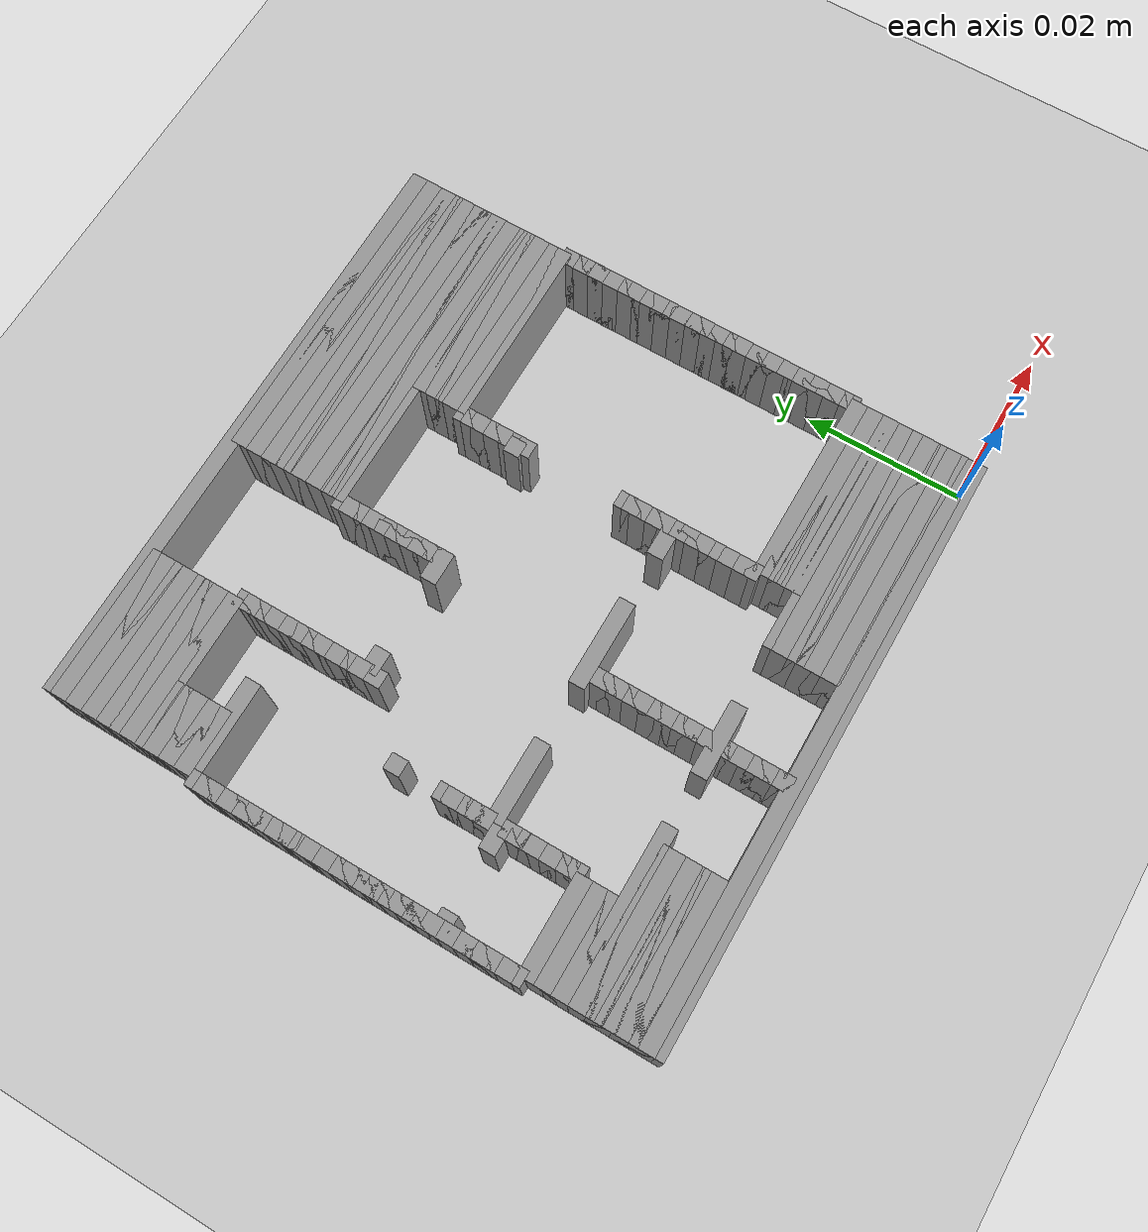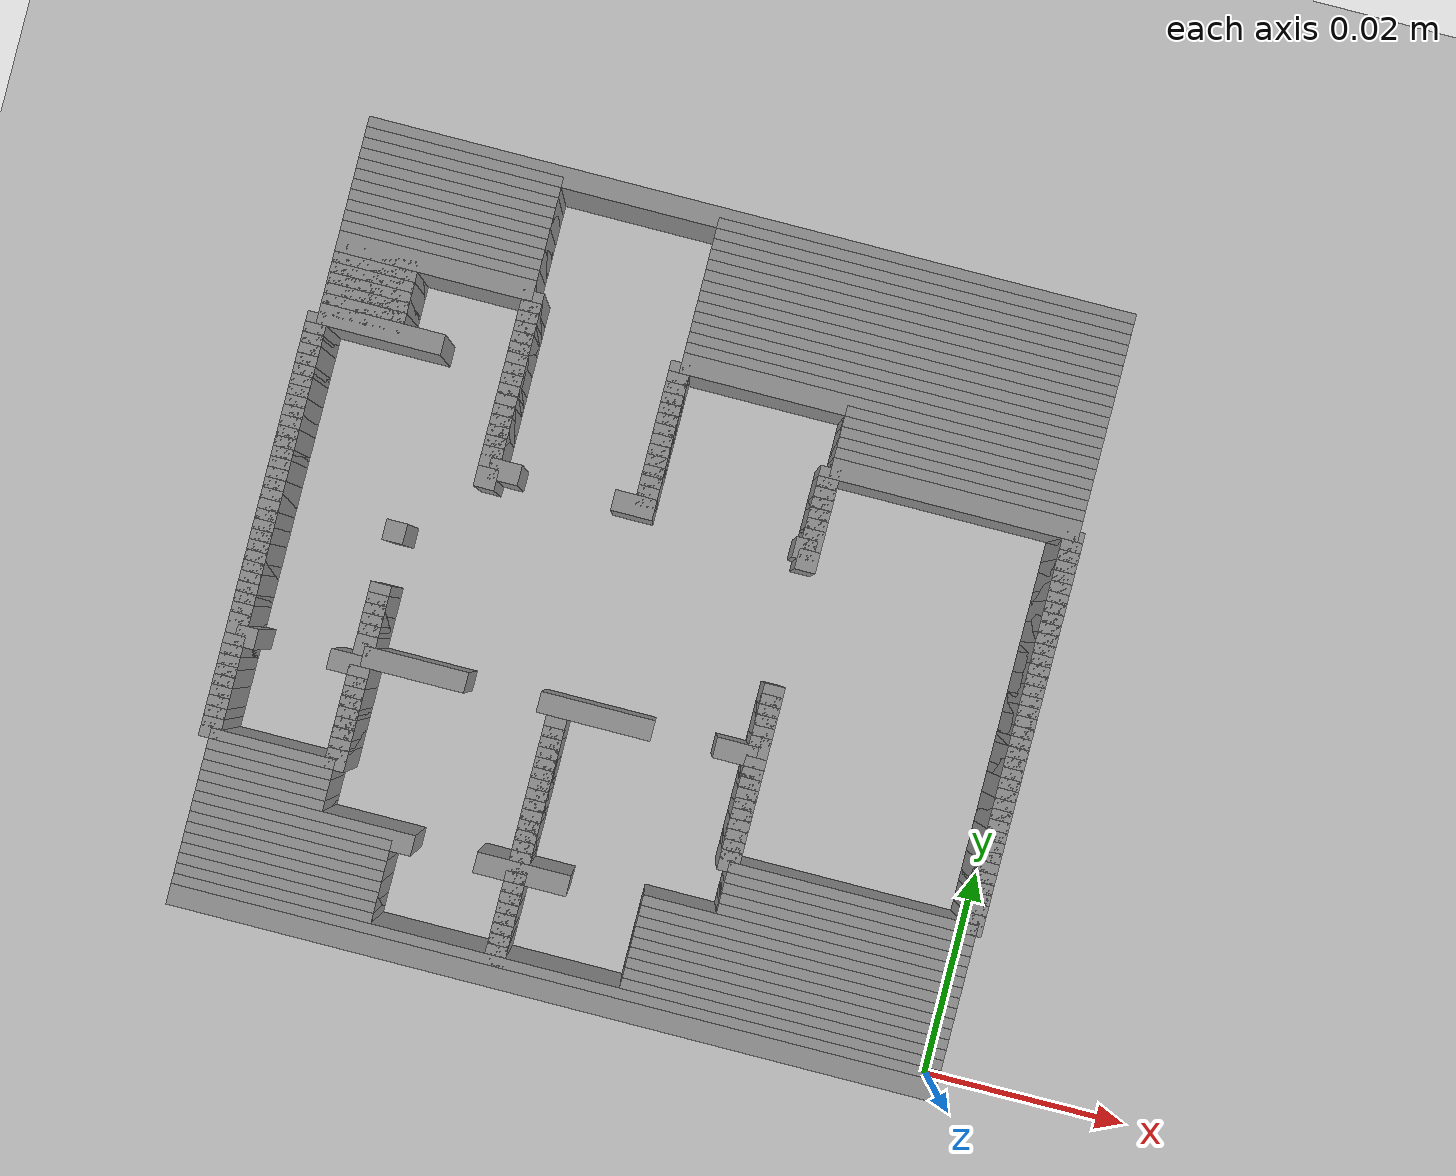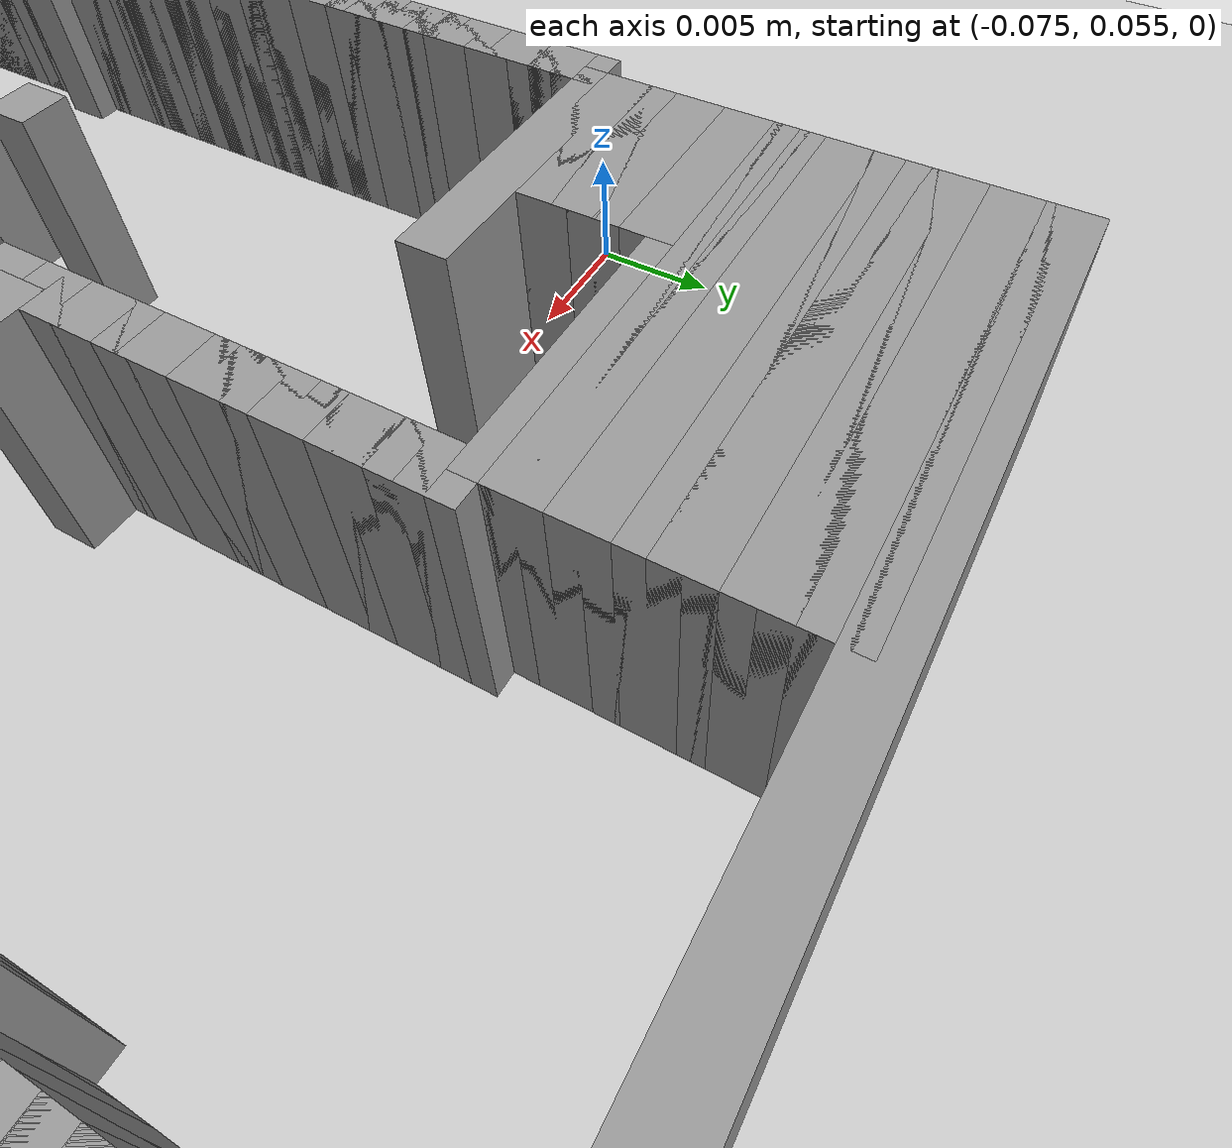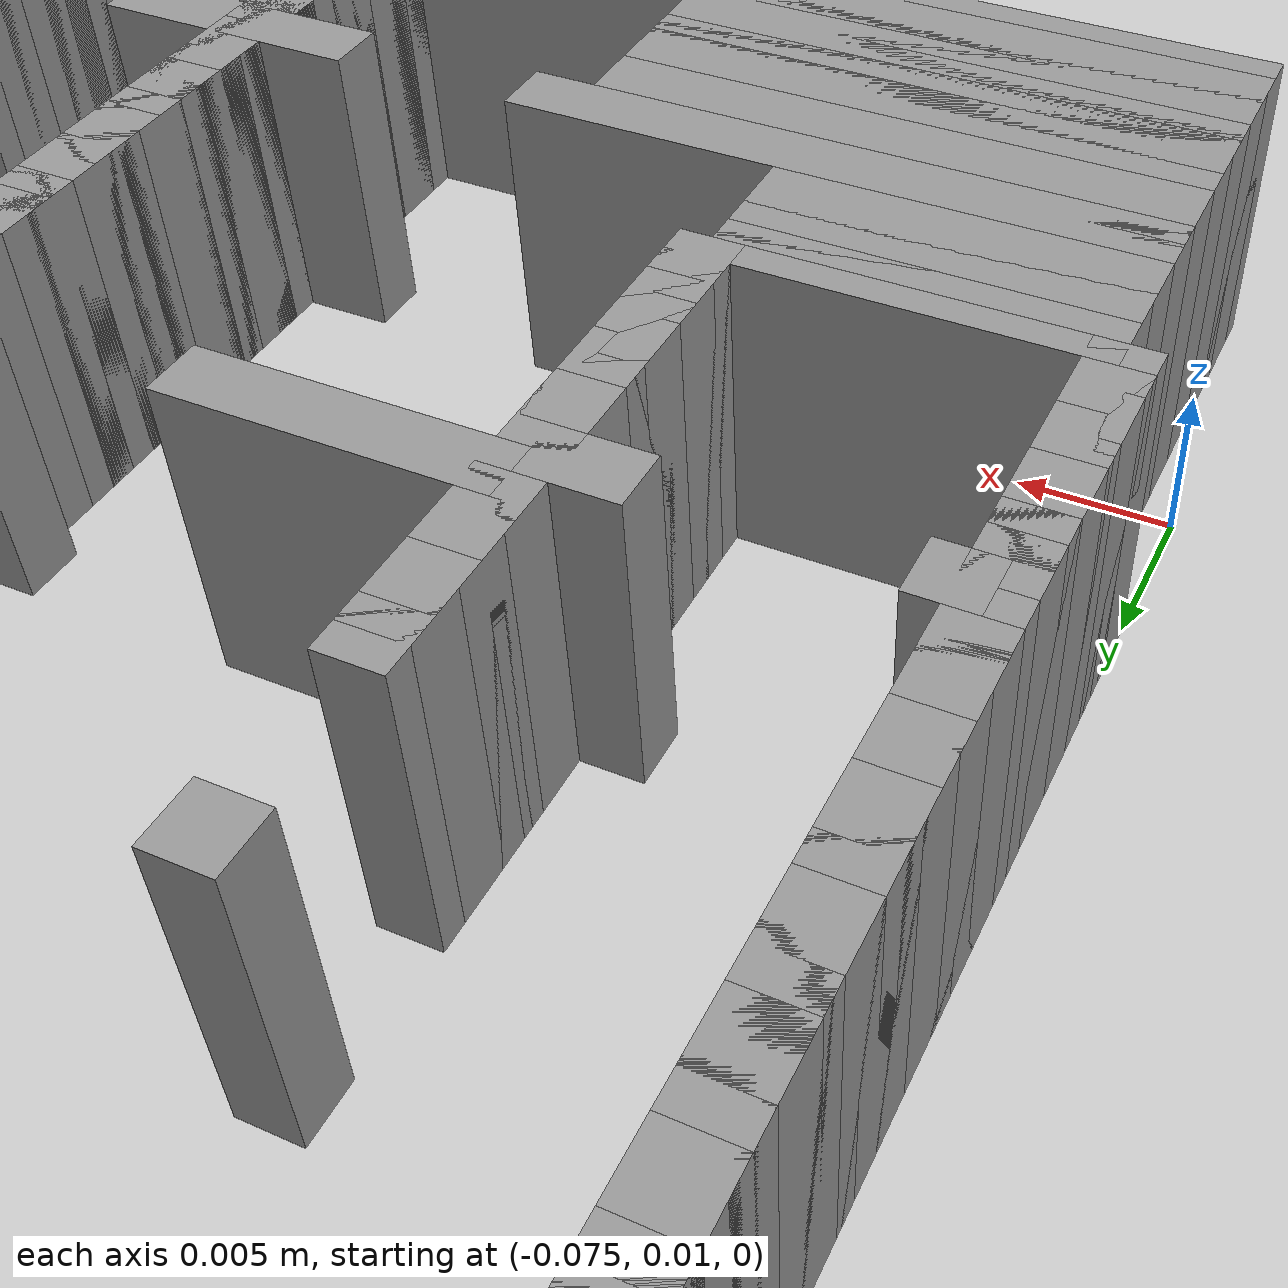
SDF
<?xml version='1.0' encoding='UTF-8'?>
<sdf version="1.6"><world name="GridMap"><include><uri>model://sun</uri></include><include><uri>model://ground_plane</uri></include><physics type="ode"><real_time_update_rate>1000.0</real_time_update_rate><max_step_size>0.001</max_step_size><real_time_factor>1</real_time_factor><ode><solver><type>quick</type><iters>150</iters><precon_iters>0</precon_iters><sor>1.4</sor><use_dynamic_moi_rescaling>1</use_dynamic_moi_rescaling></solver><constraints><cfm>0.00001</cfm><erp>0.2</erp><contact_max_correcting_vel>2000.000000</contact_max_correcting_vel><contact_surface_layer>0.01000</contact_surface_layer></constraints></ode></physics><model name="GridMap"><pose frame="">0 0 0 0 -0 0</pose><link name="Wall_(37.0,0.0)"><collision name="Wall_(37.0,0.0)_Collision"><geometry><box><size>0.074 0.002 0.01</size></box></geometry><pose frame="">-0.037 0.0 0.005 0 -0 0</pose></collision><inertial><mass>0.5</mass><pose>0 0.01 0 0 0 0</pose><inertia><ixx>0.004</ixx><ixy>0.001</ixy><ixz>0</ixz><iyy>0.006</iyy><iyz>0</iyz><izz>0.007</izz></inertia></inertial><visual name="Wall_(37.0,0.0)_Visual"><geometry><box><size>0.074 0.002 0.01</size></box></geometry><pose frame="">-0.037 0.0 0.005 0 -0 0</pose><material><script><uri>file://media/materials/scripts/gazebo.material</uri><name>Gazebo/Grey</name></script><ambient>1 1 1 1</ambient></material><meta><layer>0</layer></meta></visual><pose frame="">0 0 0 0 -0 0</pose></link><link name="Wall_(37.0,1.0)"><collision name="Wall_(37.0,1.0)_Collision"><geometry><box><size>0.074 0.002 0.01</size></box></geometry><pose frame="">-0.037 0.001 0.005 0 -0 0</pose></collision><inertial><mass>0.5</mass><pose>0 0.01 0 0 0 0</pose><inertia><ixx>0.004</ixx><ixy>0.001</ixy><ixz>0</ixz><iyy>0.006</iyy><iyz>0</iyz><izz>0.007</izz></inertia></inertial><visual name="Wall_(37.0,1.0)_Visual"><geometry><box><size>0.074 0.002 0.01</size></box></geometry><pose frame="">-0.037 0.001 0.005 0 -0 0</pose><material><script><uri>file://media/materials/scripts/gazebo.material</uri><name>Gazebo/Grey</name></script><ambient>1 1 1 1</ambient></material><meta><layer>0</layer></meta></visual><pose frame="">0 0 0 0 -0 0</pose></link><link name="Wall_(15.5,2.0)"><collision name="Wall_(15.5,2.0)_Collision"><geometry><box><size>0.031 0.002 0.01</size></box></geometry><pose frame="">-0.0155 0.002 0.005 0 -0 0</pose></collision><inertial><mass>0.5</mass><pose>0 0.01 0 0 0 0</pose><inertia><ixx>0.004</ixx><ixy>0.001</ixy><ixz>0</ixz><iyy>0.006</iyy><iyz>0</iyz><izz>0.007</izz></inertia></inertial><visual name="Wall_(15.5,2.0)_Visual"><geometry><box><size>0.031 0.002 0.01</size></box></geometry><pose frame="">-0.0155 0.002 0.005 0 -0 0</pose><material><script><uri>file://media/materials/scripts/gazebo.material</uri><name>Gazebo/Grey</name></script><ambient>1 1 1 1</ambient></material><meta><layer>0</layer></meta></visual><pose frame="">0 0 0 0 -0 0</pose></link><link name="Wall_(43.0,2.0)"><collision name="Wall_(43.0,2.0)_Collision"><geometry><box><size>0.002 0.002 0.01</size></box></geometry><pose frame="">-0.043000000000000003 0.002 0.005 0 -0 0</pose></collision><inertial><mass>0.5</mass><pose>0 0.01 0 0 0 0</pose><inertia><ixx>0.004</ixx><ixy>0.001</ixy><ixz>0</ixz><iyy>0.006</iyy><iyz>0</iyz><izz>0.007</izz></inertia></inertial><visual name="Wall_(43.0,2.0)_Visual"><geometry><box><size>0.002 0.002 0.01</size></box></geometry><pose frame="">-0.043000000000000003 0.002 0.005 0 -0 0</pose><material><script><uri>file://media/materials/scripts/gazebo.material</uri><name>Gazebo/Grey</name></script><ambient>1 1 1 1</ambient></material><meta><layer>0</layer></meta></visual><pose frame="">0 0 0 0 -0 0</pose></link><link name="Wall_(64.5,2.0)"><collision name="Wall_(64.5,2.0)_Collision"><geometry><box><size>0.019 0.002 0.01</size></box></geometry><pose frame="">-0.0645 0.002 0.005 0 -0 0</pose></collision><inertial><mass>0.5</mass><pose>0 0.01 0 0 0 0</pose><inertia><ixx>0.004</ixx><ixy>0.001</ixy><ixz>0</ixz><iyy>0.006</iyy><iyz>0</iyz><izz>0.007</izz></inertia></inertial><visual name="Wall_(64.5,2.0)_Visual"><geometry><box><size>0.019 0.002 0.01</size></box></geometry><pose frame="">-0.0645 0.002 0.005 0 -0 0</pose><material><script><uri>file://media/materials/scripts/gazebo.material</uri><name>Gazebo/Grey</name></script><ambient>1 1 1 1</ambient></material><meta><layer>0</layer></meta></visual><pose frame="">0 0 0 0 -0 0</pose></link><link name="Wall_(15.5,3.0)"><collision name="Wall_(15.5,3.0)_Collision"><geometry><box><size>0.031 0.002 0.01</size></box></geometry><pose frame="">-0.0155 0.003 0.005 0 -0 0</pose></collision><inertial><mass>0.5</mass><pose>0 0.01 0 0 0 0</pose><inertia><ixx>0.004</ixx><ixy>0.001</ixy><ixz>0</ixz><iyy>0.006</iyy><iyz>0</iyz><izz>0.007</izz></inertia></inertial><visual name="Wall_(15.5,3.0)_Visual"><geometry><box><size>0.031 0.002 0.01</size></box></geometry><pose frame="">-0.0155 0.003 0.005 0 -0 0</pose><material><script><uri>file://media/materials/scripts/gazebo.material</uri><name>Gazebo/Grey</name></script><ambient>1 1 1 1</ambient></material><meta><layer>0</layer></meta></visual><pose frame="">0 0 0 0 -0 0</pose></link><link name="Wall_(43.0,3.0)"><collision name="Wall_(43.0,3.0)_Collision"><geometry><box><size>0.002 0.002 0.01</size></box></geometry><pose frame="">-0.043000000000000003 0.003 0.005 0 -0 0</pose></collision><inertial><mass>0.5</mass><pose>0 0.01 0 0 0 0</pose><inertia><ixx>0.004</ixx><ixy>0.001</ixy><ixz>0</ixz><iyy>0.006</iyy><iyz>0</iyz><izz>0.007</izz></inertia></inertial><visual name="Wall_(43.0,3.0)_Visual"><geometry><box><size>0.002 0.002 0.01</size></box></geometry><pose frame="">-0.043000000000000003 0.003 0.005 0 -0 0</pose><material><script><uri>file://media/materials/scripts/gazebo.material</uri><name>Gazebo/Grey</name></script><ambient>1 1 1 1</ambient></material><meta><layer>0</layer></meta></visual><pose frame="">0 0 0 0 -0 0</pose></link><link name="Wall_(64.5,3.0)"><collision name="Wall_(64.5,3.0)_Collision"><geometry><box><size>0.019 0.002 0.01</size></box></geometry><pose frame="">-0.0645 0.003 0.005 0 -0 0</pose></collision><inertial><mass>0.5</mass><pose>0 0.01 0 0 0 0</pose><inertia><ixx>0.004</ixx><ixy>0.001</ixy><ixz>0</ixz><iyy>0.006</iyy><iyz>0</iyz><izz>0.007</izz></inertia></inertial><visual name="Wall_(64.5,3.0)_Visual"><geometry><box><size>0.019 0.002 0.01</size></box></geometry><pose frame="">-0.0645 0.003 0.005 0 -0 0</pose><material><script><uri>file://media/materials/scripts/gazebo.material</uri><name>Gazebo/Grey</name></script><ambient>1 1 1 1</ambient></material><meta><layer>0</layer></meta></visual><pose frame="">0 0 0 0 -0 0</pose></link><link name="Wall_(15.5,4.0)"><collision name="Wall_(15.5,4.0)_Collision"><geometry><box><size>0.031 0.002 0.01</size></box></geometry><pose frame="">-0.0155 0.004 0.005 0 -0 0</pose></collision><inertial><mass>0.5</mass><pose>0 0.01 0 0 0 0</pose><inertia><ixx>0.004</ixx><ixy>0.001</ixy><ixz>0</ixz><iyy>0.006</iyy><iyz>0</iyz><izz>0.007</izz></inertia></inertial><visual name="Wall_(15.5,4.0)_Visual"><geometry><box><size>0.031 0.002 0.01</size></box></geometry><pose frame="">-0.0155 0.004 0.005 0 -0 0</pose><material><script><uri>file://media/materials/scripts/gazebo.material</uri><name>Gazebo/Grey</name></script><ambient>1 1 1 1</ambient></material><meta><layer>0</layer></meta></visual><pose frame="">0 0 0 0 -0 0</pose></link><link name="Wall_(43.0,4.0)"><collision name="Wall_(43.0,4.0)_Collision"><geometry><box><size>0.002 0.002 0.01</size></box></geometry><pose frame="">-0.043000000000000003 0.004 0.005 0 -0 0</pose></collision><inertial><mass>0.5</mass><pose>0 0.01 0 0 0 0</pose><inertia><ixx>0.004</ixx><ixy>0.001</ixy><ixz>0</ixz><iyy>0.006</iyy><iyz>0</iyz><izz>0.007</izz></inertia></inertial><visual name="Wall_(43.0,4.0)_Visual"><geometry><box><size>0.002 0.002 0.01</size></box></geometry><pose frame="">-0.043000000000000003 0.004 0.005 0 -0 0</pose><material><script><uri>file://media/materials/scripts/gazebo.material</uri><name>Gazebo/Grey</name></script><ambient>1 1 1 1</ambient></material><meta><layer>0</layer></meta></visual><pose frame="">0 0 0 0 -0 0</pose></link><link name="Wall_(64.5,4.0)"><collision name="Wall_(64.5,4.0)_Collision"><geometry><box><size>0.019 0.002 0.01</size></box></geometry><pose frame="">-0.0645 0.004 0.005 0 -0 0</pose></collision><inertial><mass>0.5</mass><pose>0 0.01 0 0 0 0</pose><inertia><ixx>0.004</ixx><ixy>0.001</ixy><ixz>0</ixz><iyy>0.006</iyy><iyz>0</iyz><izz>0.007</izz></inertia></inertial><visual name="Wall_(64.5,4.0)_Visual"><geometry><box><size>0.019 0.002 0.01</size></box></geometry><pose frame="">-0.0645 0.004 0.005 0 -0 0</pose><material><script><uri>file://media/materials/scripts/gazebo.material</uri><name>Gazebo/Grey</name></script><ambient>1 1 1 1</ambient></material><meta><layer>0</layer></meta></visual><pose frame="">0 0 0 0 -0 0</pose></link><link name="Wall_(15.5,5.0)"><collision name="Wall_(15.5,5.0)_Collision"><geometry><box><size>0.031 0.002 0.01</size></box></geometry><pose frame="">-0.0155 0.005 0.005 0 -0 0</pose></collision><inertial><mass>0.5</mass><pose>0 0.01 0 0 0 0</pose><inertia><ixx>0.004</ixx><ixy>0.001</ixy><ixz>0</ixz><iyy>0.006</iyy><iyz>0</iyz><izz>0.007</izz></inertia></inertial><visual name="Wall_(15.5,5.0)_Visual"><geometry><box><size>0.031 0.002 0.01</size></box></geometry><pose frame="">-0.0155 0.005 0.005 0 -0 0</pose><material><script><uri>file://media/materials/scripts/gazebo.material</uri><name>Gazebo/Grey</name></script><ambient>1 1 1 1</ambient></material><meta><layer>0</layer></meta></visual><pose frame="">0 0 0 0 -0 0</pose></link><link name="Wall_(43.0,5.0)"><collision name="Wall_(43.0,5.0)_Collision"><geometry><box><size>0.002 0.002 0.01</size></box></geometry><pose frame="">-0.043000000000000003 0.005 0.005 0 -0 0</pose></collision><inertial><mass>0.5</mass><pose>0 0.01 0 0 0 0</pose><inertia><ixx>0.004</ixx><ixy>0.001</ixy><ixz>0</ixz><iyy>0.006</iyy><iyz>0</iyz><izz>0.007</izz></inertia></inertial><visual name="Wall_(43.0,5.0)_Visual"><geometry><box><size>0.002 0.002 0.01</size></box></geometry><pose frame="">-0.043000000000000003 0.005 0.005 0 -0 0</pose><material><script><uri>file://media/materials/scripts/gazebo.material</uri><name>Gazebo/Grey</name></script><ambient>1 1 1 1</ambient></material><meta><layer>0</layer></meta></visual><pose frame="">0 0 0 0 -0 0</pose></link><link name="Wall_(64.5,5.0)"><collision name="Wall_(64.5,5.0)_Collision"><geometry><box><size>0.019 0.002 0.01</size></box></geometry><pose frame="">-0.0645 0.005 0.005 0 -0 0</pose></collision><inertial><mass>0.5</mass><pose>0 0.01 0 0 0 0</pose><inertia><ixx>0.004</ixx><ixy>0.001</ixy><ixz>0</ixz><iyy>0.006</iyy><iyz>0</iyz><izz>0.007</izz></inertia></inertial><visual name="Wall_(64.5,5.0)_Visual"><geometry><box><size>0.019 0.002 0.01</size></box></geometry><pose frame="">-0.0645 0.005 0.005 0 -0 0</pose><material><script><uri>file://media/materials/scripts/gazebo.material</uri><name>Gazebo/Grey</name></script><ambient>1 1 1 1</ambient></material><meta><layer>0</layer></meta></visual><pose frame="">0 0 0 0 -0 0</pose></link><link name="Wall_(15.5,6.0)"><collision name="Wall_(15.5,6.0)_Collision"><geometry><box><size>0.031 0.002 0.01</size></box></geometry><pose frame="">-0.0155 0.006 0.005 0 -0 0</pose></collision><inertial><mass>0.5</mass><pose>0 0.01 0 0 0 0</pose><inertia><ixx>0.004</ixx><ixy>0.001</ixy><ixz>0</ixz><iyy>0.006</iyy><iyz>0</iyz><izz>0.007</izz></inertia></inertial><visual name="Wall_(15.5,6.0)_Visual"><geometry><box><size>0.031 0.002 0.01</size></box></geometry><pose frame="">-0.0155 0.006 0.005 0 -0 0</pose><material><script><uri>file://media/materials/scripts/gazebo.material</uri><name>Gazebo/Grey</name></script><ambient>1 1 1 1</ambient></material><meta><layer>0</layer></meta></visual><pose frame="">0 0 0 0 -0 0</pose></link><link name="Wall_(43.0,6.0)"><collision name="Wall_(43.0,6.0)_Collision"><geometry><box><size>0.002 0.002 0.01</size></box></geometry><pose frame="">-0.043000000000000003 0.006 0.005 0 -0 0</pose></collision><inertial><mass>0.5</mass><pose>0 0.01 0 0 0 0</pose><inertia><ixx>0.004</ixx><ixy>0.001</ixy><ixz>0</ixz><iyy>0.006</iyy><iyz>0</iyz><izz>0.007</izz></inertia></inertial><visual name="Wall_(43.0,6.0)_Visual"><geometry><box><size>0.002 0.002 0.01</size></box></geometry><pose frame="">-0.043000000000000003 0.006 0.005 0 -0 0</pose><material><script><uri>file://media/materials/scripts/gazebo.material</uri><name>Gazebo/Grey</name></script><ambient>1 1 1 1</ambient></material><meta><layer>0</layer></meta></visual><pose frame="">0 0 0 0 -0 0</pose></link><link name="Wall_(64.5,6.0)"><collision name="Wall_(64.5,6.0)_Collision"><geometry><box><size>0.019 0.002 0.01</size></box></geometry><pose frame="">-0.0645 0.006 0.005 0 -0 0</pose></collision><inertial><mass>0.5</mass><pose>0 0.01 0 0 0 0</pose><inertia><ixx>0.004</ixx><ixy>0.001</ixy><ixz>0</ixz><iyy>0.006</iyy><iyz>0</iyz><izz>0.007</izz></inertia></inertial><visual name="Wall_(64.5,6.0)_Visual"><geometry><box><size>0.019 0.002 0.01</size></box></geometry><pose frame="">-0.0645 0.006 0.005 0 -0 0</pose><material><script><uri>file://media/materials/scripts/gazebo.material</uri><name>Gazebo/Grey</name></script><ambient>1 1 1 1</ambient></material><meta><layer>0</layer></meta></visual><pose frame="">0 0 0 0 -0 0</pose></link><link name="Wall_(15.5,7.0)"><collision name="Wall_(15.5,7.0)_Collision"><geometry><box><size>0.031 0.002 0.01</size></box></geometry><pose frame="">-0.0155 0.007 0.005 0 -0 0</pose></collision><inertial><mass>0.5</mass><pose>0 0.01 0 0 0 0</pose><inertia><ixx>0.004</ixx><ixy>0.001</ixy><ixz>0</ixz><iyy>0.006</iyy><iyz>0</iyz><izz>0.007</izz></inertia></inertial><visual name="Wall_(15.5,7.0)_Visual"><geometry><box><size>0.031 0.002 0.01</size></box></geometry><pose frame="">-0.0155 0.007 0.005 0 -0 0</pose><material><script><uri>file://media/materials/scripts/gazebo.material</uri><name>Gazebo/Grey</name></script><ambient>1 1 1 1</ambient></material><meta><layer>0</layer></meta></visual><pose frame="">0 0 0 0 -0 0</pose></link><link name="Wall_(43.0,7.0)"><collision name="Wall_(43.0,7.0)_Collision"><geometry><box><size>0.002 0.002 0.01</size></box></geometry><pose frame="">-0.043000000000000003 0.007 0.005 0 -0 0</pose></collision><inertial><mass>0.5</mass><pose>0 0.01 0 0 0 0</pose><inertia><ixx>0.004</ixx><ixy>0.001</ixy><ixz>0</ixz><iyy>0.006</iyy><iyz>0</iyz><izz>0.007</izz></inertia></inertial><visual name="Wall_(43.0,7.0)_Visual"><geometry><box><size>0.002 0.002 0.01</size></box></geometry><pose frame="">-0.043000000000000003 0.007 0.005 0 -0 0</pose><material><script><uri>file://media/materials/scripts/gazebo.material</uri><name>Gazebo/Grey</name></script><ambient>1 1 1 1</ambient></material><meta><layer>0</layer></meta></visual><pose frame="">0 0 0 0 -0 0</pose></link><link name="Wall_(64.5,7.0)"><collision name="Wall_(64.5,7.0)_Collision"><geometry><box><size>0.019 0.002 0.01</size></box></geometry><pose frame="">-0.0645 0.007 0.005 0 -0 0</pose></collision><inertial><mass>0.5</mass><pose>0 0.01 0 0 0 0</pose><inertia><ixx>0.004</ixx><ixy>0.001</ixy><ixz>0</ixz><iyy>0.006</iyy><iyz>0</iyz><izz>0.007</izz></inertia></inertial><visual name="Wall_(64.5,7.0)_Visual"><geometry><box><size>0.019 0.002 0.01</size></box></geometry><pose frame="">-0.0645 0.007 0.005 0 -0 0</pose><material><script><uri>file://media/materials/scripts/gazebo.material</uri><name>Gazebo/Grey</name></script><ambient>1 1 1 1</ambient></material><meta><layer>0</layer></meta></visual><pose frame="">0 0 0 0 -0 0</pose></link><link name="Wall_(15.5,8.0)"><collision name="Wall_(15.5,8.0)_Collision"><geometry><box><size>0.031 0.002 0.01</size></box></geometry><pose frame="">-0.0155 0.008 0.005 0 -0 0</pose></collision><inertial><mass>0.5</mass><pose>0 0.01 0 0 0 0</pose><inertia><ixx>0.004</ixx><ixy>0.001</ixy><ixz>0</ixz><iyy>0.006</iyy><iyz>0</iyz><izz>0.007</izz></inertia></inertial><visual name="Wall_(15.5,8.0)_Visual"><geometry><box><size>0.031 0.002 0.01</size></box></geometry><pose frame="">-0.0155 0.008 0.005 0 -0 0</pose><material><script><uri>file://media/materials/scripts/gazebo.material</uri><name>Gazebo/Grey</name></script><ambient>1 1 1 1</ambient></material><meta><layer>0</layer></meta></visual><pose frame="">0 0 0 0 -0 0</pose></link><link name="Wall_(43.0,8.0)"><collision name="Wall_(43.0,8.0)_Collision"><geometry><box><size>0.002 0.002 0.01</size></box></geometry><pose frame="">-0.043000000000000003 0.008 0.005 0 -0 0</pose></collision><inertial><mass>0.5</mass><pose>0 0.01 0 0 0 0</pose><inertia><ixx>0.004</ixx><ixy>0.001</ixy><ixz>0</ixz><iyy>0.006</iyy><iyz>0</iyz><izz>0.007</izz></inertia></inertial><visual name="Wall_(43.0,8.0)_Visual"><geometry><box><size>0.002 0.002 0.01</size></box></geometry><pose frame="">-0.043000000000000003 0.008 0.005 0 -0 0</pose><material><script><uri>file://media/materials/scripts/gazebo.material</uri><name>Gazebo/Grey</name></script><ambient>1 1 1 1</ambient></material><meta><layer>0</layer></meta></visual><pose frame="">0 0 0 0 -0 0</pose></link><link name="Wall_(64.5,8.0)"><collision name="Wall_(64.5,8.0)_Collision"><geometry><box><size>0.019 0.002 0.01</size></box></geometry><pose frame="">-0.0645 0.008 0.005 0 -0 0</pose></collision><inertial><mass>0.5</mass><pose>0 0.01 0 0 0 0</pose><inertia><ixx>0.004</ixx><ixy>0.001</ixy><ixz>0</ixz><iyy>0.006</iyy><iyz>0</iyz><izz>0.007</izz></inertia></inertial><visual name="Wall_(64.5,8.0)_Visual"><geometry><box><size>0.019 0.002 0.01</size></box></geometry><pose frame="">-0.0645 0.008 0.005 0 -0 0</pose><material><script><uri>file://media/materials/scripts/gazebo.material</uri><name>Gazebo/Grey</name></script><ambient>1 1 1 1</ambient></material><meta><layer>0</layer></meta></visual><pose frame="">0 0 0 0 -0 0</pose></link><link name="Wall_(15.5,9.0)"><collision name="Wall_(15.5,9.0)_Collision"><geometry><box><size>0.031 0.002 0.01</size></box></geometry><pose frame="">-0.0155 0.009000000000000001 0.005 0 -0 0</pose></collision><inertial><mass>0.5</mass><pose>0 0.01 0 0 0 0</pose><inertia><ixx>0.004</ixx><ixy>0.001</ixy><ixz>0</ixz><iyy>0.006</iyy><iyz>0</iyz><izz>0.007</izz></inertia></inertial><visual name="Wall_(15.5,9.0)_Visual"><geometry><box><size>0.031 0.002 0.01</size></box></geometry><pose frame="">-0.0155 0.009000000000000001 0.005 0 -0 0</pose><material><script><uri>file://media/materials/scripts/gazebo.material</uri><name>Gazebo/Grey</name></script><ambient>1 1 1 1</ambient></material><meta><layer>0</layer></meta></visual><pose frame="">0 0 0 0 -0 0</pose></link><link name="Wall_(43.0,9.0)"><collision name="Wall_(43.0,9.0)_Collision"><geometry><box><size>0.002 0.002 0.01</size></box></geometry><pose frame="">-0.043000000000000003 0.009000000000000001 0.005 0 -0 0</pose></collision><inertial><mass>0.5</mass><pose>0 0.01 0 0 0 0</pose><inertia><ixx>0.004</ixx><ixy>0.001</ixy><ixz>0</ixz><iyy>0.006</iyy><iyz>0</iyz><izz>0.007</izz></inertia></inertial><visual name="Wall_(43.0,9.0)_Visual"><geometry><box><size>0.002 0.002 0.01</size></box></geometry><pose frame="">-0.043000000000000003 0.009000000000000001 0.005 0 -0 0</pose><material><script><uri>file://media/materials/scripts/gazebo.material</uri><name>Gazebo/Grey</name></script><ambient>1 1 1 1</ambient></material><meta><layer>0</layer></meta></visual><pose frame="">0 0 0 0 -0 0</pose></link><link name="Wall_(64.5,9.0)"><collision name="Wall_(64.5,9.0)_Collision"><geometry><box><size>0.019 0.002 0.01</size></box></geometry><pose frame="">-0.0645 0.009000000000000001 0.005 0 -0 0</pose></collision><inertial><mass>0.5</mass><pose>0 0.01 0 0 0 0</pose><inertia><ixx>0.004</ixx><ixy>0.001</ixy><ixz>0</ixz><iyy>0.006</iyy><iyz>0</iyz><izz>0.007</izz></inertia></inertial><visual name="Wall_(64.5,9.0)_Visual"><geometry><box><size>0.019 0.002 0.01</size></box></geometry><pose frame="">-0.0645 0.009000000000000001 0.005 0 -0 0</pose><material><script><uri>file://media/materials/scripts/gazebo.material</uri><name>Gazebo/Grey</name></script><ambient>1 1 1 1</ambient></material><meta><layer>0</layer></meta></visual><pose frame="">0 0 0 0 -0 0</pose></link><link name="Wall_(15.5,10.0)"><collision name="Wall_(15.5,10.0)_Collision"><geometry><box><size>0.031 0.002 0.01</size></box></geometry><pose frame="">-0.0155 0.01 0.005 0 -0 0</pose></collision><inertial><mass>0.5</mass><pose>0 0.01 0 0 0 0</pose><inertia><ixx>0.004</ixx><ixy>0.001</ixy><ixz>0</ixz><iyy>0.006</iyy><iyz>0</iyz><izz>0.007</izz></inertia></inertial><visual name="Wall_(15.5,10.0)_Visual"><geometry><box><size>0.031 0.002 0.01</size></box></geometry><pose frame="">-0.0155 0.01 0.005 0 -0 0</pose><material><script><uri>file://media/materials/scripts/gazebo.material</uri><name>Gazebo/Grey</name></script><ambient>1 1 1 1</ambient></material><meta><layer>0</layer></meta></visual><pose frame="">0 0 0 0 -0 0</pose></link><link name="Wall_(42.5,10.0)"><collision name="Wall_(42.5,10.0)_Collision"><geometry><box><size>0.009000000000000001 0.002 0.01</size></box></geometry><pose frame="">-0.0425 0.01 0.005 0 -0 0</pose></collision><inertial><mass>0.5</mass><pose>0 0.01 0 0 0 0</pose><inertia><ixx>0.004</ixx><ixy>0.001</ixy><ixz>0</ixz><iyy>0.006</iyy><iyz>0</iyz><izz>0.007</izz></inertia></inertial><visual name="Wall_(42.5,10.0)_Visual"><geometry><box><size>0.009000000000000001 0.002 0.01</size></box></geometry><pose frame="">-0.0425 0.01 0.005 0 -0 0</pose><material><script><uri>file://media/materials/scripts/gazebo.material</uri><name>Gazebo/Grey</name></script><ambient>1 1 1 1</ambient></material><meta><layer>0</layer></meta></visual><pose frame="">0 0 0 0 -0 0</pose></link><link name="Wall_(63.5,10.0)"><collision name="Wall_(63.5,10.0)_Collision"><geometry><box><size>0.021 0.002 0.01</size></box></geometry><pose frame="">-0.0635 0.01 0.005 0 -0 0</pose></collision><inertial><mass>0.5</mass><pose>0 0.01 0 0 0 0</pose><inertia><ixx>0.004</ixx><ixy>0.001</ixy><ixz>0</ixz><iyy>0.006</iyy><iyz>0</iyz><izz>0.007</izz></inertia></inertial><visual name="Wall_(63.5,10.0)_Visual"><geometry><box><size>0.021 0.002 0.01</size></box></geometry><pose frame="">-0.0635 0.01 0.005 0 -0 0</pose><material><script><uri>file://media/materials/scripts/gazebo.material</uri><name>Gazebo/Grey</name></script><ambient>1 1 1 1</ambient></material><meta><layer>0</layer></meta></visual><pose frame="">0 0 0 0 -0 0</pose></link><link name="Wall_(12.0,11.0)"><collision name="Wall_(12.0,11.0)_Collision"><geometry><box><size>0.024 0.002 0.01</size></box></geometry><pose frame="">-0.012 0.011 0.005 0 -0 0</pose></collision><inertial><mass>0.5</mass><pose>0 0.01 0 0 0 0</pose><inertia><ixx>0.004</ixx><ixy>0.001</ixy><ixz>0</ixz><iyy>0.006</iyy><iyz>0</iyz><izz>0.007</izz></inertia></inertial><visual name="Wall_(12.0,11.0)_Visual"><geometry><box><size>0.024 0.002 0.01</size></box></geometry><pose frame="">-0.012 0.011 0.005 0 -0 0</pose><material><script><uri>file://media/materials/scripts/gazebo.material</uri><name>Gazebo/Grey</name></script><ambient>1 1 1 1</ambient></material><meta><layer>0</layer></meta></visual><pose frame="">0 0 0 0 -0 0</pose></link><link name="Wall_(43.0,11.0)"><collision name="Wall_(43.0,11.0)_Collision"><geometry><box><size>0.002 0.002 0.01</size></box></geometry><pose frame="">-0.043000000000000003 0.011 0.005 0 -0 0</pose></collision><inertial><mass>0.5</mass><pose>0 0.01 0 0 0 0</pose><inertia><ixx>0.004</ixx><ixy>0.001</ixy><ixz>0</ixz><iyy>0.006</iyy><iyz>0</iyz><izz>0.007</izz></inertia></inertial><visual name="Wall_(43.0,11.0)_Visual"><geometry><box><size>0.002 0.002 0.01</size></box></geometry><pose frame="">-0.043000000000000003 0.011 0.005 0 -0 0</pose><material><script><uri>file://media/materials/scripts/gazebo.material</uri><name>Gazebo/Grey</name></script><ambient>1 1 1 1</ambient></material><meta><layer>0</layer></meta></visual><pose frame="">0 0 0 0 -0 0</pose></link><link name="Wall_(68.0,11.0)"><collision name="Wall_(68.0,11.0)_Collision"><geometry><box><size>0.012 0.002 0.01</size></box></geometry><pose frame="">-0.068 0.011 0.005 0 -0 0</pose></collision><inertial><mass>0.5</mass><pose>0 0.01 0 0 0 0</pose><inertia><ixx>0.004</ixx><ixy>0.001</ixy><ixz>0</ixz><iyy>0.006</iyy><iyz>0</iyz><izz>0.007</izz></inertia></inertial><visual name="Wall_(68.0,11.0)_Visual"><geometry><box><size>0.012 0.002 0.01</size></box></geometry><pose frame="">-0.068 0.011 0.005 0 -0 0</pose><material><script><uri>file://media/materials/scripts/gazebo.material</uri><name>Gazebo/Grey</name></script><ambient>1 1 1 1</ambient></material><meta><layer>0</layer></meta></visual><pose frame="">0 0 0 0 -0 0</pose></link><link name="Wall_(12.0,12.0)"><collision name="Wall_(12.0,12.0)_Collision"><geometry><box><size>0.024 0.002 0.01</size></box></geometry><pose frame="">-0.012 0.012 0.005 0 -0 0</pose></collision><inertial><mass>0.5</mass><pose>0 0.01 0 0 0 0</pose><inertia><ixx>0.004</ixx><ixy>0.001</ixy><ixz>0</ixz><iyy>0.006</iyy><iyz>0</iyz><izz>0.007</izz></inertia></inertial><visual name="Wall_(12.0,12.0)_Visual"><geometry><box><size>0.024 0.002 0.01</size></box></geometry><pose frame="">-0.012 0.012 0.005 0 -0 0</pose><material><script><uri>file://media/materials/scripts/gazebo.material</uri><name>Gazebo/Grey</name></script><ambient>1 1 1 1</ambient></material><meta><layer>0</layer></meta></visual><pose frame="">0 0 0 0 -0 0</pose></link><link name="Wall_(43.0,12.0)"><collision name="Wall_(43.0,12.0)_Collision"><geometry><box><size>0.002 0.002 0.01</size></box></geometry><pose frame="">-0.043000000000000003 0.012 0.005 0 -0 0</pose></collision><inertial><mass>0.5</mass><pose>0 0.01 0 0 0 0</pose><inertia><ixx>0.004</ixx><ixy>0.001</ixy><ixz>0</ixz><iyy>0.006</iyy><iyz>0</iyz><izz>0.007</izz></inertia></inertial><visual name="Wall_(43.0,12.0)_Visual"><geometry><box><size>0.002 0.002 0.01</size></box></geometry><pose frame="">-0.043000000000000003 0.012 0.005 0 -0 0</pose><material><script><uri>file://media/materials/scripts/gazebo.material</uri><name>Gazebo/Grey</name></script><ambient>1 1 1 1</ambient></material><meta><layer>0</layer></meta></visual><pose frame="">0 0 0 0 -0 0</pose></link><link name="Wall_(68.0,12.0)"><collision name="Wall_(68.0,12.0)_Collision"><geometry><box><size>0.012 0.002 0.01</size></box></geometry><pose frame="">-0.068 0.012 0.005 0 -0 0</pose></collision><inertial><mass>0.5</mass><pose>0 0.01 0 0 0 0</pose><inertia><ixx>0.004</ixx><ixy>0.001</ixy><ixz>0</ixz><iyy>0.006</iyy><iyz>0</iyz><izz>0.007</izz></inertia></inertial><visual name="Wall_(68.0,12.0)_Visual"><geometry><box><size>0.012 0.002 0.01</size></box></geometry><pose frame="">-0.068 0.012 0.005 0 -0 0</pose><material><script><uri>file://media/materials/scripts/gazebo.material</uri><name>Gazebo/Grey</name></script><ambient>1 1 1 1</ambient></material><meta><layer>0</layer></meta></visual><pose frame="">0 0 0 0 -0 0</pose></link><link name="Wall_(12.0,13.0)"><collision name="Wall_(12.0,13.0)_Collision"><geometry><box><size>0.024 0.002 0.01</size></box></geometry><pose frame="">-0.012 0.013000000000000001 0.005 0 -0 0</pose></collision><inertial><mass>0.5</mass><pose>0 0.01 0 0 0 0</pose><inertia><ixx>0.004</ixx><ixy>0.001</ixy><ixz>0</ixz><iyy>0.006</iyy><iyz>0</iyz><izz>0.007</izz></inertia></inertial><visual name="Wall_(12.0,13.0)_Visual"><geometry><box><size>0.024 0.002 0.01</size></box></geometry><pose frame="">-0.012 0.013000000000000001 0.005 0 -0 0</pose><material><script><uri>file://media/materials/scripts/gazebo.material</uri><name>Gazebo/Grey</name></script><ambient>1 1 1 1</ambient></material><meta><layer>0</layer></meta></visual><pose frame="">0 0 0 0 -0 0</pose></link><link name="Wall_(43.0,13.0)"><collision name="Wall_(43.0,13.0)_Collision"><geometry><box><size>0.002 0.002 0.01</size></box></geometry><pose frame="">-0.043000000000000003 0.013000000000000001 0.005 0 -0 0</pose></collision><inertial><mass>0.5</mass><pose>0 0.01 0 0 0 0</pose><inertia><ixx>0.004</ixx><ixy>0.001</ixy><ixz>0</ixz><iyy>0.006</iyy><iyz>0</iyz><izz>0.007</izz></inertia></inertial><visual name="Wall_(43.0,13.0)_Visual"><geometry><box><size>0.002 0.002 0.01</size></box></geometry><pose frame="">-0.043000000000000003 0.013000000000000001 0.005 0 -0 0</pose><material><script><uri>file://media/materials/scripts/gazebo.material</uri><name>Gazebo/Grey</name></script><ambient>1 1 1 1</ambient></material><meta><layer>0</layer></meta></visual><pose frame="">0 0 0 0 -0 0</pose></link><link name="Wall_(68.0,13.0)"><collision name="Wall_(68.0,13.0)_Collision"><geometry><box><size>0.012 0.002 0.01</size></box></geometry><pose frame="">-0.068 0.013000000000000001 0.005 0 -0 0</pose></collision><inertial><mass>0.5</mass><pose>0 0.01 0 0 0 0</pose><inertia><ixx>0.004</ixx><ixy>0.001</ixy><ixz>0</ixz><iyy>0.006</iyy><iyz>0</iyz><izz>0.007</izz></inertia></inertial><visual name="Wall_(68.0,13.0)_Visual"><geometry><box><size>0.012 0.002 0.01</size></box></geometry><pose frame="">-0.068 0.013000000000000001 0.005 0 -0 0</pose><material><script><uri>file://media/materials/scripts/gazebo.material</uri><name>Gazebo/Grey</name></script><ambient>1 1 1 1</ambient></material><meta><layer>0</layer></meta></visual><pose frame="">0 0 0 0 -0 0</pose></link><link name="Wall_(12.0,14.0)"><collision name="Wall_(12.0,14.0)_Collision"><geometry><box><size>0.024 0.002 0.01</size></box></geometry><pose frame="">-0.012 0.014 0.005 0 -0 0</pose></collision><inertial><mass>0.5</mass><pose>0 0.01 0 0 0 0</pose><inertia><ixx>0.004</ixx><ixy>0.001</ixy><ixz>0</ixz><iyy>0.006</iyy><iyz>0</iyz><izz>0.007</izz></inertia></inertial><visual name="Wall_(12.0,14.0)_Visual"><geometry><box><size>0.024 0.002 0.01</size></box></geometry><pose frame="">-0.012 0.014 0.005 0 -0 0</pose><material><script><uri>file://media/materials/scripts/gazebo.material</uri><name>Gazebo/Grey</name></script><ambient>1 1 1 1</ambient></material><meta><layer>0</layer></meta></visual><pose frame="">0 0 0 0 -0 0</pose></link><link name="Wall_(43.0,14.0)"><collision name="Wall_(43.0,14.0)_Collision"><geometry><box><size>0.002 0.002 0.01</size></box></geometry><pose frame="">-0.043000000000000003 0.014 0.005 0 -0 0</pose></collision><inertial><mass>0.5</mass><pose>0 0.01 0 0 0 0</pose><inertia><ixx>0.004</ixx><ixy>0.001</ixy><ixz>0</ixz><iyy>0.006</iyy><iyz>0</iyz><izz>0.007</izz></inertia></inertial><visual name="Wall_(43.0,14.0)_Visual"><geometry><box><size>0.002 0.002 0.01</size></box></geometry><pose frame="">-0.043000000000000003 0.014 0.005 0 -0 0</pose><material><script><uri>file://media/materials/scripts/gazebo.material</uri><name>Gazebo/Grey</name></script><ambient>1 1 1 1</ambient></material><meta><layer>0</layer></meta></visual><pose frame="">0 0 0 0 -0 0</pose></link><link name="Wall_(68.0,14.0)"><collision name="Wall_(68.0,14.0)_Collision"><geometry><box><size>0.012 0.002 0.01</size></box></geometry><pose frame="">-0.068 0.014 0.005 0 -0 0</pose></collision><inertial><mass>0.5</mass><pose>0 0.01 0 0 0 0</pose><inertia><ixx>0.004</ixx><ixy>0.001</ixy><ixz>0</ixz><iyy>0.006</iyy><iyz>0</iyz><izz>0.007</izz></inertia></inertial><visual name="Wall_(68.0,14.0)_Visual"><geometry><box><size>0.012 0.002 0.01</size></box></geometry><pose frame="">-0.068 0.014 0.005 0 -0 0</pose><material><script><uri>file://media/materials/scripts/gazebo.material</uri><name>Gazebo/Grey</name></script><ambient>1 1 1 1</ambient></material><meta><layer>0</layer></meta></visual><pose frame="">0 0 0 0 -0 0</pose></link><link name="Wall_(12.0,15.0)"><collision name="Wall_(12.0,15.0)_Collision"><geometry><box><size>0.024 0.002 0.01</size></box></geometry><pose frame="">-0.012 0.015 0.005 0 -0 0</pose></collision><inertial><mass>0.5</mass><pose>0 0.01 0 0 0 0</pose><inertia><ixx>0.004</ixx><ixy>0.001</ixy><ixz>0</ixz><iyy>0.006</iyy><iyz>0</iyz><izz>0.007</izz></inertia></inertial><visual name="Wall_(12.0,15.0)_Visual"><geometry><box><size>0.024 0.002 0.01</size></box></geometry><pose frame="">-0.012 0.015 0.005 0 -0 0</pose><material><script><uri>file://media/materials/scripts/gazebo.material</uri><name>Gazebo/Grey</name></script><ambient>1 1 1 1</ambient></material><meta><layer>0</layer></meta></visual><pose frame="">0 0 0 0 -0 0</pose></link><link name="Wall_(43.0,15.0)"><collision name="Wall_(43.0,15.0)_Collision"><geometry><box><size>0.002 0.002 0.01</size></box></geometry><pose frame="">-0.043000000000000003 0.015 0.005 0 -0 0</pose></collision><inertial><mass>0.5</mass><pose>0 0.01 0 0 0 0</pose><inertia><ixx>0.004</ixx><ixy>0.001</ixy><ixz>0</ixz><iyy>0.006</iyy><iyz>0</iyz><izz>0.007</izz></inertia></inertial><visual name="Wall_(43.0,15.0)_Visual"><geometry><box><size>0.002 0.002 0.01</size></box></geometry><pose frame="">-0.043000000000000003 0.015 0.005 0 -0 0</pose><material><script><uri>file://media/materials/scripts/gazebo.material</uri><name>Gazebo/Grey</name></script><ambient>1 1 1 1</ambient></material><meta><layer>0</layer></meta></visual><pose frame="">0 0 0 0 -0 0</pose></link><link name="Wall_(68.0,15.0)"><collision name="Wall_(68.0,15.0)_Collision"><geometry><box><size>0.012 0.002 0.01</size></box></geometry><pose frame="">-0.068 0.015 0.005 0 -0 0</pose></collision><inertial><mass>0.5</mass><pose>0 0.01 0 0 0 0</pose><inertia><ixx>0.004</ixx><ixy>0.001</ixy><ixz>0</ixz><iyy>0.006</iyy><iyz>0</iyz><izz>0.007</izz></inertia></inertial><visual name="Wall_(68.0,15.0)_Visual"><geometry><box><size>0.012 0.002 0.01</size></box></geometry><pose frame="">-0.068 0.015 0.005 0 -0 0</pose><material><script><uri>file://media/materials/scripts/gazebo.material</uri><name>Gazebo/Grey</name></script><ambient>1 1 1 1</ambient></material><meta><layer>0</layer></meta></visual><pose frame="">0 0 0 0 -0 0</pose></link><link name="Wall_(0.5,16.0)"><collision name="Wall_(0.5,16.0)_Collision"><geometry><box><size>0.002 0.002 0.01</size></box></geometry><pose frame="">-0.0005 0.016 0.005 0 -0 0</pose></collision><inertial><mass>0.5</mass><pose>0 0.01 0 0 0 0</pose><inertia><ixx>0.004</ixx><ixy>0.001</ixy><ixz>0</ixz><iyy>0.006</iyy><iyz>0</iyz><izz>0.007</izz></inertia></inertial><visual name="Wall_(0.5,16.0)_Visual"><geometry><box><size>0.002 0.002 0.01</size></box></geometry><pose frame="">-0.0005 0.016 0.005 0 -0 0</pose><material><script><uri>file://media/materials/scripts/gazebo.material</uri><name>Gazebo/Grey</name></script><ambient>1 1 1 1</ambient></material><meta><layer>0</layer></meta></visual><pose frame="">0 0 0 0 -0 0</pose></link><link name="Wall_(24.0,16.0)"><collision name="Wall_(24.0,16.0)_Collision"><geometry><box><size>0.002 0.002 0.01</size></box></geometry><pose frame="">-0.024 0.016 0.005 0 -0 0</pose></collision><inertial><mass>0.5</mass><pose>0 0.01 0 0 0 0</pose><inertia><ixx>0.004</ixx><ixy>0.001</ixy><ixz>0</ixz><iyy>0.006</iyy><iyz>0</iyz><izz>0.007</izz></inertia></inertial><visual name="Wall_(24.0,16.0)_Visual"><geometry><box><size>0.002 0.002 0.01</size></box></geometry><pose frame="">-0.024 0.016 0.005 0 -0 0</pose><material><script><uri>file://media/materials/scripts/gazebo.material</uri><name>Gazebo/Grey</name></script><ambient>1 1 1 1</ambient></material><meta><layer>0</layer></meta></visual><pose frame="">0 0 0 0 -0 0</pose></link><link name="Wall_(43.0,16.0)"><collision name="Wall_(43.0,16.0)_Collision"><geometry><box><size>0.002 0.002 0.01</size></box></geometry><pose frame="">-0.043000000000000003 0.016 0.005 0 -0 0</pose></collision><inertial><mass>0.5</mass><pose>0 0.01 0 0 0 0</pose><inertia><ixx>0.004</ixx><ixy>0.001</ixy><ixz>0</ixz><iyy>0.006</iyy><iyz>0</iyz><izz>0.007</izz></inertia></inertial><visual name="Wall_(43.0,16.0)_Visual"><geometry><box><size>0.002 0.002 0.01</size></box></geometry><pose frame="">-0.043000000000000003 0.016 0.005 0 -0 0</pose><material><script><uri>file://media/materials/scripts/gazebo.material</uri><name>Gazebo/Grey</name></script><ambient>1 1 1 1</ambient></material><meta><layer>0</layer></meta></visual><pose frame="">0 0 0 0 -0 0</pose></link><link name="Wall_(62.0,16.0)"><collision name="Wall_(62.0,16.0)_Collision"><geometry><box><size>0.002 0.002 0.01</size></box></geometry><pose frame="">-0.062 0.016 0.005 0 -0 0</pose></collision><inertial><mass>0.5</mass><pose>0 0.01 0 0 0 0</pose><inertia><ixx>0.004</ixx><ixy>0.001</ixy><ixz>0</ixz><iyy>0.006</iyy><iyz>0</iyz><izz>0.007</izz></inertia></inertial><visual name="Wall_(62.0,16.0)_Visual"><geometry><box><size>0.002 0.002 0.01</size></box></geometry><pose frame="">-0.062 0.016 0.005 0 -0 0</pose><material><script><uri>file://media/materials/scripts/gazebo.material</uri><name>Gazebo/Grey</name></script><ambient>1 1 1 1</ambient></material><meta><layer>0</layer></meta></visual><pose frame="">0 0 0 0 -0 0</pose></link><link name="Wall_(74.0,16.0)"><collision name="Wall_(74.0,16.0)_Collision"><geometry><box><size>0.002 0.002 0.01</size></box></geometry><pose frame="">-0.074 0.016 0.005 0 -0 0</pose></collision><inertial><mass>0.5</mass><pose>0 0.01 0 0 0 0</pose><inertia><ixx>0.004</ixx><ixy>0.001</ixy><ixz>0</ixz><iyy>0.006</iyy><iyz>0</iyz><izz>0.007</izz></inertia></inertial><visual name="Wall_(74.0,16.0)_Visual"><geometry><box><size>0.002 0.002 0.01</size></box></geometry><pose frame="">-0.074 0.016 0.005 0 -0 0</pose><material><script><uri>file://media/materials/scripts/gazebo.material</uri><name>Gazebo/Grey</name></script><ambient>1 1 1 1</ambient></material><meta><layer>0</layer></meta></visual><pose frame="">0 0 0 0 -0 0</pose></link><link name="Wall_(0.5,17.0)"><collision name="Wall_(0.5,17.0)_Collision"><geometry><box><size>0.002 0.002 0.01</size></box></geometry><pose frame="">-0.0005 0.017 0.005 0 -0 0</pose></collision><inertial><mass>0.5</mass><pose>0 0.01 0 0 0 0</pose><inertia><ixx>0.004</ixx><ixy>0.001</ixy><ixz>0</ixz><iyy>0.006</iyy><iyz>0</iyz><izz>0.007</izz></inertia></inertial><visual name="Wall_(0.5,17.0)_Visual"><geometry><box><size>0.002 0.002 0.01</size></box></geometry><pose frame="">-0.0005 0.017 0.005 0 -0 0</pose><material><script><uri>file://media/materials/scripts/gazebo.material</uri><name>Gazebo/Grey</name></script><ambient>1 1 1 1</ambient></material><meta><layer>0</layer></meta></visual><pose frame="">0 0 0 0 -0 0</pose></link><link name="Wall_(24.0,17.0)"><collision name="Wall_(24.0,17.0)_Collision"><geometry><box><size>0.002 0.002 0.01</size></box></geometry><pose frame="">-0.024 0.017 0.005 0 -0 0</pose></collision><inertial><mass>0.5</mass><pose>0 0.01 0 0 0 0</pose><inertia><ixx>0.004</ixx><ixy>0.001</ixy><ixz>0</ixz><iyy>0.006</iyy><iyz>0</iyz><izz>0.007</izz></inertia></inertial><visual name="Wall_(24.0,17.0)_Visual"><geometry><box><size>0.002 0.002 0.01</size></box></geometry><pose frame="">-0.024 0.017 0.005 0 -0 0</pose><material><script><uri>file://media/materials/scripts/gazebo.material</uri><name>Gazebo/Grey</name></script><ambient>1 1 1 1</ambient></material><meta><layer>0</layer></meta></visual><pose frame="">0 0 0 0 -0 0</pose></link><link name="Wall_(43.0,17.0)"><collision name="Wall_(43.0,17.0)_Collision"><geometry><box><size>0.002 0.002 0.01</size></box></geometry><pose frame="">-0.043000000000000003 0.017 0.005 0 -0 0</pose></collision><inertial><mass>0.5</mass><pose>0 0.01 0 0 0 0</pose><inertia><ixx>0.004</ixx><ixy>0.001</ixy><ixz>0</ixz><iyy>0.006</iyy><iyz>0</iyz><izz>0.007</izz></inertia></inertial><visual name="Wall_(43.0,17.0)_Visual"><geometry><box><size>0.002 0.002 0.01</size></box></geometry><pose frame="">-0.043000000000000003 0.017 0.005 0 -0 0</pose><material><script><uri>file://media/materials/scripts/gazebo.material</uri><name>Gazebo/Grey</name></script><ambient>1 1 1 1</ambient></material><meta><layer>0</layer></meta></visual><pose frame="">0 0 0 0 -0 0</pose></link><link name="Wall_(62.0,17.0)"><collision name="Wall_(62.0,17.0)_Collision"><geometry><box><size>0.002 0.002 0.01</size></box></geometry><pose frame="">-0.062 0.017 0.005 0 -0 0</pose></collision><inertial><mass>0.5</mass><pose>0 0.01 0 0 0 0</pose><inertia><ixx>0.004</ixx><ixy>0.001</ixy><ixz>0</ixz><iyy>0.006</iyy><iyz>0</iyz><izz>0.007</izz></inertia></inertial><visual name="Wall_(62.0,17.0)_Visual"><geometry><box><size>0.002 0.002 0.01</size></box></geometry><pose frame="">-0.062 0.017 0.005 0 -0 0</pose><material><script><uri>file://media/materials/scripts/gazebo.material</uri><name>Gazebo/Grey</name></script><ambient>1 1 1 1</ambient></material><meta><layer>0</layer></meta></visual><pose frame="">0 0 0 0 -0 0</pose></link><link name="Wall_(74.0,17.0)"><collision name="Wall_(74.0,17.0)_Collision"><geometry><box><size>0.002 0.002 0.01</size></box></geometry><pose frame="">-0.074 0.017 0.005 0 -0 0</pose></collision><inertial><mass>0.5</mass><pose>0 0.01 0 0 0 0</pose><inertia><ixx>0.004</ixx><ixy>0.001</ixy><ixz>0</ixz><iyy>0.006</iyy><iyz>0</iyz><izz>0.007</izz></inertia></inertial><visual name="Wall_(74.0,17.0)_Visual"><geometry><box><size>0.002 0.002 0.01</size></box></geometry><pose frame="">-0.074 0.017 0.005 0 -0 0</pose><material><script><uri>file://media/materials/scripts/gazebo.material</uri><name>Gazebo/Grey</name></script><ambient>1 1 1 1</ambient></material><meta><layer>0</layer></meta></visual><pose frame="">0 0 0 0 -0 0</pose></link><link name="Wall_(0.5,18.0)"><collision name="Wall_(0.5,18.0)_Collision"><geometry><box><size>0.002 0.002 0.01</size></box></geometry><pose frame="">-0.0005 0.018000000000000002 0.005 0 -0 0</pose></collision><inertial><mass>0.5</mass><pose>0 0.01 0 0 0 0</pose><inertia><ixx>0.004</ixx><ixy>0.001</ixy><ixz>0</ixz><iyy>0.006</iyy><iyz>0</iyz><izz>0.007</izz></inertia></inertial><visual name="Wall_(0.5,18.0)_Visual"><geometry><box><size>0.002 0.002 0.01</size></box></geometry><pose frame="">-0.0005 0.018000000000000002 0.005 0 -0 0</pose><material><script><uri>file://media/materials/scripts/gazebo.material</uri><name>Gazebo/Grey</name></script><ambient>1 1 1 1</ambient></material><meta><layer>0</layer></meta></visual><pose frame="">0 0 0 0 -0 0</pose></link><link name="Wall_(24.0,18.0)"><collision name="Wall_(24.0,18.0)_Collision"><geometry><box><size>0.002 0.002 0.01</size></box></geometry><pose frame="">-0.024 0.018000000000000002 0.005 0 -0 0</pose></collision><inertial><mass>0.5</mass><pose>0 0.01 0 0 0 0</pose><inertia><ixx>0.004</ixx><ixy>0.001</ixy><ixz>0</ixz><iyy>0.006</iyy><iyz>0</iyz><izz>0.007</izz></inertia></inertial><visual name="Wall_(24.0,18.0)_Visual"><geometry><box><size>0.002 0.002 0.01</size></box></geometry><pose frame="">-0.024 0.018000000000000002 0.005 0 -0 0</pose><material><script><uri>file://media/materials/scripts/gazebo.material</uri><name>Gazebo/Grey</name></script><ambient>1 1 1 1</ambient></material><meta><layer>0</layer></meta></visual><pose frame="">0 0 0 0 -0 0</pose></link><link name="Wall_(43.0,18.0)"><collision name="Wall_(43.0,18.0)_Collision"><geometry><box><size>0.002 0.002 0.01</size></box></geometry><pose frame="">-0.043000000000000003 0.018000000000000002 0.005 0 -0 0</pose></collision><inertial><mass>0.5</mass><pose>0 0.01 0 0 0 0</pose><inertia><ixx>0.004</ixx><ixy>0.001</ixy><ixz>0</ixz><iyy>0.006</iyy><iyz>0</iyz><izz>0.007</izz></inertia></inertial><visual name="Wall_(43.0,18.0)_Visual"><geometry><box><size>0.002 0.002 0.01</size></box></geometry><pose frame="">-0.043000000000000003 0.018000000000000002 0.005 0 -0 0</pose><material><script><uri>file://media/materials/scripts/gazebo.material</uri><name>Gazebo/Grey</name></script><ambient>1 1 1 1</ambient></material><meta><layer>0</layer></meta></visual><pose frame="">0 0 0 0 -0 0</pose></link><link name="Wall_(62.0,18.0)"><collision name="Wall_(62.0,18.0)_Collision"><geometry><box><size>0.002 0.002 0.01</size></box></geometry><pose frame="">-0.062 0.018000000000000002 0.005 0 -0 0</pose></collision><inertial><mass>0.5</mass><pose>0 0.01 0 0 0 0</pose><inertia><ixx>0.004</ixx><ixy>0.001</ixy><ixz>0</ixz><iyy>0.006</iyy><iyz>0</iyz><izz>0.007</izz></inertia></inertial><visual name="Wall_(62.0,18.0)_Visual"><geometry><box><size>0.002 0.002 0.01</size></box></geometry><pose frame="">-0.062 0.018000000000000002 0.005 0 -0 0</pose><material><script><uri>file://media/materials/scripts/gazebo.material</uri><name>Gazebo/Grey</name></script><ambient>1 1 1 1</ambient></material><meta><layer>0</layer></meta></visual><pose frame="">0 0 0 0 -0 0</pose></link><link name="Wall_(74.0,18.0)"><collision name="Wall_(74.0,18.0)_Collision"><geometry><box><size>0.002 0.002 0.01</size></box></geometry><pose frame="">-0.074 0.018000000000000002 0.005 0 -0 0</pose></collision><inertial><mass>0.5</mass><pose>0 0.01 0 0 0 0</pose><inertia><ixx>0.004</ixx><ixy>0.001</ixy><ixz>0</ixz><iyy>0.006</iyy><iyz>0</iyz><izz>0.007</izz></inertia></inertial><visual name="Wall_(74.0,18.0)_Visual"><geometry><box><size>0.002 0.002 0.01</size></box></geometry><pose frame="">-0.074 0.018000000000000002 0.005 0 -0 0</pose><material><script><uri>file://media/materials/scripts/gazebo.material</uri><name>Gazebo/Grey</name></script><ambient>1 1 1 1</ambient></material><meta><layer>0</layer></meta></visual><pose frame="">0 0 0 0 -0 0</pose></link><link name="Wall_(0.5,19.0)"><collision name="Wall_(0.5,19.0)_Collision"><geometry><box><size>0.002 0.002 0.01</size></box></geometry><pose frame="">-0.0005 0.019 0.005 0 -0 0</pose></collision><inertial><mass>0.5</mass><pose>0 0.01 0 0 0 0</pose><inertia><ixx>0.004</ixx><ixy>0.001</ixy><ixz>0</ixz><iyy>0.006</iyy><iyz>0</iyz><izz>0.007</izz></inertia></inertial><visual name="Wall_(0.5,19.0)_Visual"><geometry><box><size>0.002 0.002 0.01</size></box></geometry><pose frame="">-0.0005 0.019 0.005 0 -0 0</pose><material><script><uri>file://media/materials/scripts/gazebo.material</uri><name>Gazebo/Grey</name></script><ambient>1 1 1 1</ambient></material><meta><layer>0</layer></meta></visual><pose frame="">0 0 0 0 -0 0</pose></link><link name="Wall_(24.0,19.0)"><collision name="Wall_(24.0,19.0)_Collision"><geometry><box><size>0.002 0.002 0.01</size></box></geometry><pose frame="">-0.024 0.019 0.005 0 -0 0</pose></collision><inertial><mass>0.5</mass><pose>0 0.01 0 0 0 0</pose><inertia><ixx>0.004</ixx><ixy>0.001</ixy><ixz>0</ixz><iyy>0.006</iyy><iyz>0</iyz><izz>0.007</izz></inertia></inertial><visual name="Wall_(24.0,19.0)_Visual"><geometry><box><size>0.002 0.002 0.01</size></box></geometry><pose frame="">-0.024 0.019 0.005 0 -0 0</pose><material><script><uri>file://media/materials/scripts/gazebo.material</uri><name>Gazebo/Grey</name></script><ambient>1 1 1 1</ambient></material><meta><layer>0</layer></meta></visual><pose frame="">0 0 0 0 -0 0</pose></link><link name="Wall_(43.0,19.0)"><collision name="Wall_(43.0,19.0)_Collision"><geometry><box><size>0.002 0.002 0.01</size></box></geometry><pose frame="">-0.043000000000000003 0.019 0.005 0 -0 0</pose></collision><inertial><mass>0.5</mass><pose>0 0.01 0 0 0 0</pose><inertia><ixx>0.004</ixx><ixy>0.001</ixy><ixz>0</ixz><iyy>0.006</iyy><iyz>0</iyz><izz>0.007</izz></inertia></inertial><visual name="Wall_(43.0,19.0)_Visual"><geometry><box><size>0.002 0.002 0.01</size></box></geometry><pose frame="">-0.043000000000000003 0.019 0.005 0 -0 0</pose><material><script><uri>file://media/materials/scripts/gazebo.material</uri><name>Gazebo/Grey</name></script><ambient>1 1 1 1</ambient></material><meta><layer>0</layer></meta></visual><pose frame="">0 0 0 0 -0 0</pose></link><link name="Wall_(62.0,19.0)"><collision name="Wall_(62.0,19.0)_Collision"><geometry><box><size>0.002 0.002 0.01</size></box></geometry><pose frame="">-0.062 0.019 0.005 0 -0 0</pose></collision><inertial><mass>0.5</mass><pose>0 0.01 0 0 0 0</pose><inertia><ixx>0.004</ixx><ixy>0.001</ixy><ixz>0</ixz><iyy>0.006</iyy><iyz>0</iyz><izz>0.007</izz></inertia></inertial><visual name="Wall_(62.0,19.0)_Visual"><geometry><box><size>0.002 0.002 0.01</size></box></geometry><pose frame="">-0.062 0.019 0.005 0 -0 0</pose><material><script><uri>file://media/materials/scripts/gazebo.material</uri><name>Gazebo/Grey</name></script><ambient>1 1 1 1</ambient></material><meta><layer>0</layer></meta></visual><pose frame="">0 0 0 0 -0 0</pose></link><link name="Wall_(74.0,19.0)"><collision name="Wall_(74.0,19.0)_Collision"><geometry><box><size>0.002 0.002 0.01</size></box></geometry><pose frame="">-0.074 0.019 0.005 0 -0 0</pose></collision><inertial><mass>0.5</mass><pose>0 0.01 0 0 0 0</pose><inertia><ixx>0.004</ixx><ixy>0.001</ixy><ixz>0</ixz><iyy>0.006</iyy><iyz>0</iyz><izz>0.007</izz></inertia></inertial><visual name="Wall_(74.0,19.0)_Visual"><geometry><box><size>0.002 0.002 0.01</size></box></geometry><pose frame="">-0.074 0.019 0.005 0 -0 0</pose><material><script><uri>file://media/materials/scripts/gazebo.material</uri><name>Gazebo/Grey</name></script><ambient>1 1 1 1</ambient></material><meta><layer>0</layer></meta></visual><pose frame="">0 0 0 0 -0 0</pose></link><link name="Wall_(0.5,20.0)"><collision name="Wall_(0.5,20.0)_Collision"><geometry><box><size>0.002 0.002 0.01</size></box></geometry><pose frame="">-0.0005 0.02 0.005 0 -0 0</pose></collision><inertial><mass>0.5</mass><pose>0 0.01 0 0 0 0</pose><inertia><ixx>0.004</ixx><ixy>0.001</ixy><ixz>0</ixz><iyy>0.006</iyy><iyz>0</iyz><izz>0.007</izz></inertia></inertial><visual name="Wall_(0.5,20.0)_Visual"><geometry><box><size>0.002 0.002 0.01</size></box></geometry><pose frame="">-0.0005 0.02 0.005 0 -0 0</pose><material><script><uri>file://media/materials/scripts/gazebo.material</uri><name>Gazebo/Grey</name></script><ambient>1 1 1 1</ambient></material><meta><layer>0</layer></meta></visual><pose frame="">0 0 0 0 -0 0</pose></link><link name="Wall_(24.0,20.0)"><collision name="Wall_(24.0,20.0)_Collision"><geometry><box><size>0.002 0.002 0.01</size></box></geometry><pose frame="">-0.024 0.02 0.005 0 -0 0</pose></collision><inertial><mass>0.5</mass><pose>0 0.01 0 0 0 0</pose><inertia><ixx>0.004</ixx><ixy>0.001</ixy><ixz>0</ixz><iyy>0.006</iyy><iyz>0</iyz><izz>0.007</izz></inertia></inertial><visual name="Wall_(24.0,20.0)_Visual"><geometry><box><size>0.002 0.002 0.01</size></box></geometry><pose frame="">-0.024 0.02 0.005 0 -0 0</pose><material><script><uri>file://media/materials/scripts/gazebo.material</uri><name>Gazebo/Grey</name></script><ambient>1 1 1 1</ambient></material><meta><layer>0</layer></meta></visual><pose frame="">0 0 0 0 -0 0</pose></link><link name="Wall_(43.0,20.0)"><collision name="Wall_(43.0,20.0)_Collision"><geometry><box><size>0.002 0.002 0.01</size></box></geometry><pose frame="">-0.043000000000000003 0.02 0.005 0 -0 0</pose></collision><inertial><mass>0.5</mass><pose>0 0.01 0 0 0 0</pose><inertia><ixx>0.004</ixx><ixy>0.001</ixy><ixz>0</ixz><iyy>0.006</iyy><iyz>0</iyz><izz>0.007</izz></inertia></inertial><visual name="Wall_(43.0,20.0)_Visual"><geometry><box><size>0.002 0.002 0.01</size></box></geometry><pose frame="">-0.043000000000000003 0.02 0.005 0 -0 0</pose><material><script><uri>file://media/materials/scripts/gazebo.material</uri><name>Gazebo/Grey</name></script><ambient>1 1 1 1</ambient></material><meta><layer>0</layer></meta></visual><pose frame="">0 0 0 0 -0 0</pose></link><link name="Wall_(62.0,20.0)"><collision name="Wall_(62.0,20.0)_Collision"><geometry><box><size>0.002 0.002 0.01</size></box></geometry><pose frame="">-0.062 0.02 0.005 0 -0 0</pose></collision><inertial><mass>0.5</mass><pose>0 0.01 0 0 0 0</pose><inertia><ixx>0.004</ixx><ixy>0.001</ixy><ixz>0</ixz><iyy>0.006</iyy><iyz>0</iyz><izz>0.007</izz></inertia></inertial><visual name="Wall_(62.0,20.0)_Visual"><geometry><box><size>0.002 0.002 0.01</size></box></geometry><pose frame="">-0.062 0.02 0.005 0 -0 0</pose><material><script><uri>file://media/materials/scripts/gazebo.material</uri><name>Gazebo/Grey</name></script><ambient>1 1 1 1</ambient></material><meta><layer>0</layer></meta></visual><pose frame="">0 0 0 0 -0 0</pose></link><link name="Wall_(74.0,20.0)"><collision name="Wall_(74.0,20.0)_Collision"><geometry><box><size>0.002 0.002 0.01</size></box></geometry><pose frame="">-0.074 0.02 0.005 0 -0 0</pose></collision><inertial><mass>0.5</mass><pose>0 0.01 0 0 0 0</pose><inertia><ixx>0.004</ixx><ixy>0.001</ixy><ixz>0</ixz><iyy>0.006</iyy><iyz>0</iyz><izz>0.007</izz></inertia></inertial><visual name="Wall_(74.0,20.0)_Visual"><geometry><box><size>0.002 0.002 0.01</size></box></geometry><pose frame="">-0.074 0.02 0.005 0 -0 0</pose><material><script><uri>file://media/materials/scripts/gazebo.material</uri><name>Gazebo/Grey</name></script><ambient>1 1 1 1</ambient></material><meta><layer>0</layer></meta></visual><pose frame="">0 0 0 0 -0 0</pose></link><link name="Wall_(0.5,21.0)"><collision name="Wall_(0.5,21.0)_Collision"><geometry><box><size>0.002 0.002 0.01</size></box></geometry><pose frame="">-0.0005 0.021 0.005 0 -0 0</pose></collision><inertial><mass>0.5</mass><pose>0 0.01 0 0 0 0</pose><inertia><ixx>0.004</ixx><ixy>0.001</ixy><ixz>0</ixz><iyy>0.006</iyy><iyz>0</iyz><izz>0.007</izz></inertia></inertial><visual name="Wall_(0.5,21.0)_Visual"><geometry><box><size>0.002 0.002 0.01</size></box></geometry><pose frame="">-0.0005 0.021 0.005 0 -0 0</pose><material><script><uri>file://media/materials/scripts/gazebo.material</uri><name>Gazebo/Grey</name></script><ambient>1 1 1 1</ambient></material><meta><layer>0</layer></meta></visual><pose frame="">0 0 0 0 -0 0</pose></link><link name="Wall_(24.0,21.0)"><collision name="Wall_(24.0,21.0)_Collision"><geometry><box><size>0.002 0.002 0.01</size></box></geometry><pose frame="">-0.024 0.021 0.005 0 -0 0</pose></collision><inertial><mass>0.5</mass><pose>0 0.01 0 0 0 0</pose><inertia><ixx>0.004</ixx><ixy>0.001</ixy><ixz>0</ixz><iyy>0.006</iyy><iyz>0</iyz><izz>0.007</izz></inertia></inertial><visual name="Wall_(24.0,21.0)_Visual"><geometry><box><size>0.002 0.002 0.01</size></box></geometry><pose frame="">-0.024 0.021 0.005 0 -0 0</pose><material><script><uri>file://media/materials/scripts/gazebo.material</uri><name>Gazebo/Grey</name></script><ambient>1 1 1 1</ambient></material><meta><layer>0</layer></meta></visual><pose frame="">0 0 0 0 -0 0</pose></link><link name="Wall_(43.0,21.0)"><collision name="Wall_(43.0,21.0)_Collision"><geometry><box><size>0.002 0.002 0.01</size></box></geometry><pose frame="">-0.043000000000000003 0.021 0.005 0 -0 0</pose></collision><inertial><mass>0.5</mass><pose>0 0.01 0 0 0 0</pose><inertia><ixx>0.004</ixx><ixy>0.001</ixy><ixz>0</ixz><iyy>0.006</iyy><iyz>0</iyz><izz>0.007</izz></inertia></inertial><visual name="Wall_(43.0,21.0)_Visual"><geometry><box><size>0.002 0.002 0.01</size></box></geometry><pose frame="">-0.043000000000000003 0.021 0.005 0 -0 0</pose><material><script><uri>file://media/materials/scripts/gazebo.material</uri><name>Gazebo/Grey</name></script><ambient>1 1 1 1</ambient></material><meta><layer>0</layer></meta></visual><pose frame="">0 0 0 0 -0 0</pose></link><link name="Wall_(62.0,21.0)"><collision name="Wall_(62.0,21.0)_Collision"><geometry><box><size>0.002 0.002 0.01</size></box></geometry><pose frame="">-0.062 0.021 0.005 0 -0 0</pose></collision><inertial><mass>0.5</mass><pose>0 0.01 0 0 0 0</pose><inertia><ixx>0.004</ixx><ixy>0.001</ixy><ixz>0</ixz><iyy>0.006</iyy><iyz>0</iyz><izz>0.007</izz></inertia></inertial><visual name="Wall_(62.0,21.0)_Visual"><geometry><box><size>0.002 0.002 0.01</size></box></geometry><pose frame="">-0.062 0.021 0.005 0 -0 0</pose><material><script><uri>file://media/materials/scripts/gazebo.material</uri><name>Gazebo/Grey</name></script><ambient>1 1 1 1</ambient></material><meta><layer>0</layer></meta></visual><pose frame="">0 0 0 0 -0 0</pose></link><link name="Wall_(74.0,21.0)"><collision name="Wall_(74.0,21.0)_Collision"><geometry><box><size>0.002 0.002 0.01</size></box></geometry><pose frame="">-0.074 0.021 0.005 0 -0 0</pose></collision><inertial><mass>0.5</mass><pose>0 0.01 0 0 0 0</pose><inertia><ixx>0.004</ixx><ixy>0.001</ixy><ixz>0</ixz><iyy>0.006</iyy><iyz>0</iyz><izz>0.007</izz></inertia></inertial><visual name="Wall_(74.0,21.0)_Visual"><geometry><box><size>0.002 0.002 0.01</size></box></geometry><pose frame="">-0.074 0.021 0.005 0 -0 0</pose><material><script><uri>file://media/materials/scripts/gazebo.material</uri><name>Gazebo/Grey</name></script><ambient>1 1 1 1</ambient></material><meta><layer>0</layer></meta></visual><pose frame="">0 0 0 0 -0 0</pose></link><link name="Wall_(0.5,22.0)"><collision name="Wall_(0.5,22.0)_Collision"><geometry><box><size>0.002 0.002 0.01</size></box></geometry><pose frame="">-0.0005 0.022 0.005 0 -0 0</pose></collision><inertial><mass>0.5</mass><pose>0 0.01 0 0 0 0</pose><inertia><ixx>0.004</ixx><ixy>0.001</ixy><ixz>0</ixz><iyy>0.006</iyy><iyz>0</iyz><izz>0.007</izz></inertia></inertial><visual name="Wall_(0.5,22.0)_Visual"><geometry><box><size>0.002 0.002 0.01</size></box></geometry><pose frame="">-0.0005 0.022 0.005 0 -0 0</pose><material><script><uri>file://media/materials/scripts/gazebo.material</uri><name>Gazebo/Grey</name></script><ambient>1 1 1 1</ambient></material><meta><layer>0</layer></meta></visual><pose frame="">0 0 0 0 -0 0</pose></link><link name="Wall_(24.0,22.0)"><collision name="Wall_(24.0,22.0)_Collision"><geometry><box><size>0.002 0.002 0.01</size></box></geometry><pose frame="">-0.024 0.022 0.005 0 -0 0</pose></collision><inertial><mass>0.5</mass><pose>0 0.01 0 0 0 0</pose><inertia><ixx>0.004</ixx><ixy>0.001</ixy><ixz>0</ixz><iyy>0.006</iyy><iyz>0</iyz><izz>0.007</izz></inertia></inertial><visual name="Wall_(24.0,22.0)_Visual"><geometry><box><size>0.002 0.002 0.01</size></box></geometry><pose frame="">-0.024 0.022 0.005 0 -0 0</pose><material><script><uri>file://media/materials/scripts/gazebo.material</uri><name>Gazebo/Grey</name></script><ambient>1 1 1 1</ambient></material><meta><layer>0</layer></meta></visual><pose frame="">0 0 0 0 -0 0</pose></link><link name="Wall_(43.0,22.0)"><collision name="Wall_(43.0,22.0)_Collision"><geometry><box><size>0.002 0.002 0.01</size></box></geometry><pose frame="">-0.043000000000000003 0.022 0.005 0 -0 0</pose></collision><inertial><mass>0.5</mass><pose>0 0.01 0 0 0 0</pose><inertia><ixx>0.004</ixx><ixy>0.001</ixy><ixz>0</ixz><iyy>0.006</iyy><iyz>0</iyz><izz>0.007</izz></inertia></inertial><visual name="Wall_(43.0,22.0)_Visual"><geometry><box><size>0.002 0.002 0.01</size></box></geometry><pose frame="">-0.043000000000000003 0.022 0.005 0 -0 0</pose><material><script><uri>file://media/materials/scripts/gazebo.material</uri><name>Gazebo/Grey</name></script><ambient>1 1 1 1</ambient></material><meta><layer>0</layer></meta></visual><pose frame="">0 0 0 0 -0 0</pose></link><link name="Wall_(62.0,22.0)"><collision name="Wall_(62.0,22.0)_Collision"><geometry><box><size>0.002 0.002 0.01</size></box></geometry><pose frame="">-0.062 0.022 0.005 0 -0 0</pose></collision><inertial><mass>0.5</mass><pose>0 0.01 0 0 0 0</pose><inertia><ixx>0.004</ixx><ixy>0.001</ixy><ixz>0</ixz><iyy>0.006</iyy><iyz>0</iyz><izz>0.007</izz></inertia></inertial><visual name="Wall_(62.0,22.0)_Visual"><geometry><box><size>0.002 0.002 0.01</size></box></geometry><pose frame="">-0.062 0.022 0.005 0 -0 0</pose><material><script><uri>file://media/materials/scripts/gazebo.material</uri><name>Gazebo/Grey</name></script><ambient>1 1 1 1</ambient></material><meta><layer>0</layer></meta></visual><pose frame="">0 0 0 0 -0 0</pose></link><link name="Wall_(74.0,22.0)"><collision name="Wall_(74.0,22.0)_Collision"><geometry><box><size>0.002 0.002 0.01</size></box></geometry><pose frame="">-0.074 0.022 0.005 0 -0 0</pose></collision><inertial><mass>0.5</mass><pose>0 0.01 0 0 0 0</pose><inertia><ixx>0.004</ixx><ixy>0.001</ixy><ixz>0</ixz><iyy>0.006</iyy><iyz>0</iyz><izz>0.007</izz></inertia></inertial><visual name="Wall_(74.0,22.0)_Visual"><geometry><box><size>0.002 0.002 0.01</size></box></geometry><pose frame="">-0.074 0.022 0.005 0 -0 0</pose><material><script><uri>file://media/materials/scripts/gazebo.material</uri><name>Gazebo/Grey</name></script><ambient>1 1 1 1</ambient></material><meta><layer>0</layer></meta></visual><pose frame="">0 0 0 0 -0 0</pose></link><link name="Wall_(0.5,23.0)"><collision name="Wall_(0.5,23.0)_Collision"><geometry><box><size>0.002 0.002 0.01</size></box></geometry><pose frame="">-0.0005 0.023 0.005 0 -0 0</pose></collision><inertial><mass>0.5</mass><pose>0 0.01 0 0 0 0</pose><inertia><ixx>0.004</ixx><ixy>0.001</ixy><ixz>0</ixz><iyy>0.006</iyy><iyz>0</iyz><izz>0.007</izz></inertia></inertial><visual name="Wall_(0.5,23.0)_Visual"><geometry><box><size>0.002 0.002 0.01</size></box></geometry><pose frame="">-0.0005 0.023 0.005 0 -0 0</pose><material><script><uri>file://media/materials/scripts/gazebo.material</uri><name>Gazebo/Grey</name></script><ambient>1 1 1 1</ambient></material><meta><layer>0</layer></meta></visual><pose frame="">0 0 0 0 -0 0</pose></link><link name="Wall_(24.0,23.0)"><collision name="Wall_(24.0,23.0)_Collision"><geometry><box><size>0.002 0.002 0.01</size></box></geometry><pose frame="">-0.024 0.023 0.005 0 -0 0</pose></collision><inertial><mass>0.5</mass><pose>0 0.01 0 0 0 0</pose><inertia><ixx>0.004</ixx><ixy>0.001</ixy><ixz>0</ixz><iyy>0.006</iyy><iyz>0</iyz><izz>0.007</izz></inertia></inertial><visual name="Wall_(24.0,23.0)_Visual"><geometry><box><size>0.002 0.002 0.01</size></box></geometry><pose frame="">-0.024 0.023 0.005 0 -0 0</pose><material><script><uri>file://media/materials/scripts/gazebo.material</uri><name>Gazebo/Grey</name></script><ambient>1 1 1 1</ambient></material><meta><layer>0</layer></meta></visual><pose frame="">0 0 0 0 -0 0</pose></link><link name="Wall_(43.0,23.0)"><collision name="Wall_(43.0,23.0)_Collision"><geometry><box><size>0.002 0.002 0.01</size></box></geometry><pose frame="">-0.043000000000000003 0.023 0.005 0 -0 0</pose></collision><inertial><mass>0.5</mass><pose>0 0.01 0 0 0 0</pose><inertia><ixx>0.004</ixx><ixy>0.001</ixy><ixz>0</ixz><iyy>0.006</iyy><iyz>0</iyz><izz>0.007</izz></inertia></inertial><visual name="Wall_(43.0,23.0)_Visual"><geometry><box><size>0.002 0.002 0.01</size></box></geometry><pose frame="">-0.043000000000000003 0.023 0.005 0 -0 0</pose><material><script><uri>file://media/materials/scripts/gazebo.material</uri><name>Gazebo/Grey</name></script><ambient>1 1 1 1</ambient></material><meta><layer>0</layer></meta></visual><pose frame="">0 0 0 0 -0 0</pose></link><link name="Wall_(62.0,23.0)"><collision name="Wall_(62.0,23.0)_Collision"><geometry><box><size>0.002 0.002 0.01</size></box></geometry><pose frame="">-0.062 0.023 0.005 0 -0 0</pose></collision><inertial><mass>0.5</mass><pose>0 0.01 0 0 0 0</pose><inertia><ixx>0.004</ixx><ixy>0.001</ixy><ixz>0</ixz><iyy>0.006</iyy><iyz>0</iyz><izz>0.007</izz></inertia></inertial><visual name="Wall_(62.0,23.0)_Visual"><geometry><box><size>0.002 0.002 0.01</size></box></geometry><pose frame="">-0.062 0.023 0.005 0 -0 0</pose><material><script><uri>file://media/materials/scripts/gazebo.material</uri><name>Gazebo/Grey</name></script><ambient>1 1 1 1</ambient></material><meta><layer>0</layer></meta></visual><pose frame="">0 0 0 0 -0 0</pose></link><link name="Wall_(74.0,23.0)"><collision name="Wall_(74.0,23.0)_Collision"><geometry><box><size>0.002 0.002 0.01</size></box></geometry><pose frame="">-0.074 0.023 0.005 0 -0 0</pose></collision><inertial><mass>0.5</mass><pose>0 0.01 0 0 0 0</pose><inertia><ixx>0.004</ixx><ixy>0.001</ixy><ixz>0</ixz><iyy>0.006</iyy><iyz>0</iyz><izz>0.007</izz></inertia></inertial><visual name="Wall_(74.0,23.0)_Visual"><geometry><box><size>0.002 0.002 0.01</size></box></geometry><pose frame="">-0.074 0.023 0.005 0 -0 0</pose><material><script><uri>file://media/materials/scripts/gazebo.material</uri><name>Gazebo/Grey</name></script><ambient>1 1 1 1</ambient></material><meta><layer>0</layer></meta></visual><pose frame="">0 0 0 0 -0 0</pose></link><link name="Wall_(0.5,24.0)"><collision name="Wall_(0.5,24.0)_Collision"><geometry><box><size>0.002 0.002 0.01</size></box></geometry><pose frame="">-0.0005 0.024 0.005 0 -0 0</pose></collision><inertial><mass>0.5</mass><pose>0 0.01 0 0 0 0</pose><inertia><ixx>0.004</ixx><ixy>0.001</ixy><ixz>0</ixz><iyy>0.006</iyy><iyz>0</iyz><izz>0.007</izz></inertia></inertial><visual name="Wall_(0.5,24.0)_Visual"><geometry><box><size>0.002 0.002 0.01</size></box></geometry><pose frame="">-0.0005 0.024 0.005 0 -0 0</pose><material><script><uri>file://media/materials/scripts/gazebo.material</uri><name>Gazebo/Grey</name></script><ambient>1 1 1 1</ambient></material><meta><layer>0</layer></meta></visual><pose frame="">0 0 0 0 -0 0</pose></link><link name="Wall_(24.0,24.0)"><collision name="Wall_(24.0,24.0)_Collision"><geometry><box><size>0.002 0.002 0.01</size></box></geometry><pose frame="">-0.024 0.024 0.005 0 -0 0</pose></collision><inertial><mass>0.5</mass><pose>0 0.01 0 0 0 0</pose><inertia><ixx>0.004</ixx><ixy>0.001</ixy><ixz>0</ixz><iyy>0.006</iyy><iyz>0</iyz><izz>0.007</izz></inertia></inertial><visual name="Wall_(24.0,24.0)_Visual"><geometry><box><size>0.002 0.002 0.01</size></box></geometry><pose frame="">-0.024 0.024 0.005 0 -0 0</pose><material><script><uri>file://media/materials/scripts/gazebo.material</uri><name>Gazebo/Grey</name></script><ambient>1 1 1 1</ambient></material><meta><layer>0</layer></meta></visual><pose frame="">0 0 0 0 -0 0</pose></link><link name="Wall_(43.0,24.0)"><collision name="Wall_(43.0,24.0)_Collision"><geometry><box><size>0.002 0.002 0.01</size></box></geometry><pose frame="">-0.043000000000000003 0.024 0.005 0 -0 0</pose></collision><inertial><mass>0.5</mass><pose>0 0.01 0 0 0 0</pose><inertia><ixx>0.004</ixx><ixy>0.001</ixy><ixz>0</ixz><iyy>0.006</iyy><iyz>0</iyz><izz>0.007</izz></inertia></inertial><visual name="Wall_(43.0,24.0)_Visual"><geometry><box><size>0.002 0.002 0.01</size></box></geometry><pose frame="">-0.043000000000000003 0.024 0.005 0 -0 0</pose><material><script><uri>file://media/materials/scripts/gazebo.material</uri><name>Gazebo/Grey</name></script><ambient>1 1 1 1</ambient></material><meta><layer>0</layer></meta></visual><pose frame="">0 0 0 0 -0 0</pose></link><link name="Wall_(62.0,24.0)"><collision name="Wall_(62.0,24.0)_Collision"><geometry><box><size>0.002 0.002 0.01</size></box></geometry><pose frame="">-0.062 0.024 0.005 0 -0 0</pose></collision><inertial><mass>0.5</mass><pose>0 0.01 0 0 0 0</pose><inertia><ixx>0.004</ixx><ixy>0.001</ixy><ixz>0</ixz><iyy>0.006</iyy><iyz>0</iyz><izz>0.007</izz></inertia></inertial><visual name="Wall_(62.0,24.0)_Visual"><geometry><box><size>0.002 0.002 0.01</size></box></geometry><pose frame="">-0.062 0.024 0.005 0 -0 0</pose><material><script><uri>file://media/materials/scripts/gazebo.material</uri><name>Gazebo/Grey</name></script><ambient>1 1 1 1</ambient></material><meta><layer>0</layer></meta></visual><pose frame="">0 0 0 0 -0 0</pose></link><link name="Wall_(74.0,24.0)"><collision name="Wall_(74.0,24.0)_Collision"><geometry><box><size>0.002 0.002 0.01</size></box></geometry><pose frame="">-0.074 0.024 0.005 0 -0 0</pose></collision><inertial><mass>0.5</mass><pose>0 0.01 0 0 0 0</pose><inertia><ixx>0.004</ixx><ixy>0.001</ixy><ixz>0</ixz><iyy>0.006</iyy><iyz>0</iyz><izz>0.007</izz></inertia></inertial><visual name="Wall_(74.0,24.0)_Visual"><geometry><box><size>0.002 0.002 0.01</size></box></geometry><pose frame="">-0.074 0.024 0.005 0 -0 0</pose><material><script><uri>file://media/materials/scripts/gazebo.material</uri><name>Gazebo/Grey</name></script><ambient>1 1 1 1</ambient></material><meta><layer>0</layer></meta></visual><pose frame="">0 0 0 0 -0 0</pose></link><link name="Wall_(0.5,25.0)"><collision name="Wall_(0.5,25.0)_Collision"><geometry><box><size>0.002 0.002 0.01</size></box></geometry><pose frame="">-0.0005 0.025 0.005 0 -0 0</pose></collision><inertial><mass>0.5</mass><pose>0 0.01 0 0 0 0</pose><inertia><ixx>0.004</ixx><ixy>0.001</ixy><ixz>0</ixz><iyy>0.006</iyy><iyz>0</iyz><izz>0.007</izz></inertia></inertial><visual name="Wall_(0.5,25.0)_Visual"><geometry><box><size>0.002 0.002 0.01</size></box></geometry><pose frame="">-0.0005 0.025 0.005 0 -0 0</pose><material><script><uri>file://media/materials/scripts/gazebo.material</uri><name>Gazebo/Grey</name></script><ambient>1 1 1 1</ambient></material><meta><layer>0</layer></meta></visual><pose frame="">0 0 0 0 -0 0</pose></link><link name="Wall_(24.0,25.0)"><collision name="Wall_(24.0,25.0)_Collision"><geometry><box><size>0.002 0.002 0.01</size></box></geometry><pose frame="">-0.024 0.025 0.005 0 -0 0</pose></collision><inertial><mass>0.5</mass><pose>0 0.01 0 0 0 0</pose><inertia><ixx>0.004</ixx><ixy>0.001</ixy><ixz>0</ixz><iyy>0.006</iyy><iyz>0</iyz><izz>0.007</izz></inertia></inertial><visual name="Wall_(24.0,25.0)_Visual"><geometry><box><size>0.002 0.002 0.01</size></box></geometry><pose frame="">-0.024 0.025 0.005 0 -0 0</pose><material><script><uri>file://media/materials/scripts/gazebo.material</uri><name>Gazebo/Grey</name></script><ambient>1 1 1 1</ambient></material><meta><layer>0</layer></meta></visual><pose frame="">0 0 0 0 -0 0</pose></link><link name="Wall_(63.5,25.0)"><collision name="Wall_(63.5,25.0)_Collision"><geometry><box><size>0.003 0.002 0.01</size></box></geometry><pose frame="">-0.0635 0.025 0.005 0 -0 0</pose></collision><inertial><mass>0.5</mass><pose>0 0.01 0 0 0 0</pose><inertia><ixx>0.004</ixx><ixy>0.001</ixy><ixz>0</ixz><iyy>0.006</iyy><iyz>0</iyz><izz>0.007</izz></inertia></inertial><visual name="Wall_(63.5,25.0)_Visual"><geometry><box><size>0.003 0.002 0.01</size></box></geometry><pose frame="">-0.0635 0.025 0.005 0 -0 0</pose><material><script><uri>file://media/materials/scripts/gazebo.material</uri><name>Gazebo/Grey</name></script><ambient>1 1 1 1</ambient></material><meta><layer>0</layer></meta></visual><pose frame="">0 0 0 0 -0 0</pose></link><link name="Wall_(73.0,25.0)"><collision name="Wall_(73.0,25.0)_Collision"><geometry><box><size>0.002 0.002 0.01</size></box></geometry><pose frame="">-0.073 0.025 0.005 0 -0 0</pose></collision><inertial><mass>0.5</mass><pose>0 0.01 0 0 0 0</pose><inertia><ixx>0.004</ixx><ixy>0.001</ixy><ixz>0</ixz><iyy>0.006</iyy><iyz>0</iyz><izz>0.007</izz></inertia></inertial><visual name="Wall_(73.0,25.0)_Visual"><geometry><box><size>0.002 0.002 0.01</size></box></geometry><pose frame="">-0.073 0.025 0.005 0 -0 0</pose><material><script><uri>file://media/materials/scripts/gazebo.material</uri><name>Gazebo/Grey</name></script><ambient>1 1 1 1</ambient></material><meta><layer>0</layer></meta></visual><pose frame="">0 0 0 0 -0 0</pose></link><link name="Wall_(0.5,26.0)"><collision name="Wall_(0.5,26.0)_Collision"><geometry><box><size>0.002 0.002 0.01</size></box></geometry><pose frame="">-0.0005 0.026000000000000002 0.005 0 -0 0</pose></collision><inertial><mass>0.5</mass><pose>0 0.01 0 0 0 0</pose><inertia><ixx>0.004</ixx><ixy>0.001</ixy><ixz>0</ixz><iyy>0.006</iyy><iyz>0</iyz><izz>0.007</izz></inertia></inertial><visual name="Wall_(0.5,26.0)_Visual"><geometry><box><size>0.002 0.002 0.01</size></box></geometry><pose frame="">-0.0005 0.026000000000000002 0.005 0 -0 0</pose><material><script><uri>file://media/materials/scripts/gazebo.material</uri><name>Gazebo/Grey</name></script><ambient>1 1 1 1</ambient></material><meta><layer>0</layer></meta></visual><pose frame="">0 0 0 0 -0 0</pose></link><link name="Wall_(26.0,26.0)"><collision name="Wall_(26.0,26.0)_Collision"><geometry><box><size>0.004 0.002 0.01</size></box></geometry><pose frame="">-0.026000000000000002 0.026000000000000002 0.005 0 -0 0</pose></collision><inertial><mass>0.5</mass><pose>0 0.01 0 0 0 0</pose><inertia><ixx>0.004</ixx><ixy>0.001</ixy><ixz>0</ixz><iyy>0.006</iyy><iyz>0</iyz><izz>0.007</izz></inertia></inertial><visual name="Wall_(26.0,26.0)_Visual"><geometry><box><size>0.004 0.002 0.01</size></box></geometry><pose frame="">-0.026000000000000002 0.026000000000000002 0.005 0 -0 0</pose><material><script><uri>file://media/materials/scripts/gazebo.material</uri><name>Gazebo/Grey</name></script><ambient>1 1 1 1</ambient></material><meta><layer>0</layer></meta></visual><pose frame="">0 0 0 0 -0 0</pose></link><link name="Wall_(39.5,26.0)"><collision name="Wall_(39.5,26.0)_Collision"><geometry><box><size>0.011 0.002 0.01</size></box></geometry><pose frame="">-0.0395 0.026000000000000002 0.005 0 -0 0</pose></collision><inertial><mass>0.5</mass><pose>0 0.01 0 0 0 0</pose><inertia><ixx>0.004</ixx><ixy>0.001</ixy><ixz>0</ixz><iyy>0.006</iyy><iyz>0</iyz><izz>0.007</izz></inertia></inertial><visual name="Wall_(39.5,26.0)_Visual"><geometry><box><size>0.011 0.002 0.01</size></box></geometry><pose frame="">-0.0395 0.026000000000000002 0.005 0 -0 0</pose><material><script><uri>file://media/materials/scripts/gazebo.material</uri><name>Gazebo/Grey</name></script><ambient>1 1 1 1</ambient></material><meta><layer>0</layer></meta></visual><pose frame="">0 0 0 0 -0 0</pose></link><link name="Wall_(57.0,26.0)"><collision name="Wall_(57.0,26.0)_Collision"><geometry><box><size>0.01 0.002 0.01</size></box></geometry><pose frame="">-0.057 0.026000000000000002 0.005 0 -0 0</pose></collision><inertial><mass>0.5</mass><pose>0 0.01 0 0 0 0</pose><inertia><ixx>0.004</ixx><ixy>0.001</ixy><ixz>0</ixz><iyy>0.006</iyy><iyz>0</iyz><izz>0.007</izz></inertia></inertial><visual name="Wall_(57.0,26.0)_Visual"><geometry><box><size>0.01 0.002 0.01</size></box></geometry><pose frame="">-0.057 0.026000000000000002 0.005 0 -0 0</pose><material><script><uri>file://media/materials/scripts/gazebo.material</uri><name>Gazebo/Grey</name></script><ambient>1 1 1 1</ambient></material><meta><layer>0</layer></meta></visual><pose frame="">0 0 0 0 -0 0</pose></link><link name="Wall_(74.0,26.0)"><collision name="Wall_(74.0,26.0)_Collision"><geometry><box><size>0.002 0.002 0.01</size></box></geometry><pose frame="">-0.074 0.026000000000000002 0.005 0 -0 0</pose></collision><inertial><mass>0.5</mass><pose>0 0.01 0 0 0 0</pose><inertia><ixx>0.004</ixx><ixy>0.001</ixy><ixz>0</ixz><iyy>0.006</iyy><iyz>0</iyz><izz>0.007</izz></inertia></inertial><visual name="Wall_(74.0,26.0)_Visual"><geometry><box><size>0.002 0.002 0.01</size></box></geometry><pose frame="">-0.074 0.026000000000000002 0.005 0 -0 0</pose><material><script><uri>file://media/materials/scripts/gazebo.material</uri><name>Gazebo/Grey</name></script><ambient>1 1 1 1</ambient></material><meta><layer>0</layer></meta></visual><pose frame="">0 0 0 0 -0 0</pose></link><link name="Wall_(0.5,27.0)"><collision name="Wall_(0.5,27.0)_Collision"><geometry><box><size>0.002 0.002 0.01</size></box></geometry><pose frame="">-0.0005 0.027 0.005 0 -0 0</pose></collision><inertial><mass>0.5</mass><pose>0 0.01 0 0 0 0</pose><inertia><ixx>0.004</ixx><ixy>0.001</ixy><ixz>0</ixz><iyy>0.006</iyy><iyz>0</iyz><izz>0.007</izz></inertia></inertial><visual name="Wall_(0.5,27.0)_Visual"><geometry><box><size>0.002 0.002 0.01</size></box></geometry><pose frame="">-0.0005 0.027 0.005 0 -0 0</pose><material><script><uri>file://media/materials/scripts/gazebo.material</uri><name>Gazebo/Grey</name></script><ambient>1 1 1 1</ambient></material><meta><layer>0</layer></meta></visual><pose frame="">0 0 0 0 -0 0</pose></link><link name="Wall_(24.0,27.0)"><collision name="Wall_(24.0,27.0)_Collision"><geometry><box><size>0.002 0.002 0.01</size></box></geometry><pose frame="">-0.024 0.027 0.005 0 -0 0</pose></collision><inertial><mass>0.5</mass><pose>0 0.01 0 0 0 0</pose><inertia><ixx>0.004</ixx><ixy>0.001</ixy><ixz>0</ixz><iyy>0.006</iyy><iyz>0</iyz><izz>0.007</izz></inertia></inertial><visual name="Wall_(24.0,27.0)_Visual"><geometry><box><size>0.002 0.002 0.01</size></box></geometry><pose frame="">-0.024 0.027 0.005 0 -0 0</pose><material><script><uri>file://media/materials/scripts/gazebo.material</uri><name>Gazebo/Grey</name></script><ambient>1 1 1 1</ambient></material><meta><layer>0</layer></meta></visual><pose frame="">0 0 0 0 -0 0</pose></link><link name="Wall_(62.0,27.0)"><collision name="Wall_(62.0,27.0)_Collision"><geometry><box><size>0.002 0.002 0.01</size></box></geometry><pose frame="">-0.062 0.027 0.005 0 -0 0</pose></collision><inertial><mass>0.5</mass><pose>0 0.01 0 0 0 0</pose><inertia><ixx>0.004</ixx><ixy>0.001</ixy><ixz>0</ixz><iyy>0.006</iyy><iyz>0</iyz><izz>0.007</izz></inertia></inertial><visual name="Wall_(62.0,27.0)_Visual"><geometry><box><size>0.002 0.002 0.01</size></box></geometry><pose frame="">-0.062 0.027 0.005 0 -0 0</pose><material><script><uri>file://media/materials/scripts/gazebo.material</uri><name>Gazebo/Grey</name></script><ambient>1 1 1 1</ambient></material><meta><layer>0</layer></meta></visual><pose frame="">0 0 0 0 -0 0</pose></link><link name="Wall_(74.0,27.0)"><collision name="Wall_(74.0,27.0)_Collision"><geometry><box><size>0.002 0.002 0.01</size></box></geometry><pose frame="">-0.074 0.027 0.005 0 -0 0</pose></collision><inertial><mass>0.5</mass><pose>0 0.01 0 0 0 0</pose><inertia><ixx>0.004</ixx><ixy>0.001</ixy><ixz>0</ixz><iyy>0.006</iyy><iyz>0</iyz><izz>0.007</izz></inertia></inertial><visual name="Wall_(74.0,27.0)_Visual"><geometry><box><size>0.002 0.002 0.01</size></box></geometry><pose frame="">-0.074 0.027 0.005 0 -0 0</pose><material><script><uri>file://media/materials/scripts/gazebo.material</uri><name>Gazebo/Grey</name></script><ambient>1 1 1 1</ambient></material><meta><layer>0</layer></meta></visual><pose frame="">0 0 0 0 -0 0</pose></link><link name="Wall_(0.5,28.0)"><collision name="Wall_(0.5,28.0)_Collision"><geometry><box><size>0.002 0.002 0.01</size></box></geometry><pose frame="">-0.0005 0.028 0.005 0 -0 0</pose></collision><inertial><mass>0.5</mass><pose>0 0.01 0 0 0 0</pose><inertia><ixx>0.004</ixx><ixy>0.001</ixy><ixz>0</ixz><iyy>0.006</iyy><iyz>0</iyz><izz>0.007</izz></inertia></inertial><visual name="Wall_(0.5,28.0)_Visual"><geometry><box><size>0.002 0.002 0.01</size></box></geometry><pose frame="">-0.0005 0.028 0.005 0 -0 0</pose><material><script><uri>file://media/materials/scripts/gazebo.material</uri><name>Gazebo/Grey</name></script><ambient>1 1 1 1</ambient></material><meta><layer>0</layer></meta></visual><pose frame="">0 0 0 0 -0 0</pose></link><link name="Wall_(24.0,28.0)"><collision name="Wall_(24.0,28.0)_Collision"><geometry><box><size>0.002 0.002 0.01</size></box></geometry><pose frame="">-0.024 0.028 0.005 0 -0 0</pose></collision><inertial><mass>0.5</mass><pose>0 0.01 0 0 0 0</pose><inertia><ixx>0.004</ixx><ixy>0.001</ixy><ixz>0</ixz><iyy>0.006</iyy><iyz>0</iyz><izz>0.007</izz></inertia></inertial><visual name="Wall_(24.0,28.0)_Visual"><geometry><box><size>0.002 0.002 0.01</size></box></geometry><pose frame="">-0.024 0.028 0.005 0 -0 0</pose><material><script><uri>file://media/materials/scripts/gazebo.material</uri><name>Gazebo/Grey</name></script><ambient>1 1 1 1</ambient></material><meta><layer>0</layer></meta></visual><pose frame="">0 0 0 0 -0 0</pose></link><link name="Wall_(62.0,28.0)"><collision name="Wall_(62.0,28.0)_Collision"><geometry><box><size>0.002 0.002 0.01</size></box></geometry><pose frame="">-0.062 0.028 0.005 0 -0 0</pose></collision><inertial><mass>0.5</mass><pose>0 0.01 0 0 0 0</pose><inertia><ixx>0.004</ixx><ixy>0.001</ixy><ixz>0</ixz><iyy>0.006</iyy><iyz>0</iyz><izz>0.007</izz></inertia></inertial><visual name="Wall_(62.0,28.0)_Visual"><geometry><box><size>0.002 0.002 0.01</size></box></geometry><pose frame="">-0.062 0.028 0.005 0 -0 0</pose><material><script><uri>file://media/materials/scripts/gazebo.material</uri><name>Gazebo/Grey</name></script><ambient>1 1 1 1</ambient></material><meta><layer>0</layer></meta></visual><pose frame="">0 0 0 0 -0 0</pose></link><link name="Wall_(74.0,28.0)"><collision name="Wall_(74.0,28.0)_Collision"><geometry><box><size>0.002 0.002 0.01</size></box></geometry><pose frame="">-0.074 0.028 0.005 0 -0 0</pose></collision><inertial><mass>0.5</mass><pose>0 0.01 0 0 0 0</pose><inertia><ixx>0.004</ixx><ixy>0.001</ixy><ixz>0</ixz><iyy>0.006</iyy><iyz>0</iyz><izz>0.007</izz></inertia></inertial><visual name="Wall_(74.0,28.0)_Visual"><geometry><box><size>0.002 0.002 0.01</size></box></geometry><pose frame="">-0.074 0.028 0.005 0 -0 0</pose><material><script><uri>file://media/materials/scripts/gazebo.material</uri><name>Gazebo/Grey</name></script><ambient>1 1 1 1</ambient></material><meta><layer>0</layer></meta></visual><pose frame="">0 0 0 0 -0 0</pose></link><link name="Wall_(0.5,29.0)"><collision name="Wall_(0.5,29.0)_Collision"><geometry><box><size>0.002 0.002 0.01</size></box></geometry><pose frame="">-0.0005 0.029 0.005 0 -0 0</pose></collision><inertial><mass>0.5</mass><pose>0 0.01 0 0 0 0</pose><inertia><ixx>0.004</ixx><ixy>0.001</ixy><ixz>0</ixz><iyy>0.006</iyy><iyz>0</iyz><izz>0.007</izz></inertia></inertial><visual name="Wall_(0.5,29.0)_Visual"><geometry><box><size>0.002 0.002 0.01</size></box></geometry><pose frame="">-0.0005 0.029 0.005 0 -0 0</pose><material><script><uri>file://media/materials/scripts/gazebo.material</uri><name>Gazebo/Grey</name></script><ambient>1 1 1 1</ambient></material><meta><layer>0</layer></meta></visual><pose frame="">0 0 0 0 -0 0</pose></link><link name="Wall_(24.0,29.0)"><collision name="Wall_(24.0,29.0)_Collision"><geometry><box><size>0.002 0.002 0.01</size></box></geometry><pose frame="">-0.024 0.029 0.005 0 -0 0</pose></collision><inertial><mass>0.5</mass><pose>0 0.01 0 0 0 0</pose><inertia><ixx>0.004</ixx><ixy>0.001</ixy><ixz>0</ixz><iyy>0.006</iyy><iyz>0</iyz><izz>0.007</izz></inertia></inertial><visual name="Wall_(24.0,29.0)_Visual"><geometry><box><size>0.002 0.002 0.01</size></box></geometry><pose frame="">-0.024 0.029 0.005 0 -0 0</pose><material><script><uri>file://media/materials/scripts/gazebo.material</uri><name>Gazebo/Grey</name></script><ambient>1 1 1 1</ambient></material><meta><layer>0</layer></meta></visual><pose frame="">0 0 0 0 -0 0</pose></link><link name="Wall_(62.0,29.0)"><collision name="Wall_(62.0,29.0)_Collision"><geometry><box><size>0.002 0.002 0.01</size></box></geometry><pose frame="">-0.062 0.029 0.005 0 -0 0</pose></collision><inertial><mass>0.5</mass><pose>0 0.01 0 0 0 0</pose><inertia><ixx>0.004</ixx><ixy>0.001</ixy><ixz>0</ixz><iyy>0.006</iyy><iyz>0</iyz><izz>0.007</izz></inertia></inertial><visual name="Wall_(62.0,29.0)_Visual"><geometry><box><size>0.002 0.002 0.01</size></box></geometry><pose frame="">-0.062 0.029 0.005 0 -0 0</pose><material><script><uri>file://media/materials/scripts/gazebo.material</uri><name>Gazebo/Grey</name></script><ambient>1 1 1 1</ambient></material><meta><layer>0</layer></meta></visual><pose frame="">0 0 0 0 -0 0</pose></link><link name="Wall_(74.0,29.0)"><collision name="Wall_(74.0,29.0)_Collision"><geometry><box><size>0.002 0.002 0.01</size></box></geometry><pose frame="">-0.074 0.029 0.005 0 -0 0</pose></collision><inertial><mass>0.5</mass><pose>0 0.01 0 0 0 0</pose><inertia><ixx>0.004</ixx><ixy>0.001</ixy><ixz>0</ixz><iyy>0.006</iyy><iyz>0</iyz><izz>0.007</izz></inertia></inertial><visual name="Wall_(74.0,29.0)_Visual"><geometry><box><size>0.002 0.002 0.01</size></box></geometry><pose frame="">-0.074 0.029 0.005 0 -0 0</pose><material><script><uri>file://media/materials/scripts/gazebo.material</uri><name>Gazebo/Grey</name></script><ambient>1 1 1 1</ambient></material><meta><layer>0</layer></meta></visual><pose frame="">0 0 0 0 -0 0</pose></link><link name="Wall_(0.5,30.0)"><collision name="Wall_(0.5,30.0)_Collision"><geometry><box><size>0.002 0.002 0.01</size></box></geometry><pose frame="">-0.0005 0.03 0.005 0 -0 0</pose></collision><inertial><mass>0.5</mass><pose>0 0.01 0 0 0 0</pose><inertia><ixx>0.004</ixx><ixy>0.001</ixy><ixz>0</ixz><iyy>0.006</iyy><iyz>0</iyz><izz>0.007</izz></inertia></inertial><visual name="Wall_(0.5,30.0)_Visual"><geometry><box><size>0.002 0.002 0.01</size></box></geometry><pose frame="">-0.0005 0.03 0.005 0 -0 0</pose><material><script><uri>file://media/materials/scripts/gazebo.material</uri><name>Gazebo/Grey</name></script><ambient>1 1 1 1</ambient></material><meta><layer>0</layer></meta></visual><pose frame="">0 0 0 0 -0 0</pose></link><link name="Wall_(24.0,30.0)"><collision name="Wall_(24.0,30.0)_Collision"><geometry><box><size>0.002 0.002 0.01</size></box></geometry><pose frame="">-0.024 0.03 0.005 0 -0 0</pose></collision><inertial><mass>0.5</mass><pose>0 0.01 0 0 0 0</pose><inertia><ixx>0.004</ixx><ixy>0.001</ixy><ixz>0</ixz><iyy>0.006</iyy><iyz>0</iyz><izz>0.007</izz></inertia></inertial><visual name="Wall_(24.0,30.0)_Visual"><geometry><box><size>0.002 0.002 0.01</size></box></geometry><pose frame="">-0.024 0.03 0.005 0 -0 0</pose><material><script><uri>file://media/materials/scripts/gazebo.material</uri><name>Gazebo/Grey</name></script><ambient>1 1 1 1</ambient></material><meta><layer>0</layer></meta></visual><pose frame="">0 0 0 0 -0 0</pose></link><link name="Wall_(62.0,30.0)"><collision name="Wall_(62.0,30.0)_Collision"><geometry><box><size>0.002 0.002 0.01</size></box></geometry><pose frame="">-0.062 0.03 0.005 0 -0 0</pose></collision><inertial><mass>0.5</mass><pose>0 0.01 0 0 0 0</pose><inertia><ixx>0.004</ixx><ixy>0.001</ixy><ixz>0</ixz><iyy>0.006</iyy><iyz>0</iyz><izz>0.007</izz></inertia></inertial><visual name="Wall_(62.0,30.0)_Visual"><geometry><box><size>0.002 0.002 0.01</size></box></geometry><pose frame="">-0.062 0.03 0.005 0 -0 0</pose><material><script><uri>file://media/materials/scripts/gazebo.material</uri><name>Gazebo/Grey</name></script><ambient>1 1 1 1</ambient></material><meta><layer>0</layer></meta></visual><pose frame="">0 0 0 0 -0 0</pose></link><link name="Wall_(74.0,30.0)"><collision name="Wall_(74.0,30.0)_Collision"><geometry><box><size>0.002 0.002 0.01</size></box></geometry><pose frame="">-0.074 0.03 0.005 0 -0 0</pose></collision><inertial><mass>0.5</mass><pose>0 0.01 0 0 0 0</pose><inertia><ixx>0.004</ixx><ixy>0.001</ixy><ixz>0</ixz><iyy>0.006</iyy><iyz>0</iyz><izz>0.007</izz></inertia></inertial><visual name="Wall_(74.0,30.0)_Visual"><geometry><box><size>0.002 0.002 0.01</size></box></geometry><pose frame="">-0.074 0.03 0.005 0 -0 0</pose><material><script><uri>file://media/materials/scripts/gazebo.material</uri><name>Gazebo/Grey</name></script><ambient>1 1 1 1</ambient></material><meta><layer>0</layer></meta></visual><pose frame="">0 0 0 0 -0 0</pose></link><link name="Wall_(0.5,31.0)"><collision name="Wall_(0.5,31.0)_Collision"><geometry><box><size>0.002 0.002 0.01</size></box></geometry><pose frame="">-0.0005 0.031 0.005 0 -0 0</pose></collision><inertial><mass>0.5</mass><pose>0 0.01 0 0 0 0</pose><inertia><ixx>0.004</ixx><ixy>0.001</ixy><ixz>0</ixz><iyy>0.006</iyy><iyz>0</iyz><izz>0.007</izz></inertia></inertial><visual name="Wall_(0.5,31.0)_Visual"><geometry><box><size>0.002 0.002 0.01</size></box></geometry><pose frame="">-0.0005 0.031 0.005 0 -0 0</pose><material><script><uri>file://media/materials/scripts/gazebo.material</uri><name>Gazebo/Grey</name></script><ambient>1 1 1 1</ambient></material><meta><layer>0</layer></meta></visual><pose frame="">0 0 0 0 -0 0</pose></link><link name="Wall_(24.0,31.0)"><collision name="Wall_(24.0,31.0)_Collision"><geometry><box><size>0.002 0.002 0.01</size></box></geometry><pose frame="">-0.024 0.031 0.005 0 -0 0</pose></collision><inertial><mass>0.5</mass><pose>0 0.01 0 0 0 0</pose><inertia><ixx>0.004</ixx><ixy>0.001</ixy><ixz>0</ixz><iyy>0.006</iyy><iyz>0</iyz><izz>0.007</izz></inertia></inertial><visual name="Wall_(24.0,31.0)_Visual"><geometry><box><size>0.002 0.002 0.01</size></box></geometry><pose frame="">-0.024 0.031 0.005 0 -0 0</pose><material><script><uri>file://media/materials/scripts/gazebo.material</uri><name>Gazebo/Grey</name></script><ambient>1 1 1 1</ambient></material><meta><layer>0</layer></meta></visual><pose frame="">0 0 0 0 -0 0</pose></link><link name="Wall_(62.0,31.0)"><collision name="Wall_(62.0,31.0)_Collision"><geometry><box><size>0.002 0.002 0.01</size></box></geometry><pose frame="">-0.062 0.031 0.005 0 -0 0</pose></collision><inertial><mass>0.5</mass><pose>0 0.01 0 0 0 0</pose><inertia><ixx>0.004</ixx><ixy>0.001</ixy><ixz>0</ixz><iyy>0.006</iyy><iyz>0</iyz><izz>0.007</izz></inertia></inertial><visual name="Wall_(62.0,31.0)_Visual"><geometry><box><size>0.002 0.002 0.01</size></box></geometry><pose frame="">-0.062 0.031 0.005 0 -0 0</pose><material><script><uri>file://media/materials/scripts/gazebo.material</uri><name>Gazebo/Grey</name></script><ambient>1 1 1 1</ambient></material><meta><layer>0</layer></meta></visual><pose frame="">0 0 0 0 -0 0</pose></link><link name="Wall_(74.0,31.0)"><collision name="Wall_(74.0,31.0)_Collision"><geometry><box><size>0.002 0.002 0.01</size></box></geometry><pose frame="">-0.074 0.031 0.005 0 -0 0</pose></collision><inertial><mass>0.5</mass><pose>0 0.01 0 0 0 0</pose><inertia><ixx>0.004</ixx><ixy>0.001</ixy><ixz>0</ixz><iyy>0.006</iyy><iyz>0</iyz><izz>0.007</izz></inertia></inertial><visual name="Wall_(74.0,31.0)_Visual"><geometry><box><size>0.002 0.002 0.01</size></box></geometry><pose frame="">-0.074 0.031 0.005 0 -0 0</pose><material><script><uri>file://media/materials/scripts/gazebo.material</uri><name>Gazebo/Grey</name></script><ambient>1 1 1 1</ambient></material><meta><layer>0</layer></meta></visual><pose frame="">0 0 0 0 -0 0</pose></link><link name="Wall_(0.5,32.0)"><collision name="Wall_(0.5,32.0)_Collision"><geometry><box><size>0.002 0.002 0.01</size></box></geometry><pose frame="">-0.0005 0.032 0.005 0 -0 0</pose></collision><inertial><mass>0.5</mass><pose>0 0.01 0 0 0 0</pose><inertia><ixx>0.004</ixx><ixy>0.001</ixy><ixz>0</ixz><iyy>0.006</iyy><iyz>0</iyz><izz>0.007</izz></inertia></inertial><visual name="Wall_(0.5,32.0)_Visual"><geometry><box><size>0.002 0.002 0.01</size></box></geometry><pose frame="">-0.0005 0.032 0.005 0 -0 0</pose><material><script><uri>file://media/materials/scripts/gazebo.material</uri><name>Gazebo/Grey</name></script><ambient>1 1 1 1</ambient></material><meta><layer>0</layer></meta></visual><pose frame="">0 0 0 0 -0 0</pose></link><link name="Wall_(24.0,32.0)"><collision name="Wall_(24.0,32.0)_Collision"><geometry><box><size>0.002 0.002 0.01</size></box></geometry><pose frame="">-0.024 0.032 0.005 0 -0 0</pose></collision><inertial><mass>0.5</mass><pose>0 0.01 0 0 0 0</pose><inertia><ixx>0.004</ixx><ixy>0.001</ixy><ixz>0</ixz><iyy>0.006</iyy><iyz>0</iyz><izz>0.007</izz></inertia></inertial><visual name="Wall_(24.0,32.0)_Visual"><geometry><box><size>0.002 0.002 0.01</size></box></geometry><pose frame="">-0.024 0.032 0.005 0 -0 0</pose><material><script><uri>file://media/materials/scripts/gazebo.material</uri><name>Gazebo/Grey</name></script><ambient>1 1 1 1</ambient></material><meta><layer>0</layer></meta></visual><pose frame="">0 0 0 0 -0 0</pose></link><link name="Wall_(62.0,32.0)"><collision name="Wall_(62.0,32.0)_Collision"><geometry><box><size>0.002 0.002 0.01</size></box></geometry><pose frame="">-0.062 0.032 0.005 0 -0 0</pose></collision><inertial><mass>0.5</mass><pose>0 0.01 0 0 0 0</pose><inertia><ixx>0.004</ixx><ixy>0.001</ixy><ixz>0</ixz><iyy>0.006</iyy><iyz>0</iyz><izz>0.007</izz></inertia></inertial><visual name="Wall_(62.0,32.0)_Visual"><geometry><box><size>0.002 0.002 0.01</size></box></geometry><pose frame="">-0.062 0.032 0.005 0 -0 0</pose><material><script><uri>file://media/materials/scripts/gazebo.material</uri><name>Gazebo/Grey</name></script><ambient>1 1 1 1</ambient></material><meta><layer>0</layer></meta></visual><pose frame="">0 0 0 0 -0 0</pose></link><link name="Wall_(74.0,32.0)"><collision name="Wall_(74.0,32.0)_Collision"><geometry><box><size>0.002 0.002 0.01</size></box></geometry><pose frame="">-0.074 0.032 0.005 0 -0 0</pose></collision><inertial><mass>0.5</mass><pose>0 0.01 0 0 0 0</pose><inertia><ixx>0.004</ixx><ixy>0.001</ixy><ixz>0</ixz><iyy>0.006</iyy><iyz>0</iyz><izz>0.007</izz></inertia></inertial><visual name="Wall_(74.0,32.0)_Visual"><geometry><box><size>0.002 0.002 0.01</size></box></geometry><pose frame="">-0.074 0.032 0.005 0 -0 0</pose><material><script><uri>file://media/materials/scripts/gazebo.material</uri><name>Gazebo/Grey</name></script><ambient>1 1 1 1</ambient></material><meta><layer>0</layer></meta></visual><pose frame="">0 0 0 0 -0 0</pose></link><link name="Wall_(0.5,33.0)"><collision name="Wall_(0.5,33.0)_Collision"><geometry><box><size>0.002 0.002 0.01</size></box></geometry><pose frame="">-0.0005 0.033 0.005 0 -0 0</pose></collision><inertial><mass>0.5</mass><pose>0 0.01 0 0 0 0</pose><inertia><ixx>0.004</ixx><ixy>0.001</ixy><ixz>0</ixz><iyy>0.006</iyy><iyz>0</iyz><izz>0.007</izz></inertia></inertial><visual name="Wall_(0.5,33.0)_Visual"><geometry><box><size>0.002 0.002 0.01</size></box></geometry><pose frame="">-0.0005 0.033 0.005 0 -0 0</pose><material><script><uri>file://media/materials/scripts/gazebo.material</uri><name>Gazebo/Grey</name></script><ambient>1 1 1 1</ambient></material><meta><layer>0</layer></meta></visual><pose frame="">0 0 0 0 -0 0</pose></link><link name="Wall_(74.0,33.0)"><collision name="Wall_(74.0,33.0)_Collision"><geometry><box><size>0.002 0.002 0.01</size></box></geometry><pose frame="">-0.074 0.033 0.005 0 -0 0</pose></collision><inertial><mass>0.5</mass><pose>0 0.01 0 0 0 0</pose><inertia><ixx>0.004</ixx><ixy>0.001</ixy><ixz>0</ixz><iyy>0.006</iyy><iyz>0</iyz><izz>0.007</izz></inertia></inertial><visual name="Wall_(74.0,33.0)_Visual"><geometry><box><size>0.002 0.002 0.01</size></box></geometry><pose frame="">-0.074 0.033 0.005 0 -0 0</pose><material><script><uri>file://media/materials/scripts/gazebo.material</uri><name>Gazebo/Grey</name></script><ambient>1 1 1 1</ambient></material><meta><layer>0</layer></meta></visual><pose frame="">0 0 0 0 -0 0</pose></link><link name="Wall_(0.5,34.0)"><collision name="Wall_(0.5,34.0)_Collision"><geometry><box><size>0.002 0.002 0.01</size></box></geometry><pose frame="">-0.0005 0.034 0.005 0 -0 0</pose></collision><inertial><mass>0.5</mass><pose>0 0.01 0 0 0 0</pose><inertia><ixx>0.004</ixx><ixy>0.001</ixy><ixz>0</ixz><iyy>0.006</iyy><iyz>0</iyz><izz>0.007</izz></inertia></inertial><visual name="Wall_(0.5,34.0)_Visual"><geometry><box><size>0.002 0.002 0.01</size></box></geometry><pose frame="">-0.0005 0.034 0.005 0 -0 0</pose><material><script><uri>file://media/materials/scripts/gazebo.material</uri><name>Gazebo/Grey</name></script><ambient>1 1 1 1</ambient></material><meta><layer>0</layer></meta></visual><pose frame="">0 0 0 0 -0 0</pose></link><link name="Wall_(74.0,34.0)"><collision name="Wall_(74.0,34.0)_Collision"><geometry><box><size>0.002 0.002 0.01</size></box></geometry><pose frame="">-0.074 0.034 0.005 0 -0 0</pose></collision><inertial><mass>0.5</mass><pose>0 0.01 0 0 0 0</pose><inertia><ixx>0.004</ixx><ixy>0.001</ixy><ixz>0</ixz><iyy>0.006</iyy><iyz>0</iyz><izz>0.007</izz></inertia></inertial><visual name="Wall_(74.0,34.0)_Visual"><geometry><box><size>0.002 0.002 0.01</size></box></geometry><pose frame="">-0.074 0.034 0.005 0 -0 0</pose><material><script><uri>file://media/materials/scripts/gazebo.material</uri><name>Gazebo/Grey</name></script><ambient>1 1 1 1</ambient></material><meta><layer>0</layer></meta></visual><pose frame="">0 0 0 0 -0 0</pose></link><link name="Wall_(0.5,35.0)"><collision name="Wall_(0.5,35.0)_Collision"><geometry><box><size>0.002 0.002 0.01</size></box></geometry><pose frame="">-0.0005 0.035 0.005 0 -0 0</pose></collision><inertial><mass>0.5</mass><pose>0 0.01 0 0 0 0</pose><inertia><ixx>0.004</ixx><ixy>0.001</ixy><ixz>0</ixz><iyy>0.006</iyy><iyz>0</iyz><izz>0.007</izz></inertia></inertial><visual name="Wall_(0.5,35.0)_Visual"><geometry><box><size>0.002 0.002 0.01</size></box></geometry><pose frame="">-0.0005 0.035 0.005 0 -0 0</pose><material><script><uri>file://media/materials/scripts/gazebo.material</uri><name>Gazebo/Grey</name></script><ambient>1 1 1 1</ambient></material><meta><layer>0</layer></meta></visual><pose frame="">0 0 0 0 -0 0</pose></link><link name="Wall_(74.0,35.0)"><collision name="Wall_(74.0,35.0)_Collision"><geometry><box><size>0.002 0.002 0.01</size></box></geometry><pose frame="">-0.074 0.035 0.005 0 -0 0</pose></collision><inertial><mass>0.5</mass><pose>0 0.01 0 0 0 0</pose><inertia><ixx>0.004</ixx><ixy>0.001</ixy><ixz>0</ixz><iyy>0.006</iyy><iyz>0</iyz><izz>0.007</izz></inertia></inertial><visual name="Wall_(74.0,35.0)_Visual"><geometry><box><size>0.002 0.002 0.01</size></box></geometry><pose frame="">-0.074 0.035 0.005 0 -0 0</pose><material><script><uri>file://media/materials/scripts/gazebo.material</uri><name>Gazebo/Grey</name></script><ambient>1 1 1 1</ambient></material><meta><layer>0</layer></meta></visual><pose frame="">0 0 0 0 -0 0</pose></link><link name="Wall_(0.5,36.0)"><collision name="Wall_(0.5,36.0)_Collision"><geometry><box><size>0.002 0.002 0.01</size></box></geometry><pose frame="">-0.0005 0.036000000000000004 0.005 0 -0 0</pose></collision><inertial><mass>0.5</mass><pose>0 0.01 0 0 0 0</pose><inertia><ixx>0.004</ixx><ixy>0.001</ixy><ixz>0</ixz><iyy>0.006</iyy><iyz>0</iyz><izz>0.007</izz></inertia></inertial><visual name="Wall_(0.5,36.0)_Visual"><geometry><box><size>0.002 0.002 0.01</size></box></geometry><pose frame="">-0.0005 0.036000000000000004 0.005 0 -0 0</pose><material><script><uri>file://media/materials/scripts/gazebo.material</uri><name>Gazebo/Grey</name></script><ambient>1 1 1 1</ambient></material><meta><layer>0</layer></meta></visual><pose frame="">0 0 0 0 -0 0</pose></link><link name="Wall_(74.0,36.0)"><collision name="Wall_(74.0,36.0)_Collision"><geometry><box><size>0.002 0.002 0.01</size></box></geometry><pose frame="">-0.074 0.036000000000000004 0.005 0 -0 0</pose></collision><inertial><mass>0.5</mass><pose>0 0.01 0 0 0 0</pose><inertia><ixx>0.004</ixx><ixy>0.001</ixy><ixz>0</ixz><iyy>0.006</iyy><iyz>0</iyz><izz>0.007</izz></inertia></inertial><visual name="Wall_(74.0,36.0)_Visual"><geometry><box><size>0.002 0.002 0.01</size></box></geometry><pose frame="">-0.074 0.036000000000000004 0.005 0 -0 0</pose><material><script><uri>file://media/materials/scripts/gazebo.material</uri><name>Gazebo/Grey</name></script><ambient>1 1 1 1</ambient></material><meta><layer>0</layer></meta></visual><pose frame="">0 0 0 0 -0 0</pose></link><link name="Wall_(0.5,37.0)"><collision name="Wall_(0.5,37.0)_Collision"><geometry><box><size>0.002 0.002 0.01</size></box></geometry><pose frame="">-0.0005 0.037 0.005 0 -0 0</pose></collision><inertial><mass>0.5</mass><pose>0 0.01 0 0 0 0</pose><inertia><ixx>0.004</ixx><ixy>0.001</ixy><ixz>0</ixz><iyy>0.006</iyy><iyz>0</iyz><izz>0.007</izz></inertia></inertial><visual name="Wall_(0.5,37.0)_Visual"><geometry><box><size>0.002 0.002 0.01</size></box></geometry><pose frame="">-0.0005 0.037 0.005 0 -0 0</pose><material><script><uri>file://media/materials/scripts/gazebo.material</uri><name>Gazebo/Grey</name></script><ambient>1 1 1 1</ambient></material><meta><layer>0</layer></meta></visual><pose frame="">0 0 0 0 -0 0</pose></link><link name="Wall_(74.0,37.0)"><collision name="Wall_(74.0,37.0)_Collision"><geometry><box><size>0.002 0.002 0.01</size></box></geometry><pose frame="">-0.074 0.037 0.005 0 -0 0</pose></collision><inertial><mass>0.5</mass><pose>0 0.01 0 0 0 0</pose><inertia><ixx>0.004</ixx><ixy>0.001</ixy><ixz>0</ixz><iyy>0.006</iyy><iyz>0</iyz><izz>0.007</izz></inertia></inertial><visual name="Wall_(74.0,37.0)_Visual"><geometry><box><size>0.002 0.002 0.01</size></box></geometry><pose frame="">-0.074 0.037 0.005 0 -0 0</pose><material><script><uri>file://media/materials/scripts/gazebo.material</uri><name>Gazebo/Grey</name></script><ambient>1 1 1 1</ambient></material><meta><layer>0</layer></meta></visual><pose frame="">0 0 0 0 -0 0</pose></link><link name="Wall_(0.5,38.0)"><collision name="Wall_(0.5,38.0)_Collision"><geometry><box><size>0.002 0.002 0.01</size></box></geometry><pose frame="">-0.0005 0.038 0.005 0 -0 0</pose></collision><inertial><mass>0.5</mass><pose>0 0.01 0 0 0 0</pose><inertia><ixx>0.004</ixx><ixy>0.001</ixy><ixz>0</ixz><iyy>0.006</iyy><iyz>0</iyz><izz>0.007</izz></inertia></inertial><visual name="Wall_(0.5,38.0)_Visual"><geometry><box><size>0.002 0.002 0.01</size></box></geometry><pose frame="">-0.0005 0.038 0.005 0 -0 0</pose><material><script><uri>file://media/materials/scripts/gazebo.material</uri><name>Gazebo/Grey</name></script><ambient>1 1 1 1</ambient></material><meta><layer>0</layer></meta></visual><pose frame="">0 0 0 0 -0 0</pose></link><link name="Wall_(62.0,38.0)"><collision name="Wall_(62.0,38.0)_Collision"><geometry><box><size>0.002 0.002 0.01</size></box></geometry><pose frame="">-0.062 0.038 0.005 0 -0 0</pose></collision><inertial><mass>0.5</mass><pose>0 0.01 0 0 0 0</pose><inertia><ixx>0.004</ixx><ixy>0.001</ixy><ixz>0</ixz><iyy>0.006</iyy><iyz>0</iyz><izz>0.007</izz></inertia></inertial><visual name="Wall_(62.0,38.0)_Visual"><geometry><box><size>0.002 0.002 0.01</size></box></geometry><pose frame="">-0.062 0.038 0.005 0 -0 0</pose><material><script><uri>file://media/materials/scripts/gazebo.material</uri><name>Gazebo/Grey</name></script><ambient>1 1 1 1</ambient></material><meta><layer>0</layer></meta></visual><pose frame="">0 0 0 0 -0 0</pose></link><link name="Wall_(74.0,38.0)"><collision name="Wall_(74.0,38.0)_Collision"><geometry><box><size>0.002 0.002 0.01</size></box></geometry><pose frame="">-0.074 0.038 0.005 0 -0 0</pose></collision><inertial><mass>0.5</mass><pose>0 0.01 0 0 0 0</pose><inertia><ixx>0.004</ixx><ixy>0.001</ixy><ixz>0</ixz><iyy>0.006</iyy><iyz>0</iyz><izz>0.007</izz></inertia></inertial><visual name="Wall_(74.0,38.0)_Visual"><geometry><box><size>0.002 0.002 0.01</size></box></geometry><pose frame="">-0.074 0.038 0.005 0 -0 0</pose><material><script><uri>file://media/materials/scripts/gazebo.material</uri><name>Gazebo/Grey</name></script><ambient>1 1 1 1</ambient></material><meta><layer>0</layer></meta></visual><pose frame="">0 0 0 0 -0 0</pose></link><link name="Wall_(0.5,39.0)"><collision name="Wall_(0.5,39.0)_Collision"><geometry><box><size>0.002 0.002 0.01</size></box></geometry><pose frame="">-0.0005 0.039 0.005 0 -0 0</pose></collision><inertial><mass>0.5</mass><pose>0 0.01 0 0 0 0</pose><inertia><ixx>0.004</ixx><ixy>0.001</ixy><ixz>0</ixz><iyy>0.006</iyy><iyz>0</iyz><izz>0.007</izz></inertia></inertial><visual name="Wall_(0.5,39.0)_Visual"><geometry><box><size>0.002 0.002 0.01</size></box></geometry><pose frame="">-0.0005 0.039 0.005 0 -0 0</pose><material><script><uri>file://media/materials/scripts/gazebo.material</uri><name>Gazebo/Grey</name></script><ambient>1 1 1 1</ambient></material><meta><layer>0</layer></meta></visual><pose frame="">0 0 0 0 -0 0</pose></link><link name="Wall_(74.0,39.0)"><collision name="Wall_(74.0,39.0)_Collision"><geometry><box><size>0.002 0.002 0.01</size></box></geometry><pose frame="">-0.074 0.039 0.005 0 -0 0</pose></collision><inertial><mass>0.5</mass><pose>0 0.01 0 0 0 0</pose><inertia><ixx>0.004</ixx><ixy>0.001</ixy><ixz>0</ixz><iyy>0.006</iyy><iyz>0</iyz><izz>0.007</izz></inertia></inertial><visual name="Wall_(74.0,39.0)_Visual"><geometry><box><size>0.002 0.002 0.01</size></box></geometry><pose frame="">-0.074 0.039 0.005 0 -0 0</pose><material><script><uri>file://media/materials/scripts/gazebo.material</uri><name>Gazebo/Grey</name></script><ambient>1 1 1 1</ambient></material><meta><layer>0</layer></meta></visual><pose frame="">0 0 0 0 -0 0</pose></link><link name="Wall_(0.5,40.0)"><collision name="Wall_(0.5,40.0)_Collision"><geometry><box><size>0.002 0.002 0.01</size></box></geometry><pose frame="">-0.0005 0.04 0.005 0 -0 0</pose></collision><inertial><mass>0.5</mass><pose>0 0.01 0 0 0 0</pose><inertia><ixx>0.004</ixx><ixy>0.001</ixy><ixz>0</ixz><iyy>0.006</iyy><iyz>0</iyz><izz>0.007</izz></inertia></inertial><visual name="Wall_(0.5,40.0)_Visual"><geometry><box><size>0.002 0.002 0.01</size></box></geometry><pose frame="">-0.0005 0.04 0.005 0 -0 0</pose><material><script><uri>file://media/materials/scripts/gazebo.material</uri><name>Gazebo/Grey</name></script><ambient>1 1 1 1</ambient></material><meta><layer>0</layer></meta></visual><pose frame="">0 0 0 0 -0 0</pose></link><link name="Wall_(74.0,40.0)"><collision name="Wall_(74.0,40.0)_Collision"><geometry><box><size>0.002 0.002 0.01</size></box></geometry><pose frame="">-0.074 0.04 0.005 0 -0 0</pose></collision><inertial><mass>0.5</mass><pose>0 0.01 0 0 0 0</pose><inertia><ixx>0.004</ixx><ixy>0.001</ixy><ixz>0</ixz><iyy>0.006</iyy><iyz>0</iyz><izz>0.007</izz></inertia></inertial><visual name="Wall_(74.0,40.0)_Visual"><geometry><box><size>0.002 0.002 0.01</size></box></geometry><pose frame="">-0.074 0.04 0.005 0 -0 0</pose><material><script><uri>file://media/materials/scripts/gazebo.material</uri><name>Gazebo/Grey</name></script><ambient>1 1 1 1</ambient></material><meta><layer>0</layer></meta></visual><pose frame="">0 0 0 0 -0 0</pose></link><link name="Wall_(0.5,41.0)"><collision name="Wall_(0.5,41.0)_Collision"><geometry><box><size>0.002 0.002 0.01</size></box></geometry><pose frame="">-0.0005 0.041 0.005 0 -0 0</pose></collision><inertial><mass>0.5</mass><pose>0 0.01 0 0 0 0</pose><inertia><ixx>0.004</ixx><ixy>0.001</ixy><ixz>0</ixz><iyy>0.006</iyy><iyz>0</iyz><izz>0.007</izz></inertia></inertial><visual name="Wall_(0.5,41.0)_Visual"><geometry><box><size>0.002 0.002 0.01</size></box></geometry><pose frame="">-0.0005 0.041 0.005 0 -0 0</pose><material><script><uri>file://media/materials/scripts/gazebo.material</uri><name>Gazebo/Grey</name></script><ambient>1 1 1 1</ambient></material><meta><layer>0</layer></meta></visual><pose frame="">0 0 0 0 -0 0</pose></link><link name="Wall_(74.0,41.0)"><collision name="Wall_(74.0,41.0)_Collision"><geometry><box><size>0.002 0.002 0.01</size></box></geometry><pose frame="">-0.074 0.041 0.005 0 -0 0</pose></collision><inertial><mass>0.5</mass><pose>0 0.01 0 0 0 0</pose><inertia><ixx>0.004</ixx><ixy>0.001</ixy><ixz>0</ixz><iyy>0.006</iyy><iyz>0</iyz><izz>0.007</izz></inertia></inertial><visual name="Wall_(74.0,41.0)_Visual"><geometry><box><size>0.002 0.002 0.01</size></box></geometry><pose frame="">-0.074 0.041 0.005 0 -0 0</pose><material><script><uri>file://media/materials/scripts/gazebo.material</uri><name>Gazebo/Grey</name></script><ambient>1 1 1 1</ambient></material><meta><layer>0</layer></meta></visual><pose frame="">0 0 0 0 -0 0</pose></link><link name="Wall_(0.5,42.0)"><collision name="Wall_(0.5,42.0)_Collision"><geometry><box><size>0.002 0.002 0.01</size></box></geometry><pose frame="">-0.0005 0.042 0.005 0 -0 0</pose></collision><inertial><mass>0.5</mass><pose>0 0.01 0 0 0 0</pose><inertia><ixx>0.004</ixx><ixy>0.001</ixy><ixz>0</ixz><iyy>0.006</iyy><iyz>0</iyz><izz>0.007</izz></inertia></inertial><visual name="Wall_(0.5,42.0)_Visual"><geometry><box><size>0.002 0.002 0.01</size></box></geometry><pose frame="">-0.0005 0.042 0.005 0 -0 0</pose><material><script><uri>file://media/materials/scripts/gazebo.material</uri><name>Gazebo/Grey</name></script><ambient>1 1 1 1</ambient></material><meta><layer>0</layer></meta></visual><pose frame="">0 0 0 0 -0 0</pose></link><link name="Wall_(74.0,42.0)"><collision name="Wall_(74.0,42.0)_Collision"><geometry><box><size>0.002 0.002 0.01</size></box></geometry><pose frame="">-0.074 0.042 0.005 0 -0 0</pose></collision><inertial><mass>0.5</mass><pose>0 0.01 0 0 0 0</pose><inertia><ixx>0.004</ixx><ixy>0.001</ixy><ixz>0</ixz><iyy>0.006</iyy><iyz>0</iyz><izz>0.007</izz></inertia></inertial><visual name="Wall_(74.0,42.0)_Visual"><geometry><box><size>0.002 0.002 0.01</size></box></geometry><pose frame="">-0.074 0.042 0.005 0 -0 0</pose><material><script><uri>file://media/materials/scripts/gazebo.material</uri><name>Gazebo/Grey</name></script><ambient>1 1 1 1</ambient></material><meta><layer>0</layer></meta></visual><pose frame="">0 0 0 0 -0 0</pose></link><link name="Wall_(0.5,43.0)"><collision name="Wall_(0.5,43.0)_Collision"><geometry><box><size>0.002 0.002 0.01</size></box></geometry><pose frame="">-0.0005 0.043000000000000003 0.005 0 -0 0</pose></collision><inertial><mass>0.5</mass><pose>0 0.01 0 0 0 0</pose><inertia><ixx>0.004</ixx><ixy>0.001</ixy><ixz>0</ixz><iyy>0.006</iyy><iyz>0</iyz><izz>0.007</izz></inertia></inertial><visual name="Wall_(0.5,43.0)_Visual"><geometry><box><size>0.002 0.002 0.01</size></box></geometry><pose frame="">-0.0005 0.043000000000000003 0.005 0 -0 0</pose><material><script><uri>file://media/materials/scripts/gazebo.material</uri><name>Gazebo/Grey</name></script><ambient>1 1 1 1</ambient></material><meta><layer>0</layer></meta></visual><pose frame="">0 0 0 0 -0 0</pose></link><link name="Wall_(74.0,43.0)"><collision name="Wall_(74.0,43.0)_Collision"><geometry><box><size>0.002 0.002 0.01</size></box></geometry><pose frame="">-0.074 0.043000000000000003 0.005 0 -0 0</pose></collision><inertial><mass>0.5</mass><pose>0 0.01 0 0 0 0</pose><inertia><ixx>0.004</ixx><ixy>0.001</ixy><ixz>0</ixz><iyy>0.006</iyy><iyz>0</iyz><izz>0.007</izz></inertia></inertial><visual name="Wall_(74.0,43.0)_Visual"><geometry><box><size>0.002 0.002 0.01</size></box></geometry><pose frame="">-0.074 0.043000000000000003 0.005 0 -0 0</pose><material><script><uri>file://media/materials/scripts/gazebo.material</uri><name>Gazebo/Grey</name></script><ambient>1 1 1 1</ambient></material><meta><layer>0</layer></meta></visual><pose frame="">0 0 0 0 -0 0</pose></link><link name="Wall_(0.5,44.0)"><collision name="Wall_(0.5,44.0)_Collision"><geometry><box><size>0.002 0.002 0.01</size></box></geometry><pose frame="">-0.0005 0.044 0.005 0 -0 0</pose></collision><inertial><mass>0.5</mass><pose>0 0.01 0 0 0 0</pose><inertia><ixx>0.004</ixx><ixy>0.001</ixy><ixz>0</ixz><iyy>0.006</iyy><iyz>0</iyz><izz>0.007</izz></inertia></inertial><visual name="Wall_(0.5,44.0)_Visual"><geometry><box><size>0.002 0.002 0.01</size></box></geometry><pose frame="">-0.0005 0.044 0.005 0 -0 0</pose><material><script><uri>file://media/materials/scripts/gazebo.material</uri><name>Gazebo/Grey</name></script><ambient>1 1 1 1</ambient></material><meta><layer>0</layer></meta></visual><pose frame="">0 0 0 0 -0 0</pose></link><link name="Wall_(74.0,44.0)"><collision name="Wall_(74.0,44.0)_Collision"><geometry><box><size>0.002 0.002 0.01</size></box></geometry><pose frame="">-0.074 0.044 0.005 0 -0 0</pose></collision><inertial><mass>0.5</mass><pose>0 0.01 0 0 0 0</pose><inertia><ixx>0.004</ixx><ixy>0.001</ixy><ixz>0</ixz><iyy>0.006</iyy><iyz>0</iyz><izz>0.007</izz></inertia></inertial><visual name="Wall_(74.0,44.0)_Visual"><geometry><box><size>0.002 0.002 0.01</size></box></geometry><pose frame="">-0.074 0.044 0.005 0 -0 0</pose><material><script><uri>file://media/materials/scripts/gazebo.material</uri><name>Gazebo/Grey</name></script><ambient>1 1 1 1</ambient></material><meta><layer>0</layer></meta></visual><pose frame="">0 0 0 0 -0 0</pose></link><link name="Wall_(0.5,45.0)"><collision name="Wall_(0.5,45.0)_Collision"><geometry><box><size>0.002 0.002 0.01</size></box></geometry><pose frame="">-0.0005 0.045 0.005 0 -0 0</pose></collision><inertial><mass>0.5</mass><pose>0 0.01 0 0 0 0</pose><inertia><ixx>0.004</ixx><ixy>0.001</ixy><ixz>0</ixz><iyy>0.006</iyy><iyz>0</iyz><izz>0.007</izz></inertia></inertial><visual name="Wall_(0.5,45.0)_Visual"><geometry><box><size>0.002 0.002 0.01</size></box></geometry><pose frame="">-0.0005 0.045 0.005 0 -0 0</pose><material><script><uri>file://media/materials/scripts/gazebo.material</uri><name>Gazebo/Grey</name></script><ambient>1 1 1 1</ambient></material><meta><layer>0</layer></meta></visual><pose frame="">0 0 0 0 -0 0</pose></link><link name="Wall_(24.0,45.0)"><collision name="Wall_(24.0,45.0)_Collision"><geometry><box><size>0.002 0.002 0.01</size></box></geometry><pose frame="">-0.024 0.045 0.005 0 -0 0</pose></collision><inertial><mass>0.5</mass><pose>0 0.01 0 0 0 0</pose><inertia><ixx>0.004</ixx><ixy>0.001</ixy><ixz>0</ixz><iyy>0.006</iyy><iyz>0</iyz><izz>0.007</izz></inertia></inertial><visual name="Wall_(24.0,45.0)_Visual"><geometry><box><size>0.002 0.002 0.01</size></box></geometry><pose frame="">-0.024 0.045 0.005 0 -0 0</pose><material><script><uri>file://media/materials/scripts/gazebo.material</uri><name>Gazebo/Grey</name></script><ambient>1 1 1 1</ambient></material><meta><layer>0</layer></meta></visual><pose frame="">0 0 0 0 -0 0</pose></link><link name="Wall_(55.0,45.0)"><collision name="Wall_(55.0,45.0)_Collision"><geometry><box><size>0.002 0.002 0.01</size></box></geometry><pose frame="">-0.055 0.045 0.005 0 -0 0</pose></collision><inertial><mass>0.5</mass><pose>0 0.01 0 0 0 0</pose><inertia><ixx>0.004</ixx><ixy>0.001</ixy><ixz>0</ixz><iyy>0.006</iyy><iyz>0</iyz><izz>0.007</izz></inertia></inertial><visual name="Wall_(55.0,45.0)_Visual"><geometry><box><size>0.002 0.002 0.01</size></box></geometry><pose frame="">-0.055 0.045 0.005 0 -0 0</pose><material><script><uri>file://media/materials/scripts/gazebo.material</uri><name>Gazebo/Grey</name></script><ambient>1 1 1 1</ambient></material><meta><layer>0</layer></meta></visual><pose frame="">0 0 0 0 -0 0</pose></link><link name="Wall_(74.0,45.0)"><collision name="Wall_(74.0,45.0)_Collision"><geometry><box><size>0.002 0.002 0.01</size></box></geometry><pose frame="">-0.074 0.045 0.005 0 -0 0</pose></collision><inertial><mass>0.5</mass><pose>0 0.01 0 0 0 0</pose><inertia><ixx>0.004</ixx><ixy>0.001</ixy><ixz>0</ixz><iyy>0.006</iyy><iyz>0</iyz><izz>0.007</izz></inertia></inertial><visual name="Wall_(74.0,45.0)_Visual"><geometry><box><size>0.002 0.002 0.01</size></box></geometry><pose frame="">-0.074 0.045 0.005 0 -0 0</pose><material><script><uri>file://media/materials/scripts/gazebo.material</uri><name>Gazebo/Grey</name></script><ambient>1 1 1 1</ambient></material><meta><layer>0</layer></meta></visual><pose frame="">0 0 0 0 -0 0</pose></link><link name="Wall_(0.5,46.0)"><collision name="Wall_(0.5,46.0)_Collision"><geometry><box><size>0.002 0.002 0.01</size></box></geometry><pose frame="">-0.0005 0.046 0.005 0 -0 0</pose></collision><inertial><mass>0.5</mass><pose>0 0.01 0 0 0 0</pose><inertia><ixx>0.004</ixx><ixy>0.001</ixy><ixz>0</ixz><iyy>0.006</iyy><iyz>0</iyz><izz>0.007</izz></inertia></inertial><visual name="Wall_(0.5,46.0)_Visual"><geometry><box><size>0.002 0.002 0.01</size></box></geometry><pose frame="">-0.0005 0.046 0.005 0 -0 0</pose><material><script><uri>file://media/materials/scripts/gazebo.material</uri><name>Gazebo/Grey</name></script><ambient>1 1 1 1</ambient></material><meta><layer>0</layer></meta></visual><pose frame="">0 0 0 0 -0 0</pose></link><link name="Wall_(24.5,46.0)"><collision name="Wall_(24.5,46.0)_Collision"><geometry><box><size>0.002 0.002 0.01</size></box></geometry><pose frame="">-0.0245 0.046 0.005 0 -0 0</pose></collision><inertial><mass>0.5</mass><pose>0 0.01 0 0 0 0</pose><inertia><ixx>0.004</ixx><ixy>0.001</ixy><ixz>0</ixz><iyy>0.006</iyy><iyz>0</iyz><izz>0.007</izz></inertia></inertial><visual name="Wall_(24.5,46.0)_Visual"><geometry><box><size>0.002 0.002 0.01</size></box></geometry><pose frame="">-0.0245 0.046 0.005 0 -0 0</pose><material><script><uri>file://media/materials/scripts/gazebo.material</uri><name>Gazebo/Grey</name></script><ambient>1 1 1 1</ambient></material><meta><layer>0</layer></meta></visual><pose frame="">0 0 0 0 -0 0</pose></link><link name="Wall_(41.0,46.0)"><collision name="Wall_(41.0,46.0)_Collision"><geometry><box><size>0.004 0.002 0.01</size></box></geometry><pose frame="">-0.041 0.046 0.005 0 -0 0</pose></collision><inertial><mass>0.5</mass><pose>0 0.01 0 0 0 0</pose><inertia><ixx>0.004</ixx><ixy>0.001</ixy><ixz>0</ixz><iyy>0.006</iyy><iyz>0</iyz><izz>0.007</izz></inertia></inertial><visual name="Wall_(41.0,46.0)_Visual"><geometry><box><size>0.004 0.002 0.01</size></box></geometry><pose frame="">-0.041 0.046 0.005 0 -0 0</pose><material><script><uri>file://media/materials/scripts/gazebo.material</uri><name>Gazebo/Grey</name></script><ambient>1 1 1 1</ambient></material><meta><layer>0</layer></meta></visual><pose frame="">0 0 0 0 -0 0</pose></link><link name="Wall_(53.5,46.0)"><collision name="Wall_(53.5,46.0)_Collision"><geometry><box><size>0.003 0.002 0.01</size></box></geometry><pose frame="">-0.0535 0.046 0.005 0 -0 0</pose></collision><inertial><mass>0.5</mass><pose>0 0.01 0 0 0 0</pose><inertia><ixx>0.004</ixx><ixy>0.001</ixy><ixz>0</ixz><iyy>0.006</iyy><iyz>0</iyz><izz>0.007</izz></inertia></inertial><visual name="Wall_(53.5,46.0)_Visual"><geometry><box><size>0.003 0.002 0.01</size></box></geometry><pose frame="">-0.0535 0.046 0.005 0 -0 0</pose><material><script><uri>file://media/materials/scripts/gazebo.material</uri><name>Gazebo/Grey</name></script><ambient>1 1 1 1</ambient></material><meta><layer>0</layer></meta></visual><pose frame="">0 0 0 0 -0 0</pose></link><link name="Wall_(74.0,46.0)"><collision name="Wall_(74.0,46.0)_Collision"><geometry><box><size>0.002 0.002 0.01</size></box></geometry><pose frame="">-0.074 0.046 0.005 0 -0 0</pose></collision><inertial><mass>0.5</mass><pose>0 0.01 0 0 0 0</pose><inertia><ixx>0.004</ixx><ixy>0.001</ixy><ixz>0</ixz><iyy>0.006</iyy><iyz>0</iyz><izz>0.007</izz></inertia></inertial><visual name="Wall_(74.0,46.0)_Visual"><geometry><box><size>0.002 0.002 0.01</size></box></geometry><pose frame="">-0.074 0.046 0.005 0 -0 0</pose><material><script><uri>file://media/materials/scripts/gazebo.material</uri><name>Gazebo/Grey</name></script><ambient>1 1 1 1</ambient></material><meta><layer>0</layer></meta></visual><pose frame="">0 0 0 0 -0 0</pose></link><link name="Wall_(0.5,47.0)"><collision name="Wall_(0.5,47.0)_Collision"><geometry><box><size>0.002 0.002 0.01</size></box></geometry><pose frame="">-0.0005 0.047 0.005 0 -0 0</pose></collision><inertial><mass>0.5</mass><pose>0 0.01 0 0 0 0</pose><inertia><ixx>0.004</ixx><ixy>0.001</ixy><ixz>0</ixz><iyy>0.006</iyy><iyz>0</iyz><izz>0.007</izz></inertia></inertial><visual name="Wall_(0.5,47.0)_Visual"><geometry><box><size>0.002 0.002 0.01</size></box></geometry><pose frame="">-0.0005 0.047 0.005 0 -0 0</pose><material><script><uri>file://media/materials/scripts/gazebo.material</uri><name>Gazebo/Grey</name></script><ambient>1 1 1 1</ambient></material><meta><layer>0</layer></meta></visual><pose frame="">0 0 0 0 -0 0</pose></link><link name="Wall_(24.0,47.0)"><collision name="Wall_(24.0,47.0)_Collision"><geometry><box><size>0.002 0.002 0.01</size></box></geometry><pose frame="">-0.024 0.047 0.005 0 -0 0</pose></collision><inertial><mass>0.5</mass><pose>0 0.01 0 0 0 0</pose><inertia><ixx>0.004</ixx><ixy>0.001</ixy><ixz>0</ixz><iyy>0.006</iyy><iyz>0</iyz><izz>0.007</izz></inertia></inertial><visual name="Wall_(24.0,47.0)_Visual"><geometry><box><size>0.002 0.002 0.01</size></box></geometry><pose frame="">-0.024 0.047 0.005 0 -0 0</pose><material><script><uri>file://media/materials/scripts/gazebo.material</uri><name>Gazebo/Grey</name></script><ambient>1 1 1 1</ambient></material><meta><layer>0</layer></meta></visual><pose frame="">0 0 0 0 -0 0</pose></link><link name="Wall_(40.0,47.0)"><collision name="Wall_(40.0,47.0)_Collision"><geometry><box><size>0.002 0.002 0.01</size></box></geometry><pose frame="">-0.04 0.047 0.005 0 -0 0</pose></collision><inertial><mass>0.5</mass><pose>0 0.01 0 0 0 0</pose><inertia><ixx>0.004</ixx><ixy>0.001</ixy><ixz>0</ixz><iyy>0.006</iyy><iyz>0</iyz><izz>0.007</izz></inertia></inertial><visual name="Wall_(40.0,47.0)_Visual"><geometry><box><size>0.002 0.002 0.01</size></box></geometry><pose frame="">-0.04 0.047 0.005 0 -0 0</pose><material><script><uri>file://media/materials/scripts/gazebo.material</uri><name>Gazebo/Grey</name></script><ambient>1 1 1 1</ambient></material><meta><layer>0</layer></meta></visual><pose frame="">0 0 0 0 -0 0</pose></link><link name="Wall_(55.0,47.0)"><collision name="Wall_(55.0,47.0)_Collision"><geometry><box><size>0.002 0.002 0.01</size></box></geometry><pose frame="">-0.055 0.047 0.005 0 -0 0</pose></collision><inertial><mass>0.5</mass><pose>0 0.01 0 0 0 0</pose><inertia><ixx>0.004</ixx><ixy>0.001</ixy><ixz>0</ixz><iyy>0.006</iyy><iyz>0</iyz><izz>0.007</izz></inertia></inertial><visual name="Wall_(55.0,47.0)_Visual"><geometry><box><size>0.002 0.002 0.01</size></box></geometry><pose frame="">-0.055 0.047 0.005 0 -0 0</pose><material><script><uri>file://media/materials/scripts/gazebo.material</uri><name>Gazebo/Grey</name></script><ambient>1 1 1 1</ambient></material><meta><layer>0</layer></meta></visual><pose frame="">0 0 0 0 -0 0</pose></link><link name="Wall_(74.0,47.0)"><collision name="Wall_(74.0,47.0)_Collision"><geometry><box><size>0.002 0.002 0.01</size></box></geometry><pose frame="">-0.074 0.047 0.005 0 -0 0</pose></collision><inertial><mass>0.5</mass><pose>0 0.01 0 0 0 0</pose><inertia><ixx>0.004</ixx><ixy>0.001</ixy><ixz>0</ixz><iyy>0.006</iyy><iyz>0</iyz><izz>0.007</izz></inertia></inertial><visual name="Wall_(74.0,47.0)_Visual"><geometry><box><size>0.002 0.002 0.01</size></box></geometry><pose frame="">-0.074 0.047 0.005 0 -0 0</pose><material><script><uri>file://media/materials/scripts/gazebo.material</uri><name>Gazebo/Grey</name></script><ambient>1 1 1 1</ambient></material><meta><layer>0</layer></meta></visual><pose frame="">0 0 0 0 -0 0</pose></link><link name="Wall_(0.5,48.0)"><collision name="Wall_(0.5,48.0)_Collision"><geometry><box><size>0.002 0.002 0.01</size></box></geometry><pose frame="">-0.0005 0.048 0.005 0 -0 0</pose></collision><inertial><mass>0.5</mass><pose>0 0.01 0 0 0 0</pose><inertia><ixx>0.004</ixx><ixy>0.001</ixy><ixz>0</ixz><iyy>0.006</iyy><iyz>0</iyz><izz>0.007</izz></inertia></inertial><visual name="Wall_(0.5,48.0)_Visual"><geometry><box><size>0.002 0.002 0.01</size></box></geometry><pose frame="">-0.0005 0.048 0.005 0 -0 0</pose><material><script><uri>file://media/materials/scripts/gazebo.material</uri><name>Gazebo/Grey</name></script><ambient>1 1 1 1</ambient></material><meta><layer>0</layer></meta></visual><pose frame="">0 0 0 0 -0 0</pose></link><link name="Wall_(24.0,48.0)"><collision name="Wall_(24.0,48.0)_Collision"><geometry><box><size>0.002 0.002 0.01</size></box></geometry><pose frame="">-0.024 0.048 0.005 0 -0 0</pose></collision><inertial><mass>0.5</mass><pose>0 0.01 0 0 0 0</pose><inertia><ixx>0.004</ixx><ixy>0.001</ixy><ixz>0</ixz><iyy>0.006</iyy><iyz>0</iyz><izz>0.007</izz></inertia></inertial><visual name="Wall_(24.0,48.0)_Visual"><geometry><box><size>0.002 0.002 0.01</size></box></geometry><pose frame="">-0.024 0.048 0.005 0 -0 0</pose><material><script><uri>file://media/materials/scripts/gazebo.material</uri><name>Gazebo/Grey</name></script><ambient>1 1 1 1</ambient></material><meta><layer>0</layer></meta></visual><pose frame="">0 0 0 0 -0 0</pose></link><link name="Wall_(40.0,48.0)"><collision name="Wall_(40.0,48.0)_Collision"><geometry><box><size>0.002 0.002 0.01</size></box></geometry><pose frame="">-0.04 0.048 0.005 0 -0 0</pose></collision><inertial><mass>0.5</mass><pose>0 0.01 0 0 0 0</pose><inertia><ixx>0.004</ixx><ixy>0.001</ixy><ixz>0</ixz><iyy>0.006</iyy><iyz>0</iyz><izz>0.007</izz></inertia></inertial><visual name="Wall_(40.0,48.0)_Visual"><geometry><box><size>0.002 0.002 0.01</size></box></geometry><pose frame="">-0.04 0.048 0.005 0 -0 0</pose><material><script><uri>file://media/materials/scripts/gazebo.material</uri><name>Gazebo/Grey</name></script><ambient>1 1 1 1</ambient></material><meta><layer>0</layer></meta></visual><pose frame="">0 0 0 0 -0 0</pose></link><link name="Wall_(55.0,48.0)"><collision name="Wall_(55.0,48.0)_Collision"><geometry><box><size>0.002 0.002 0.01</size></box></geometry><pose frame="">-0.055 0.048 0.005 0 -0 0</pose></collision><inertial><mass>0.5</mass><pose>0 0.01 0 0 0 0</pose><inertia><ixx>0.004</ixx><ixy>0.001</ixy><ixz>0</ixz><iyy>0.006</iyy><iyz>0</iyz><izz>0.007</izz></inertia></inertial><visual name="Wall_(55.0,48.0)_Visual"><geometry><box><size>0.002 0.002 0.01</size></box></geometry><pose frame="">-0.055 0.048 0.005 0 -0 0</pose><material><script><uri>file://media/materials/scripts/gazebo.material</uri><name>Gazebo/Grey</name></script><ambient>1 1 1 1</ambient></material><meta><layer>0</layer></meta></visual><pose frame="">0 0 0 0 -0 0</pose></link><link name="Wall_(74.0,48.0)"><collision name="Wall_(74.0,48.0)_Collision"><geometry><box><size>0.002 0.002 0.01</size></box></geometry><pose frame="">-0.074 0.048 0.005 0 -0 0</pose></collision><inertial><mass>0.5</mass><pose>0 0.01 0 0 0 0</pose><inertia><ixx>0.004</ixx><ixy>0.001</ixy><ixz>0</ixz><iyy>0.006</iyy><iyz>0</iyz><izz>0.007</izz></inertia></inertial><visual name="Wall_(74.0,48.0)_Visual"><geometry><box><size>0.002 0.002 0.01</size></box></geometry><pose frame="">-0.074 0.048 0.005 0 -0 0</pose><material><script><uri>file://media/materials/scripts/gazebo.material</uri><name>Gazebo/Grey</name></script><ambient>1 1 1 1</ambient></material><meta><layer>0</layer></meta></visual><pose frame="">0 0 0 0 -0 0</pose></link><link name="Wall_(0.5,49.0)"><collision name="Wall_(0.5,49.0)_Collision"><geometry><box><size>0.002 0.002 0.01</size></box></geometry><pose frame="">-0.0005 0.049 0.005 0 -0 0</pose></collision><inertial><mass>0.5</mass><pose>0 0.01 0 0 0 0</pose><inertia><ixx>0.004</ixx><ixy>0.001</ixy><ixz>0</ixz><iyy>0.006</iyy><iyz>0</iyz><izz>0.007</izz></inertia></inertial><visual name="Wall_(0.5,49.0)_Visual"><geometry><box><size>0.002 0.002 0.01</size></box></geometry><pose frame="">-0.0005 0.049 0.005 0 -0 0</pose><material><script><uri>file://media/materials/scripts/gazebo.material</uri><name>Gazebo/Grey</name></script><ambient>1 1 1 1</ambient></material><meta><layer>0</layer></meta></visual><pose frame="">0 0 0 0 -0 0</pose></link><link name="Wall_(24.0,49.0)"><collision name="Wall_(24.0,49.0)_Collision"><geometry><box><size>0.002 0.002 0.01</size></box></geometry><pose frame="">-0.024 0.049 0.005 0 -0 0</pose></collision><inertial><mass>0.5</mass><pose>0 0.01 0 0 0 0</pose><inertia><ixx>0.004</ixx><ixy>0.001</ixy><ixz>0</ixz><iyy>0.006</iyy><iyz>0</iyz><izz>0.007</izz></inertia></inertial><visual name="Wall_(24.0,49.0)_Visual"><geometry><box><size>0.002 0.002 0.01</size></box></geometry><pose frame="">-0.024 0.049 0.005 0 -0 0</pose><material><script><uri>file://media/materials/scripts/gazebo.material</uri><name>Gazebo/Grey</name></script><ambient>1 1 1 1</ambient></material><meta><layer>0</layer></meta></visual><pose frame="">0 0 0 0 -0 0</pose></link><link name="Wall_(40.0,49.0)"><collision name="Wall_(40.0,49.0)_Collision"><geometry><box><size>0.002 0.002 0.01</size></box></geometry><pose frame="">-0.04 0.049 0.005 0 -0 0</pose></collision><inertial><mass>0.5</mass><pose>0 0.01 0 0 0 0</pose><inertia><ixx>0.004</ixx><ixy>0.001</ixy><ixz>0</ixz><iyy>0.006</iyy><iyz>0</iyz><izz>0.007</izz></inertia></inertial><visual name="Wall_(40.0,49.0)_Visual"><geometry><box><size>0.002 0.002 0.01</size></box></geometry><pose frame="">-0.04 0.049 0.005 0 -0 0</pose><material><script><uri>file://media/materials/scripts/gazebo.material</uri><name>Gazebo/Grey</name></script><ambient>1 1 1 1</ambient></material><meta><layer>0</layer></meta></visual><pose frame="">0 0 0 0 -0 0</pose></link><link name="Wall_(55.0,49.0)"><collision name="Wall_(55.0,49.0)_Collision"><geometry><box><size>0.002 0.002 0.01</size></box></geometry><pose frame="">-0.055 0.049 0.005 0 -0 0</pose></collision><inertial><mass>0.5</mass><pose>0 0.01 0 0 0 0</pose><inertia><ixx>0.004</ixx><ixy>0.001</ixy><ixz>0</ixz><iyy>0.006</iyy><iyz>0</iyz><izz>0.007</izz></inertia></inertial><visual name="Wall_(55.0,49.0)_Visual"><geometry><box><size>0.002 0.002 0.01</size></box></geometry><pose frame="">-0.055 0.049 0.005 0 -0 0</pose><material><script><uri>file://media/materials/scripts/gazebo.material</uri><name>Gazebo/Grey</name></script><ambient>1 1 1 1</ambient></material><meta><layer>0</layer></meta></visual><pose frame="">0 0 0 0 -0 0</pose></link><link name="Wall_(74.0,49.0)"><collision name="Wall_(74.0,49.0)_Collision"><geometry><box><size>0.002 0.002 0.01</size></box></geometry><pose frame="">-0.074 0.049 0.005 0 -0 0</pose></collision><inertial><mass>0.5</mass><pose>0 0.01 0 0 0 0</pose><inertia><ixx>0.004</ixx><ixy>0.001</ixy><ixz>0</ixz><iyy>0.006</iyy><iyz>0</iyz><izz>0.007</izz></inertia></inertial><visual name="Wall_(74.0,49.0)_Visual"><geometry><box><size>0.002 0.002 0.01</size></box></geometry><pose frame="">-0.074 0.049 0.005 0 -0 0</pose><material><script><uri>file://media/materials/scripts/gazebo.material</uri><name>Gazebo/Grey</name></script><ambient>1 1 1 1</ambient></material><meta><layer>0</layer></meta></visual><pose frame="">0 0 0 0 -0 0</pose></link><link name="Wall_(0.5,50.0)"><collision name="Wall_(0.5,50.0)_Collision"><geometry><box><size>0.002 0.002 0.01</size></box></geometry><pose frame="">-0.0005 0.05 0.005 0 -0 0</pose></collision><inertial><mass>0.5</mass><pose>0 0.01 0 0 0 0</pose><inertia><ixx>0.004</ixx><ixy>0.001</ixy><ixz>0</ixz><iyy>0.006</iyy><iyz>0</iyz><izz>0.007</izz></inertia></inertial><visual name="Wall_(0.5,50.0)_Visual"><geometry><box><size>0.002 0.002 0.01</size></box></geometry><pose frame="">-0.0005 0.05 0.005 0 -0 0</pose><material><script><uri>file://media/materials/scripts/gazebo.material</uri><name>Gazebo/Grey</name></script><ambient>1 1 1 1</ambient></material><meta><layer>0</layer></meta></visual><pose frame="">0 0 0 0 -0 0</pose></link><link name="Wall_(24.0,50.0)"><collision name="Wall_(24.0,50.0)_Collision"><geometry><box><size>0.002 0.002 0.01</size></box></geometry><pose frame="">-0.024 0.05 0.005 0 -0 0</pose></collision><inertial><mass>0.5</mass><pose>0 0.01 0 0 0 0</pose><inertia><ixx>0.004</ixx><ixy>0.001</ixy><ixz>0</ixz><iyy>0.006</iyy><iyz>0</iyz><izz>0.007</izz></inertia></inertial><visual name="Wall_(24.0,50.0)_Visual"><geometry><box><size>0.002 0.002 0.01</size></box></geometry><pose frame="">-0.024 0.05 0.005 0 -0 0</pose><material><script><uri>file://media/materials/scripts/gazebo.material</uri><name>Gazebo/Grey</name></script><ambient>1 1 1 1</ambient></material><meta><layer>0</layer></meta></visual><pose frame="">0 0 0 0 -0 0</pose></link><link name="Wall_(40.0,50.0)"><collision name="Wall_(40.0,50.0)_Collision"><geometry><box><size>0.002 0.002 0.01</size></box></geometry><pose frame="">-0.04 0.05 0.005 0 -0 0</pose></collision><inertial><mass>0.5</mass><pose>0 0.01 0 0 0 0</pose><inertia><ixx>0.004</ixx><ixy>0.001</ixy><ixz>0</ixz><iyy>0.006</iyy><iyz>0</iyz><izz>0.007</izz></inertia></inertial><visual name="Wall_(40.0,50.0)_Visual"><geometry><box><size>0.002 0.002 0.01</size></box></geometry><pose frame="">-0.04 0.05 0.005 0 -0 0</pose><material><script><uri>file://media/materials/scripts/gazebo.material</uri><name>Gazebo/Grey</name></script><ambient>1 1 1 1</ambient></material><meta><layer>0</layer></meta></visual><pose frame="">0 0 0 0 -0 0</pose></link><link name="Wall_(55.0,50.0)"><collision name="Wall_(55.0,50.0)_Collision"><geometry><box><size>0.002 0.002 0.01</size></box></geometry><pose frame="">-0.055 0.05 0.005 0 -0 0</pose></collision><inertial><mass>0.5</mass><pose>0 0.01 0 0 0 0</pose><inertia><ixx>0.004</ixx><ixy>0.001</ixy><ixz>0</ixz><iyy>0.006</iyy><iyz>0</iyz><izz>0.007</izz></inertia></inertial><visual name="Wall_(55.0,50.0)_Visual"><geometry><box><size>0.002 0.002 0.01</size></box></geometry><pose frame="">-0.055 0.05 0.005 0 -0 0</pose><material><script><uri>file://media/materials/scripts/gazebo.material</uri><name>Gazebo/Grey</name></script><ambient>1 1 1 1</ambient></material><meta><layer>0</layer></meta></visual><pose frame="">0 0 0 0 -0 0</pose></link><link name="Wall_(74.0,50.0)"><collision name="Wall_(74.0,50.0)_Collision"><geometry><box><size>0.002 0.002 0.01</size></box></geometry><pose frame="">-0.074 0.05 0.005 0 -0 0</pose></collision><inertial><mass>0.5</mass><pose>0 0.01 0 0 0 0</pose><inertia><ixx>0.004</ixx><ixy>0.001</ixy><ixz>0</ixz><iyy>0.006</iyy><iyz>0</iyz><izz>0.007</izz></inertia></inertial><visual name="Wall_(74.0,50.0)_Visual"><geometry><box><size>0.002 0.002 0.01</size></box></geometry><pose frame="">-0.074 0.05 0.005 0 -0 0</pose><material><script><uri>file://media/materials/scripts/gazebo.material</uri><name>Gazebo/Grey</name></script><ambient>1 1 1 1</ambient></material><meta><layer>0</layer></meta></visual><pose frame="">0 0 0 0 -0 0</pose></link><link name="Wall_(0.5,51.0)"><collision name="Wall_(0.5,51.0)_Collision"><geometry><box><size>0.002 0.002 0.01</size></box></geometry><pose frame="">-0.0005 0.051000000000000004 0.005 0 -0 0</pose></collision><inertial><mass>0.5</mass><pose>0 0.01 0 0 0 0</pose><inertia><ixx>0.004</ixx><ixy>0.001</ixy><ixz>0</ixz><iyy>0.006</iyy><iyz>0</iyz><izz>0.007</izz></inertia></inertial><visual name="Wall_(0.5,51.0)_Visual"><geometry><box><size>0.002 0.002 0.01</size></box></geometry><pose frame="">-0.0005 0.051000000000000004 0.005 0 -0 0</pose><material><script><uri>file://media/materials/scripts/gazebo.material</uri><name>Gazebo/Grey</name></script><ambient>1 1 1 1</ambient></material><meta><layer>0</layer></meta></visual><pose frame="">0 0 0 0 -0 0</pose></link><link name="Wall_(24.0,51.0)"><collision name="Wall_(24.0,51.0)_Collision"><geometry><box><size>0.002 0.002 0.01</size></box></geometry><pose frame="">-0.024 0.051000000000000004 0.005 0 -0 0</pose></collision><inertial><mass>0.5</mass><pose>0 0.01 0 0 0 0</pose><inertia><ixx>0.004</ixx><ixy>0.001</ixy><ixz>0</ixz><iyy>0.006</iyy><iyz>0</iyz><izz>0.007</izz></inertia></inertial><visual name="Wall_(24.0,51.0)_Visual"><geometry><box><size>0.002 0.002 0.01</size></box></geometry><pose frame="">-0.024 0.051000000000000004 0.005 0 -0 0</pose><material><script><uri>file://media/materials/scripts/gazebo.material</uri><name>Gazebo/Grey</name></script><ambient>1 1 1 1</ambient></material><meta><layer>0</layer></meta></visual><pose frame="">0 0 0 0 -0 0</pose></link><link name="Wall_(40.0,51.0)"><collision name="Wall_(40.0,51.0)_Collision"><geometry><box><size>0.002 0.002 0.01</size></box></geometry><pose frame="">-0.04 0.051000000000000004 0.005 0 -0 0</pose></collision><inertial><mass>0.5</mass><pose>0 0.01 0 0 0 0</pose><inertia><ixx>0.004</ixx><ixy>0.001</ixy><ixz>0</ixz><iyy>0.006</iyy><iyz>0</iyz><izz>0.007</izz></inertia></inertial><visual name="Wall_(40.0,51.0)_Visual"><geometry><box><size>0.002 0.002 0.01</size></box></geometry><pose frame="">-0.04 0.051000000000000004 0.005 0 -0 0</pose><material><script><uri>file://media/materials/scripts/gazebo.material</uri><name>Gazebo/Grey</name></script><ambient>1 1 1 1</ambient></material><meta><layer>0</layer></meta></visual><pose frame="">0 0 0 0 -0 0</pose></link><link name="Wall_(55.0,51.0)"><collision name="Wall_(55.0,51.0)_Collision"><geometry><box><size>0.002 0.002 0.01</size></box></geometry><pose frame="">-0.055 0.051000000000000004 0.005 0 -0 0</pose></collision><inertial><mass>0.5</mass><pose>0 0.01 0 0 0 0</pose><inertia><ixx>0.004</ixx><ixy>0.001</ixy><ixz>0</ixz><iyy>0.006</iyy><iyz>0</iyz><izz>0.007</izz></inertia></inertial><visual name="Wall_(55.0,51.0)_Visual"><geometry><box><size>0.002 0.002 0.01</size></box></geometry><pose frame="">-0.055 0.051000000000000004 0.005 0 -0 0</pose><material><script><uri>file://media/materials/scripts/gazebo.material</uri><name>Gazebo/Grey</name></script><ambient>1 1 1 1</ambient></material><meta><layer>0</layer></meta></visual><pose frame="">0 0 0 0 -0 0</pose></link><link name="Wall_(74.0,51.0)"><collision name="Wall_(74.0,51.0)_Collision"><geometry><box><size>0.002 0.002 0.01</size></box></geometry><pose frame="">-0.074 0.051000000000000004 0.005 0 -0 0</pose></collision><inertial><mass>0.5</mass><pose>0 0.01 0 0 0 0</pose><inertia><ixx>0.004</ixx><ixy>0.001</ixy><ixz>0</ixz><iyy>0.006</iyy><iyz>0</iyz><izz>0.007</izz></inertia></inertial><visual name="Wall_(74.0,51.0)_Visual"><geometry><box><size>0.002 0.002 0.01</size></box></geometry><pose frame="">-0.074 0.051000000000000004 0.005 0 -0 0</pose><material><script><uri>file://media/materials/scripts/gazebo.material</uri><name>Gazebo/Grey</name></script><ambient>1 1 1 1</ambient></material><meta><layer>0</layer></meta></visual><pose frame="">0 0 0 0 -0 0</pose></link><link name="Wall_(0.5,52.0)"><collision name="Wall_(0.5,52.0)_Collision"><geometry><box><size>0.002 0.002 0.01</size></box></geometry><pose frame="">-0.0005 0.052000000000000005 0.005 0 -0 0</pose></collision><inertial><mass>0.5</mass><pose>0 0.01 0 0 0 0</pose><inertia><ixx>0.004</ixx><ixy>0.001</ixy><ixz>0</ixz><iyy>0.006</iyy><iyz>0</iyz><izz>0.007</izz></inertia></inertial><visual name="Wall_(0.5,52.0)_Visual"><geometry><box><size>0.002 0.002 0.01</size></box></geometry><pose frame="">-0.0005 0.052000000000000005 0.005 0 -0 0</pose><material><script><uri>file://media/materials/scripts/gazebo.material</uri><name>Gazebo/Grey</name></script><ambient>1 1 1 1</ambient></material><meta><layer>0</layer></meta></visual><pose frame="">0 0 0 0 -0 0</pose></link><link name="Wall_(24.0,52.0)"><collision name="Wall_(24.0,52.0)_Collision"><geometry><box><size>0.002 0.002 0.01</size></box></geometry><pose frame="">-0.024 0.052000000000000005 0.005 0 -0 0</pose></collision><inertial><mass>0.5</mass><pose>0 0.01 0 0 0 0</pose><inertia><ixx>0.004</ixx><ixy>0.001</ixy><ixz>0</ixz><iyy>0.006</iyy><iyz>0</iyz><izz>0.007</izz></inertia></inertial><visual name="Wall_(24.0,52.0)_Visual"><geometry><box><size>0.002 0.002 0.01</size></box></geometry><pose frame="">-0.024 0.052000000000000005 0.005 0 -0 0</pose><material><script><uri>file://media/materials/scripts/gazebo.material</uri><name>Gazebo/Grey</name></script><ambient>1 1 1 1</ambient></material><meta><layer>0</layer></meta></visual><pose frame="">0 0 0 0 -0 0</pose></link><link name="Wall_(40.0,52.0)"><collision name="Wall_(40.0,52.0)_Collision"><geometry><box><size>0.002 0.002 0.01</size></box></geometry><pose frame="">-0.04 0.052000000000000005 0.005 0 -0 0</pose></collision><inertial><mass>0.5</mass><pose>0 0.01 0 0 0 0</pose><inertia><ixx>0.004</ixx><ixy>0.001</ixy><ixz>0</ixz><iyy>0.006</iyy><iyz>0</iyz><izz>0.007</izz></inertia></inertial><visual name="Wall_(40.0,52.0)_Visual"><geometry><box><size>0.002 0.002 0.01</size></box></geometry><pose frame="">-0.04 0.052000000000000005 0.005 0 -0 0</pose><material><script><uri>file://media/materials/scripts/gazebo.material</uri><name>Gazebo/Grey</name></script><ambient>1 1 1 1</ambient></material><meta><layer>0</layer></meta></visual><pose frame="">0 0 0 0 -0 0</pose></link><link name="Wall_(55.0,52.0)"><collision name="Wall_(55.0,52.0)_Collision"><geometry><box><size>0.002 0.002 0.01</size></box></geometry><pose frame="">-0.055 0.052000000000000005 0.005 0 -0 0</pose></collision><inertial><mass>0.5</mass><pose>0 0.01 0 0 0 0</pose><inertia><ixx>0.004</ixx><ixy>0.001</ixy><ixz>0</ixz><iyy>0.006</iyy><iyz>0</iyz><izz>0.007</izz></inertia></inertial><visual name="Wall_(55.0,52.0)_Visual"><geometry><box><size>0.002 0.002 0.01</size></box></geometry><pose frame="">-0.055 0.052000000000000005 0.005 0 -0 0</pose><material><script><uri>file://media/materials/scripts/gazebo.material</uri><name>Gazebo/Grey</name></script><ambient>1 1 1 1</ambient></material><meta><layer>0</layer></meta></visual><pose frame="">0 0 0 0 -0 0</pose></link><link name="Wall_(74.0,52.0)"><collision name="Wall_(74.0,52.0)_Collision"><geometry><box><size>0.002 0.002 0.01</size></box></geometry><pose frame="">-0.074 0.052000000000000005 0.005 0 -0 0</pose></collision><inertial><mass>0.5</mass><pose>0 0.01 0 0 0 0</pose><inertia><ixx>0.004</ixx><ixy>0.001</ixy><ixz>0</ixz><iyy>0.006</iyy><iyz>0</iyz><izz>0.007</izz></inertia></inertial><visual name="Wall_(74.0,52.0)_Visual"><geometry><box><size>0.002 0.002 0.01</size></box></geometry><pose frame="">-0.074 0.052000000000000005 0.005 0 -0 0</pose><material><script><uri>file://media/materials/scripts/gazebo.material</uri><name>Gazebo/Grey</name></script><ambient>1 1 1 1</ambient></material><meta><layer>0</layer></meta></visual><pose frame="">0 0 0 0 -0 0</pose></link><link name="Wall_(0.5,53.0)"><collision name="Wall_(0.5,53.0)_Collision"><geometry><box><size>0.002 0.002 0.01</size></box></geometry><pose frame="">-0.0005 0.053 0.005 0 -0 0</pose></collision><inertial><mass>0.5</mass><pose>0 0.01 0 0 0 0</pose><inertia><ixx>0.004</ixx><ixy>0.001</ixy><ixz>0</ixz><iyy>0.006</iyy><iyz>0</iyz><izz>0.007</izz></inertia></inertial><visual name="Wall_(0.5,53.0)_Visual"><geometry><box><size>0.002 0.002 0.01</size></box></geometry><pose frame="">-0.0005 0.053 0.005 0 -0 0</pose><material><script><uri>file://media/materials/scripts/gazebo.material</uri><name>Gazebo/Grey</name></script><ambient>1 1 1 1</ambient></material><meta><layer>0</layer></meta></visual><pose frame="">0 0 0 0 -0 0</pose></link><link name="Wall_(24.0,53.0)"><collision name="Wall_(24.0,53.0)_Collision"><geometry><box><size>0.002 0.002 0.01</size></box></geometry><pose frame="">-0.024 0.053 0.005 0 -0 0</pose></collision><inertial><mass>0.5</mass><pose>0 0.01 0 0 0 0</pose><inertia><ixx>0.004</ixx><ixy>0.001</ixy><ixz>0</ixz><iyy>0.006</iyy><iyz>0</iyz><izz>0.007</izz></inertia></inertial><visual name="Wall_(24.0,53.0)_Visual"><geometry><box><size>0.002 0.002 0.01</size></box></geometry><pose frame="">-0.024 0.053 0.005 0 -0 0</pose><material><script><uri>file://media/materials/scripts/gazebo.material</uri><name>Gazebo/Grey</name></script><ambient>1 1 1 1</ambient></material><meta><layer>0</layer></meta></visual><pose frame="">0 0 0 0 -0 0</pose></link><link name="Wall_(40.0,53.0)"><collision name="Wall_(40.0,53.0)_Collision"><geometry><box><size>0.002 0.002 0.01</size></box></geometry><pose frame="">-0.04 0.053 0.005 0 -0 0</pose></collision><inertial><mass>0.5</mass><pose>0 0.01 0 0 0 0</pose><inertia><ixx>0.004</ixx><ixy>0.001</ixy><ixz>0</ixz><iyy>0.006</iyy><iyz>0</iyz><izz>0.007</izz></inertia></inertial><visual name="Wall_(40.0,53.0)_Visual"><geometry><box><size>0.002 0.002 0.01</size></box></geometry><pose frame="">-0.04 0.053 0.005 0 -0 0</pose><material><script><uri>file://media/materials/scripts/gazebo.material</uri><name>Gazebo/Grey</name></script><ambient>1 1 1 1</ambient></material><meta><layer>0</layer></meta></visual><pose frame="">0 0 0 0 -0 0</pose></link><link name="Wall_(55.0,53.0)"><collision name="Wall_(55.0,53.0)_Collision"><geometry><box><size>0.002 0.002 0.01</size></box></geometry><pose frame="">-0.055 0.053 0.005 0 -0 0</pose></collision><inertial><mass>0.5</mass><pose>0 0.01 0 0 0 0</pose><inertia><ixx>0.004</ixx><ixy>0.001</ixy><ixz>0</ixz><iyy>0.006</iyy><iyz>0</iyz><izz>0.007</izz></inertia></inertial><visual name="Wall_(55.0,53.0)_Visual"><geometry><box><size>0.002 0.002 0.01</size></box></geometry><pose frame="">-0.055 0.053 0.005 0 -0 0</pose><material><script><uri>file://media/materials/scripts/gazebo.material</uri><name>Gazebo/Grey</name></script><ambient>1 1 1 1</ambient></material><meta><layer>0</layer></meta></visual><pose frame="">0 0 0 0 -0 0</pose></link><link name="Wall_(74.0,53.0)"><collision name="Wall_(74.0,53.0)_Collision"><geometry><box><size>0.002 0.002 0.01</size></box></geometry><pose frame="">-0.074 0.053 0.005 0 -0 0</pose></collision><inertial><mass>0.5</mass><pose>0 0.01 0 0 0 0</pose><inertia><ixx>0.004</ixx><ixy>0.001</ixy><ixz>0</ixz><iyy>0.006</iyy><iyz>0</iyz><izz>0.007</izz></inertia></inertial><visual name="Wall_(74.0,53.0)_Visual"><geometry><box><size>0.002 0.002 0.01</size></box></geometry><pose frame="">-0.074 0.053 0.005 0 -0 0</pose><material><script><uri>file://media/materials/scripts/gazebo.material</uri><name>Gazebo/Grey</name></script><ambient>1 1 1 1</ambient></material><meta><layer>0</layer></meta></visual><pose frame="">0 0 0 0 -0 0</pose></link><link name="Wall_(12.0,54.0)"><collision name="Wall_(12.0,54.0)_Collision"><geometry><box><size>0.024 0.002 0.01</size></box></geometry><pose frame="">-0.012 0.054 0.005 0 -0 0</pose></collision><inertial><mass>0.5</mass><pose>0 0.01 0 0 0 0</pose><inertia><ixx>0.004</ixx><ixy>0.001</ixy><ixz>0</ixz><iyy>0.006</iyy><iyz>0</iyz><izz>0.007</izz></inertia></inertial><visual name="Wall_(12.0,54.0)_Visual"><geometry><box><size>0.024 0.002 0.01</size></box></geometry><pose frame="">-0.012 0.054 0.005 0 -0 0</pose><material><script><uri>file://media/materials/scripts/gazebo.material</uri><name>Gazebo/Grey</name></script><ambient>1 1 1 1</ambient></material><meta><layer>0</layer></meta></visual><pose frame="">0 0 0 0 -0 0</pose></link><link name="Wall_(40.0,54.0)"><collision name="Wall_(40.0,54.0)_Collision"><geometry><box><size>0.002 0.002 0.01</size></box></geometry><pose frame="">-0.04 0.054 0.005 0 -0 0</pose></collision><inertial><mass>0.5</mass><pose>0 0.01 0 0 0 0</pose><inertia><ixx>0.004</ixx><ixy>0.001</ixy><ixz>0</ixz><iyy>0.006</iyy><iyz>0</iyz><izz>0.007</izz></inertia></inertial><visual name="Wall_(40.0,54.0)_Visual"><geometry><box><size>0.002 0.002 0.01</size></box></geometry><pose frame="">-0.04 0.054 0.005 0 -0 0</pose><material><script><uri>file://media/materials/scripts/gazebo.material</uri><name>Gazebo/Grey</name></script><ambient>1 1 1 1</ambient></material><meta><layer>0</layer></meta></visual><pose frame="">0 0 0 0 -0 0</pose></link><link name="Wall_(55.0,54.0)"><collision name="Wall_(55.0,54.0)_Collision"><geometry><box><size>0.002 0.002 0.01</size></box></geometry><pose frame="">-0.055 0.054 0.005 0 -0 0</pose></collision><inertial><mass>0.5</mass><pose>0 0.01 0 0 0 0</pose><inertia><ixx>0.004</ixx><ixy>0.001</ixy><ixz>0</ixz><iyy>0.006</iyy><iyz>0</iyz><izz>0.007</izz></inertia></inertial><visual name="Wall_(55.0,54.0)_Visual"><geometry><box><size>0.002 0.002 0.01</size></box></geometry><pose frame="">-0.055 0.054 0.005 0 -0 0</pose><material><script><uri>file://media/materials/scripts/gazebo.material</uri><name>Gazebo/Grey</name></script><ambient>1 1 1 1</ambient></material><meta><layer>0</layer></meta></visual><pose frame="">0 0 0 0 -0 0</pose></link><link name="Wall_(74.0,54.0)"><collision name="Wall_(74.0,54.0)_Collision"><geometry><box><size>0.002 0.002 0.01</size></box></geometry><pose frame="">-0.074 0.054 0.005 0 -0 0</pose></collision><inertial><mass>0.5</mass><pose>0 0.01 0 0 0 0</pose><inertia><ixx>0.004</ixx><ixy>0.001</ixy><ixz>0</ixz><iyy>0.006</iyy><iyz>0</iyz><izz>0.007</izz></inertia></inertial><visual name="Wall_(74.0,54.0)_Visual"><geometry><box><size>0.002 0.002 0.01</size></box></geometry><pose frame="">-0.074 0.054 0.005 0 -0 0</pose><material><script><uri>file://media/materials/scripts/gazebo.material</uri><name>Gazebo/Grey</name></script><ambient>1 1 1 1</ambient></material><meta><layer>0</layer></meta></visual><pose frame="">0 0 0 0 -0 0</pose></link><link name="Wall_(12.0,55.0)"><collision name="Wall_(12.0,55.0)_Collision"><geometry><box><size>0.024 0.002 0.01</size></box></geometry><pose frame="">-0.012 0.055 0.005 0 -0 0</pose></collision><inertial><mass>0.5</mass><pose>0 0.01 0 0 0 0</pose><inertia><ixx>0.004</ixx><ixy>0.001</ixy><ixz>0</ixz><iyy>0.006</iyy><iyz>0</iyz><izz>0.007</izz></inertia></inertial><visual name="Wall_(12.0,55.0)_Visual"><geometry><box><size>0.024 0.002 0.01</size></box></geometry><pose frame="">-0.012 0.055 0.005 0 -0 0</pose><material><script><uri>file://media/materials/scripts/gazebo.material</uri><name>Gazebo/Grey</name></script><ambient>1 1 1 1</ambient></material><meta><layer>0</layer></meta></visual><pose frame="">0 0 0 0 -0 0</pose></link><link name="Wall_(40.0,55.0)"><collision name="Wall_(40.0,55.0)_Collision"><geometry><box><size>0.002 0.002 0.01</size></box></geometry><pose frame="">-0.04 0.055 0.005 0 -0 0</pose></collision><inertial><mass>0.5</mass><pose>0 0.01 0 0 0 0</pose><inertia><ixx>0.004</ixx><ixy>0.001</ixy><ixz>0</ixz><iyy>0.006</iyy><iyz>0</iyz><izz>0.007</izz></inertia></inertial><visual name="Wall_(40.0,55.0)_Visual"><geometry><box><size>0.002 0.002 0.01</size></box></geometry><pose frame="">-0.04 0.055 0.005 0 -0 0</pose><material><script><uri>file://media/materials/scripts/gazebo.material</uri><name>Gazebo/Grey</name></script><ambient>1 1 1 1</ambient></material><meta><layer>0</layer></meta></visual><pose frame="">0 0 0 0 -0 0</pose></link><link name="Wall_(55.0,55.0)"><collision name="Wall_(55.0,55.0)_Collision"><geometry><box><size>0.002 0.002 0.01</size></box></geometry><pose frame="">-0.055 0.055 0.005 0 -0 0</pose></collision><inertial><mass>0.5</mass><pose>0 0.01 0 0 0 0</pose><inertia><ixx>0.004</ixx><ixy>0.001</ixy><ixz>0</ixz><iyy>0.006</iyy><iyz>0</iyz><izz>0.007</izz></inertia></inertial><visual name="Wall_(55.0,55.0)_Visual"><geometry><box><size>0.002 0.002 0.01</size></box></geometry><pose frame="">-0.055 0.055 0.005 0 -0 0</pose><material><script><uri>file://media/materials/scripts/gazebo.material</uri><name>Gazebo/Grey</name></script><ambient>1 1 1 1</ambient></material><meta><layer>0</layer></meta></visual><pose frame="">0 0 0 0 -0 0</pose></link><link name="Wall_(74.0,55.0)"><collision name="Wall_(74.0,55.0)_Collision"><geometry><box><size>0.002 0.002 0.01</size></box></geometry><pose frame="">-0.074 0.055 0.005 0 -0 0</pose></collision><inertial><mass>0.5</mass><pose>0 0.01 0 0 0 0</pose><inertia><ixx>0.004</ixx><ixy>0.001</ixy><ixz>0</ixz><iyy>0.006</iyy><iyz>0</iyz><izz>0.007</izz></inertia></inertial><visual name="Wall_(74.0,55.0)_Visual"><geometry><box><size>0.002 0.002 0.01</size></box></geometry><pose frame="">-0.074 0.055 0.005 0 -0 0</pose><material><script><uri>file://media/materials/scripts/gazebo.material</uri><name>Gazebo/Grey</name></script><ambient>1 1 1 1</ambient></material><meta><layer>0</layer></meta></visual><pose frame="">0 0 0 0 -0 0</pose></link><link name="Wall_(12.0,56.0)"><collision name="Wall_(12.0,56.0)_Collision"><geometry><box><size>0.024 0.002 0.01</size></box></geometry><pose frame="">-0.012 0.056 0.005 0 -0 0</pose></collision><inertial><mass>0.5</mass><pose>0 0.01 0 0 0 0</pose><inertia><ixx>0.004</ixx><ixy>0.001</ixy><ixz>0</ixz><iyy>0.006</iyy><iyz>0</iyz><izz>0.007</izz></inertia></inertial><visual name="Wall_(12.0,56.0)_Visual"><geometry><box><size>0.024 0.002 0.01</size></box></geometry><pose frame="">-0.012 0.056 0.005 0 -0 0</pose><material><script><uri>file://media/materials/scripts/gazebo.material</uri><name>Gazebo/Grey</name></script><ambient>1 1 1 1</ambient></material><meta><layer>0</layer></meta></visual><pose frame="">0 0 0 0 -0 0</pose></link><link name="Wall_(40.0,56.0)"><collision name="Wall_(40.0,56.0)_Collision"><geometry><box><size>0.002 0.002 0.01</size></box></geometry><pose frame="">-0.04 0.056 0.005 0 -0 0</pose></collision><inertial><mass>0.5</mass><pose>0 0.01 0 0 0 0</pose><inertia><ixx>0.004</ixx><ixy>0.001</ixy><ixz>0</ixz><iyy>0.006</iyy><iyz>0</iyz><izz>0.007</izz></inertia></inertial><visual name="Wall_(40.0,56.0)_Visual"><geometry><box><size>0.002 0.002 0.01</size></box></geometry><pose frame="">-0.04 0.056 0.005 0 -0 0</pose><material><script><uri>file://media/materials/scripts/gazebo.material</uri><name>Gazebo/Grey</name></script><ambient>1 1 1 1</ambient></material><meta><layer>0</layer></meta></visual><pose frame="">0 0 0 0 -0 0</pose></link><link name="Wall_(55.0,56.0)"><collision name="Wall_(55.0,56.0)_Collision"><geometry><box><size>0.002 0.002 0.01</size></box></geometry><pose frame="">-0.055 0.056 0.005 0 -0 0</pose></collision><inertial><mass>0.5</mass><pose>0 0.01 0 0 0 0</pose><inertia><ixx>0.004</ixx><ixy>0.001</ixy><ixz>0</ixz><iyy>0.006</iyy><iyz>0</iyz><izz>0.007</izz></inertia></inertial><visual name="Wall_(55.0,56.0)_Visual"><geometry><box><size>0.002 0.002 0.01</size></box></geometry><pose frame="">-0.055 0.056 0.005 0 -0 0</pose><material><script><uri>file://media/materials/scripts/gazebo.material</uri><name>Gazebo/Grey</name></script><ambient>1 1 1 1</ambient></material><meta><layer>0</layer></meta></visual><pose frame="">0 0 0 0 -0 0</pose></link><link name="Wall_(68.0,56.0)"><collision name="Wall_(68.0,56.0)_Collision"><geometry><box><size>0.012 0.002 0.01</size></box></geometry><pose frame="">-0.068 0.056 0.005 0 -0 0</pose></collision><inertial><mass>0.5</mass><pose>0 0.01 0 0 0 0</pose><inertia><ixx>0.004</ixx><ixy>0.001</ixy><ixz>0</ixz><iyy>0.006</iyy><iyz>0</iyz><izz>0.007</izz></inertia></inertial><visual name="Wall_(68.0,56.0)_Visual"><geometry><box><size>0.012 0.002 0.01</size></box></geometry><pose frame="">-0.068 0.056 0.005 0 -0 0</pose><material><script><uri>file://media/materials/scripts/gazebo.material</uri><name>Gazebo/Grey</name></script><ambient>1 1 1 1</ambient></material><meta><layer>0</layer></meta></visual><pose frame="">0 0 0 0 -0 0</pose></link><link name="Wall_(12.0,57.0)"><collision name="Wall_(12.0,57.0)_Collision"><geometry><box><size>0.024 0.002 0.01</size></box></geometry><pose frame="">-0.012 0.057 0.005 0 -0 0</pose></collision><inertial><mass>0.5</mass><pose>0 0.01 0 0 0 0</pose><inertia><ixx>0.004</ixx><ixy>0.001</ixy><ixz>0</ixz><iyy>0.006</iyy><iyz>0</iyz><izz>0.007</izz></inertia></inertial><visual name="Wall_(12.0,57.0)_Visual"><geometry><box><size>0.024 0.002 0.01</size></box></geometry><pose frame="">-0.012 0.057 0.005 0 -0 0</pose><material><script><uri>file://media/materials/scripts/gazebo.material</uri><name>Gazebo/Grey</name></script><ambient>1 1 1 1</ambient></material><meta><layer>0</layer></meta></visual><pose frame="">0 0 0 0 -0 0</pose></link><link name="Wall_(40.0,57.0)"><collision name="Wall_(40.0,57.0)_Collision"><geometry><box><size>0.002 0.002 0.01</size></box></geometry><pose frame="">-0.04 0.057 0.005 0 -0 0</pose></collision><inertial><mass>0.5</mass><pose>0 0.01 0 0 0 0</pose><inertia><ixx>0.004</ixx><ixy>0.001</ixy><ixz>0</ixz><iyy>0.006</iyy><iyz>0</iyz><izz>0.007</izz></inertia></inertial><visual name="Wall_(40.0,57.0)_Visual"><geometry><box><size>0.002 0.002 0.01</size></box></geometry><pose frame="">-0.04 0.057 0.005 0 -0 0</pose><material><script><uri>file://media/materials/scripts/gazebo.material</uri><name>Gazebo/Grey</name></script><ambient>1 1 1 1</ambient></material><meta><layer>0</layer></meta></visual><pose frame="">0 0 0 0 -0 0</pose></link><link name="Wall_(55.0,57.0)"><collision name="Wall_(55.0,57.0)_Collision"><geometry><box><size>0.002 0.002 0.01</size></box></geometry><pose frame="">-0.055 0.057 0.005 0 -0 0</pose></collision><inertial><mass>0.5</mass><pose>0 0.01 0 0 0 0</pose><inertia><ixx>0.004</ixx><ixy>0.001</ixy><ixz>0</ixz><iyy>0.006</iyy><iyz>0</iyz><izz>0.007</izz></inertia></inertial><visual name="Wall_(55.0,57.0)_Visual"><geometry><box><size>0.002 0.002 0.01</size></box></geometry><pose frame="">-0.055 0.057 0.005 0 -0 0</pose><material><script><uri>file://media/materials/scripts/gazebo.material</uri><name>Gazebo/Grey</name></script><ambient>1 1 1 1</ambient></material><meta><layer>0</layer></meta></visual><pose frame="">0 0 0 0 -0 0</pose></link><link name="Wall_(70.0,57.0)"><collision name="Wall_(70.0,57.0)_Collision"><geometry><box><size>0.008 0.002 0.01</size></box></geometry><pose frame="">-0.07 0.057 0.005 0 -0 0</pose></collision><inertial><mass>0.5</mass><pose>0 0.01 0 0 0 0</pose><inertia><ixx>0.004</ixx><ixy>0.001</ixy><ixz>0</ixz><iyy>0.006</iyy><iyz>0</iyz><izz>0.007</izz></inertia></inertial><visual name="Wall_(70.0,57.0)_Visual"><geometry><box><size>0.008 0.002 0.01</size></box></geometry><pose frame="">-0.07 0.057 0.005 0 -0 0</pose><material><script><uri>file://media/materials/scripts/gazebo.material</uri><name>Gazebo/Grey</name></script><ambient>1 1 1 1</ambient></material><meta><layer>0</layer></meta></visual><pose frame="">0 0 0 0 -0 0</pose></link><link name="Wall_(12.0,58.0)"><collision name="Wall_(12.0,58.0)_Collision"><geometry><box><size>0.024 0.002 0.01</size></box></geometry><pose frame="">-0.012 0.058 0.005 0 -0 0</pose></collision><inertial><mass>0.5</mass><pose>0 0.01 0 0 0 0</pose><inertia><ixx>0.004</ixx><ixy>0.001</ixy><ixz>0</ixz><iyy>0.006</iyy><iyz>0</iyz><izz>0.007</izz></inertia></inertial><visual name="Wall_(12.0,58.0)_Visual"><geometry><box><size>0.024 0.002 0.01</size></box></geometry><pose frame="">-0.012 0.058 0.005 0 -0 0</pose><material><script><uri>file://media/materials/scripts/gazebo.material</uri><name>Gazebo/Grey</name></script><ambient>1 1 1 1</ambient></material><meta><layer>0</layer></meta></visual><pose frame="">0 0 0 0 -0 0</pose></link><link name="Wall_(40.0,58.0)"><collision name="Wall_(40.0,58.0)_Collision"><geometry><box><size>0.002 0.002 0.01</size></box></geometry><pose frame="">-0.04 0.058 0.005 0 -0 0</pose></collision><inertial><mass>0.5</mass><pose>0 0.01 0 0 0 0</pose><inertia><ixx>0.004</ixx><ixy>0.001</ixy><ixz>0</ixz><iyy>0.006</iyy><iyz>0</iyz><izz>0.007</izz></inertia></inertial><visual name="Wall_(40.0,58.0)_Visual"><geometry><box><size>0.002 0.002 0.01</size></box></geometry><pose frame="">-0.04 0.058 0.005 0 -0 0</pose><material><script><uri>file://media/materials/scripts/gazebo.material</uri><name>Gazebo/Grey</name></script><ambient>1 1 1 1</ambient></material><meta><layer>0</layer></meta></visual><pose frame="">0 0 0 0 -0 0</pose></link><link name="Wall_(55.0,58.0)"><collision name="Wall_(55.0,58.0)_Collision"><geometry><box><size>0.002 0.002 0.01</size></box></geometry><pose frame="">-0.055 0.058 0.005 0 -0 0</pose></collision><inertial><mass>0.5</mass><pose>0 0.01 0 0 0 0</pose><inertia><ixx>0.004</ixx><ixy>0.001</ixy><ixz>0</ixz><iyy>0.006</iyy><iyz>0</iyz><izz>0.007</izz></inertia></inertial><visual name="Wall_(55.0,58.0)_Visual"><geometry><box><size>0.002 0.002 0.01</size></box></geometry><pose frame="">-0.055 0.058 0.005 0 -0 0</pose><material><script><uri>file://media/materials/scripts/gazebo.material</uri><name>Gazebo/Grey</name></script><ambient>1 1 1 1</ambient></material><meta><layer>0</layer></meta></visual><pose frame="">0 0 0 0 -0 0</pose></link><link name="Wall_(70.0,58.0)"><collision name="Wall_(70.0,58.0)_Collision"><geometry><box><size>0.008 0.002 0.01</size></box></geometry><pose frame="">-0.07 0.058 0.005 0 -0 0</pose></collision><inertial><mass>0.5</mass><pose>0 0.01 0 0 0 0</pose><inertia><ixx>0.004</ixx><ixy>0.001</ixy><ixz>0</ixz><iyy>0.006</iyy><iyz>0</iyz><izz>0.007</izz></inertia></inertial><visual name="Wall_(70.0,58.0)_Visual"><geometry><box><size>0.008 0.002 0.01</size></box></geometry><pose frame="">-0.07 0.058 0.005 0 -0 0</pose><material><script><uri>file://media/materials/scripts/gazebo.material</uri><name>Gazebo/Grey</name></script><ambient>1 1 1 1</ambient></material><meta><layer>0</layer></meta></visual><pose frame="">0 0 0 0 -0 0</pose></link><link name="Wall_(12.0,59.0)"><collision name="Wall_(12.0,59.0)_Collision"><geometry><box><size>0.024 0.002 0.01</size></box></geometry><pose frame="">-0.012 0.059000000000000004 0.005 0 -0 0</pose></collision><inertial><mass>0.5</mass><pose>0 0.01 0 0 0 0</pose><inertia><ixx>0.004</ixx><ixy>0.001</ixy><ixz>0</ixz><iyy>0.006</iyy><iyz>0</iyz><izz>0.007</izz></inertia></inertial><visual name="Wall_(12.0,59.0)_Visual"><geometry><box><size>0.024 0.002 0.01</size></box></geometry><pose frame="">-0.012 0.059000000000000004 0.005 0 -0 0</pose><material><script><uri>file://media/materials/scripts/gazebo.material</uri><name>Gazebo/Grey</name></script><ambient>1 1 1 1</ambient></material><meta><layer>0</layer></meta></visual><pose frame="">0 0 0 0 -0 0</pose></link><link name="Wall_(40.0,59.0)"><collision name="Wall_(40.0,59.0)_Collision"><geometry><box><size>0.002 0.002 0.01</size></box></geometry><pose frame="">-0.04 0.059000000000000004 0.005 0 -0 0</pose></collision><inertial><mass>0.5</mass><pose>0 0.01 0 0 0 0</pose><inertia><ixx>0.004</ixx><ixy>0.001</ixy><ixz>0</ixz><iyy>0.006</iyy><iyz>0</iyz><izz>0.007</izz></inertia></inertial><visual name="Wall_(40.0,59.0)_Visual"><geometry><box><size>0.002 0.002 0.01</size></box></geometry><pose frame="">-0.04 0.059000000000000004 0.005 0 -0 0</pose><material><script><uri>file://media/materials/scripts/gazebo.material</uri><name>Gazebo/Grey</name></script><ambient>1 1 1 1</ambient></material><meta><layer>0</layer></meta></visual><pose frame="">0 0 0 0 -0 0</pose></link><link name="Wall_(55.0,59.0)"><collision name="Wall_(55.0,59.0)_Collision"><geometry><box><size>0.002 0.002 0.01</size></box></geometry><pose frame="">-0.055 0.059000000000000004 0.005 0 -0 0</pose></collision><inertial><mass>0.5</mass><pose>0 0.01 0 0 0 0</pose><inertia><ixx>0.004</ixx><ixy>0.001</ixy><ixz>0</ixz><iyy>0.006</iyy><iyz>0</iyz><izz>0.007</izz></inertia></inertial><visual name="Wall_(55.0,59.0)_Visual"><geometry><box><size>0.002 0.002 0.01</size></box></geometry><pose frame="">-0.055 0.059000000000000004 0.005 0 -0 0</pose><material><script><uri>file://media/materials/scripts/gazebo.material</uri><name>Gazebo/Grey</name></script><ambient>1 1 1 1</ambient></material><meta><layer>0</layer></meta></visual><pose frame="">0 0 0 0 -0 0</pose></link><link name="Wall_(70.0,59.0)"><collision name="Wall_(70.0,59.0)_Collision"><geometry><box><size>0.008 0.002 0.01</size></box></geometry><pose frame="">-0.07 0.059000000000000004 0.005 0 -0 0</pose></collision><inertial><mass>0.5</mass><pose>0 0.01 0 0 0 0</pose><inertia><ixx>0.004</ixx><ixy>0.001</ixy><ixz>0</ixz><iyy>0.006</iyy><iyz>0</iyz><izz>0.007</izz></inertia></inertial><visual name="Wall_(70.0,59.0)_Visual"><geometry><box><size>0.008 0.002 0.01</size></box></geometry><pose frame="">-0.07 0.059000000000000004 0.005 0 -0 0</pose><material><script><uri>file://media/materials/scripts/gazebo.material</uri><name>Gazebo/Grey</name></script><ambient>1 1 1 1</ambient></material><meta><layer>0</layer></meta></visual><pose frame="">0 0 0 0 -0 0</pose></link><link name="Wall_(20.0,60.0)"><collision name="Wall_(20.0,60.0)_Collision"><geometry><box><size>0.04 0.002 0.01</size></box></geometry><pose frame="">-0.02 0.06 0.005 0 -0 0</pose></collision><inertial><mass>0.5</mass><pose>0 0.01 0 0 0 0</pose><inertia><ixx>0.004</ixx><ixy>0.001</ixy><ixz>0</ixz><iyy>0.006</iyy><iyz>0</iyz><izz>0.007</izz></inertia></inertial><visual name="Wall_(20.0,60.0)_Visual"><geometry><box><size>0.04 0.002 0.01</size></box></geometry><pose frame="">-0.02 0.06 0.005 0 -0 0</pose><material><script><uri>file://media/materials/scripts/gazebo.material</uri><name>Gazebo/Grey</name></script><ambient>1 1 1 1</ambient></material><meta><layer>0</layer></meta></visual><pose frame="">0 0 0 0 -0 0</pose></link><link name="Wall_(55.0,60.0)"><collision name="Wall_(55.0,60.0)_Collision"><geometry><box><size>0.002 0.002 0.01</size></box></geometry><pose frame="">-0.055 0.06 0.005 0 -0 0</pose></collision><inertial><mass>0.5</mass><pose>0 0.01 0 0 0 0</pose><inertia><ixx>0.004</ixx><ixy>0.001</ixy><ixz>0</ixz><iyy>0.006</iyy><iyz>0</iyz><izz>0.007</izz></inertia></inertial><visual name="Wall_(55.0,60.0)_Visual"><geometry><box><size>0.002 0.002 0.01</size></box></geometry><pose frame="">-0.055 0.06 0.005 0 -0 0</pose><material><script><uri>file://media/materials/scripts/gazebo.material</uri><name>Gazebo/Grey</name></script><ambient>1 1 1 1</ambient></material><meta><layer>0</layer></meta></visual><pose frame="">0 0 0 0 -0 0</pose></link><link name="Wall_(70.0,60.0)"><collision name="Wall_(70.0,60.0)_Collision"><geometry><box><size>0.008 0.002 0.01</size></box></geometry><pose frame="">-0.07 0.06 0.005 0 -0 0</pose></collision><inertial><mass>0.5</mass><pose>0 0.01 0 0 0 0</pose><inertia><ixx>0.004</ixx><ixy>0.001</ixy><ixz>0</ixz><iyy>0.006</iyy><iyz>0</iyz><izz>0.007</izz></inertia></inertial><visual name="Wall_(70.0,60.0)_Visual"><geometry><box><size>0.008 0.002 0.01</size></box></geometry><pose frame="">-0.07 0.06 0.005 0 -0 0</pose><material><script><uri>file://media/materials/scripts/gazebo.material</uri><name>Gazebo/Grey</name></script><ambient>1 1 1 1</ambient></material><meta><layer>0</layer></meta></visual><pose frame="">0 0 0 0 -0 0</pose></link><link name="Wall_(20.0,61.0)"><collision name="Wall_(20.0,61.0)_Collision"><geometry><box><size>0.04 0.002 0.01</size></box></geometry><pose frame="">-0.02 0.061 0.005 0 -0 0</pose></collision><inertial><mass>0.5</mass><pose>0 0.01 0 0 0 0</pose><inertia><ixx>0.004</ixx><ixy>0.001</ixy><ixz>0</ixz><iyy>0.006</iyy><iyz>0</iyz><izz>0.007</izz></inertia></inertial><visual name="Wall_(20.0,61.0)_Visual"><geometry><box><size>0.04 0.002 0.01</size></box></geometry><pose frame="">-0.02 0.061 0.005 0 -0 0</pose><material><script><uri>file://media/materials/scripts/gazebo.material</uri><name>Gazebo/Grey</name></script><ambient>1 1 1 1</ambient></material><meta><layer>0</layer></meta></visual><pose frame="">0 0 0 0 -0 0</pose></link><link name="Wall_(55.0,61.0)"><collision name="Wall_(55.0,61.0)_Collision"><geometry><box><size>0.002 0.002 0.01</size></box></geometry><pose frame="">-0.055 0.061 0.005 0 -0 0</pose></collision><inertial><mass>0.5</mass><pose>0 0.01 0 0 0 0</pose><inertia><ixx>0.004</ixx><ixy>0.001</ixy><ixz>0</ixz><iyy>0.006</iyy><iyz>0</iyz><izz>0.007</izz></inertia></inertial><visual name="Wall_(55.0,61.0)_Visual"><geometry><box><size>0.002 0.002 0.01</size></box></geometry><pose frame="">-0.055 0.061 0.005 0 -0 0</pose><material><script><uri>file://media/materials/scripts/gazebo.material</uri><name>Gazebo/Grey</name></script><ambient>1 1 1 1</ambient></material><meta><layer>0</layer></meta></visual><pose frame="">0 0 0 0 -0 0</pose></link><link name="Wall_(70.0,61.0)"><collision name="Wall_(70.0,61.0)_Collision"><geometry><box><size>0.008 0.002 0.01</size></box></geometry><pose frame="">-0.07 0.061 0.005 0 -0 0</pose></collision><inertial><mass>0.5</mass><pose>0 0.01 0 0 0 0</pose><inertia><ixx>0.004</ixx><ixy>0.001</ixy><ixz>0</ixz><iyy>0.006</iyy><iyz>0</iyz><izz>0.007</izz></inertia></inertial><visual name="Wall_(70.0,61.0)_Visual"><geometry><box><size>0.008 0.002 0.01</size></box></geometry><pose frame="">-0.07 0.061 0.005 0 -0 0</pose><material><script><uri>file://media/materials/scripts/gazebo.material</uri><name>Gazebo/Grey</name></script><ambient>1 1 1 1</ambient></material><meta><layer>0</layer></meta></visual><pose frame="">0 0 0 0 -0 0</pose></link><link name="Wall_(20.0,62.0)"><collision name="Wall_(20.0,62.0)_Collision"><geometry><box><size>0.04 0.002 0.01</size></box></geometry><pose frame="">-0.02 0.062 0.005 0 -0 0</pose></collision><inertial><mass>0.5</mass><pose>0 0.01 0 0 0 0</pose><inertia><ixx>0.004</ixx><ixy>0.001</ixy><ixz>0</ixz><iyy>0.006</iyy><iyz>0</iyz><izz>0.007</izz></inertia></inertial><visual name="Wall_(20.0,62.0)_Visual"><geometry><box><size>0.04 0.002 0.01</size></box></geometry><pose frame="">-0.02 0.062 0.005 0 -0 0</pose><material><script><uri>file://media/materials/scripts/gazebo.material</uri><name>Gazebo/Grey</name></script><ambient>1 1 1 1</ambient></material><meta><layer>0</layer></meta></visual><pose frame="">0 0 0 0 -0 0</pose></link><link name="Wall_(55.0,62.0)"><collision name="Wall_(55.0,62.0)_Collision"><geometry><box><size>0.002 0.002 0.01</size></box></geometry><pose frame="">-0.055 0.062 0.005 0 -0 0</pose></collision><inertial><mass>0.5</mass><pose>0 0.01 0 0 0 0</pose><inertia><ixx>0.004</ixx><ixy>0.001</ixy><ixz>0</ixz><iyy>0.006</iyy><iyz>0</iyz><izz>0.007</izz></inertia></inertial><visual name="Wall_(55.0,62.0)_Visual"><geometry><box><size>0.002 0.002 0.01</size></box></geometry><pose frame="">-0.055 0.062 0.005 0 -0 0</pose><material><script><uri>file://media/materials/scripts/gazebo.material</uri><name>Gazebo/Grey</name></script><ambient>1 1 1 1</ambient></material><meta><layer>0</layer></meta></visual><pose frame="">0 0 0 0 -0 0</pose></link><link name="Wall_(70.0,62.0)"><collision name="Wall_(70.0,62.0)_Collision"><geometry><box><size>0.008 0.002 0.01</size></box></geometry><pose frame="">-0.07 0.062 0.005 0 -0 0</pose></collision><inertial><mass>0.5</mass><pose>0 0.01 0 0 0 0</pose><inertia><ixx>0.004</ixx><ixy>0.001</ixy><ixz>0</ixz><iyy>0.006</iyy><iyz>0</iyz><izz>0.007</izz></inertia></inertial><visual name="Wall_(70.0,62.0)_Visual"><geometry><box><size>0.008 0.002 0.01</size></box></geometry><pose frame="">-0.07 0.062 0.005 0 -0 0</pose><material><script><uri>file://media/materials/scripts/gazebo.material</uri><name>Gazebo/Grey</name></script><ambient>1 1 1 1</ambient></material><meta><layer>0</layer></meta></visual><pose frame="">0 0 0 0 -0 0</pose></link><link name="Wall_(20.0,63.0)"><collision name="Wall_(20.0,63.0)_Collision"><geometry><box><size>0.04 0.002 0.01</size></box></geometry><pose frame="">-0.02 0.063 0.005 0 -0 0</pose></collision><inertial><mass>0.5</mass><pose>0 0.01 0 0 0 0</pose><inertia><ixx>0.004</ixx><ixy>0.001</ixy><ixz>0</ixz><iyy>0.006</iyy><iyz>0</iyz><izz>0.007</izz></inertia></inertial><visual name="Wall_(20.0,63.0)_Visual"><geometry><box><size>0.04 0.002 0.01</size></box></geometry><pose frame="">-0.02 0.063 0.005 0 -0 0</pose><material><script><uri>file://media/materials/scripts/gazebo.material</uri><name>Gazebo/Grey</name></script><ambient>1 1 1 1</ambient></material><meta><layer>0</layer></meta></visual><pose frame="">0 0 0 0 -0 0</pose></link><link name="Wall_(64.5,63.0)"><collision name="Wall_(64.5,63.0)_Collision"><geometry><box><size>0.019 0.002 0.01</size></box></geometry><pose frame="">-0.0645 0.063 0.005 0 -0 0</pose></collision><inertial><mass>0.5</mass><pose>0 0.01 0 0 0 0</pose><inertia><ixx>0.004</ixx><ixy>0.001</ixy><ixz>0</ixz><iyy>0.006</iyy><iyz>0</iyz><izz>0.007</izz></inertia></inertial><visual name="Wall_(64.5,63.0)_Visual"><geometry><box><size>0.019 0.002 0.01</size></box></geometry><pose frame="">-0.0645 0.063 0.005 0 -0 0</pose><material><script><uri>file://media/materials/scripts/gazebo.material</uri><name>Gazebo/Grey</name></script><ambient>1 1 1 1</ambient></material><meta><layer>0</layer></meta></visual><pose frame="">0 0 0 0 -0 0</pose></link><link name="Wall_(20.0,64.0)"><collision name="Wall_(20.0,64.0)_Collision"><geometry><box><size>0.04 0.002 0.01</size></box></geometry><pose frame="">-0.02 0.064 0.005 0 -0 0</pose></collision><inertial><mass>0.5</mass><pose>0 0.01 0 0 0 0</pose><inertia><ixx>0.004</ixx><ixy>0.001</ixy><ixz>0</ixz><iyy>0.006</iyy><iyz>0</iyz><izz>0.007</izz></inertia></inertial><visual name="Wall_(20.0,64.0)_Visual"><geometry><box><size>0.04 0.002 0.01</size></box></geometry><pose frame="">-0.02 0.064 0.005 0 -0 0</pose><material><script><uri>file://media/materials/scripts/gazebo.material</uri><name>Gazebo/Grey</name></script><ambient>1 1 1 1</ambient></material><meta><layer>0</layer></meta></visual><pose frame="">0 0 0 0 -0 0</pose></link><link name="Wall_(64.5,64.0)"><collision name="Wall_(64.5,64.0)_Collision"><geometry><box><size>0.019 0.002 0.01</size></box></geometry><pose frame="">-0.0645 0.064 0.005 0 -0 0</pose></collision><inertial><mass>0.5</mass><pose>0 0.01 0 0 0 0</pose><inertia><ixx>0.004</ixx><ixy>0.001</ixy><ixz>0</ixz><iyy>0.006</iyy><iyz>0</iyz><izz>0.007</izz></inertia></inertial><visual name="Wall_(64.5,64.0)_Visual"><geometry><box><size>0.019 0.002 0.01</size></box></geometry><pose frame="">-0.0645 0.064 0.005 0 -0 0</pose><material><script><uri>file://media/materials/scripts/gazebo.material</uri><name>Gazebo/Grey</name></script><ambient>1 1 1 1</ambient></material><meta><layer>0</layer></meta></visual><pose frame="">0 0 0 0 -0 0</pose></link><link name="Wall_(20.0,65.0)"><collision name="Wall_(20.0,65.0)_Collision"><geometry><box><size>0.04 0.002 0.01</size></box></geometry><pose frame="">-0.02 0.065 0.005 0 -0 0</pose></collision><inertial><mass>0.5</mass><pose>0 0.01 0 0 0 0</pose><inertia><ixx>0.004</ixx><ixy>0.001</ixy><ixz>0</ixz><iyy>0.006</iyy><iyz>0</iyz><izz>0.007</izz></inertia></inertial><visual name="Wall_(20.0,65.0)_Visual"><geometry><box><size>0.04 0.002 0.01</size></box></geometry><pose frame="">-0.02 0.065 0.005 0 -0 0</pose><material><script><uri>file://media/materials/scripts/gazebo.material</uri><name>Gazebo/Grey</name></script><ambient>1 1 1 1</ambient></material><meta><layer>0</layer></meta></visual><pose frame="">0 0 0 0 -0 0</pose></link><link name="Wall_(64.5,65.0)"><collision name="Wall_(64.5,65.0)_Collision"><geometry><box><size>0.019 0.002 0.01</size></box></geometry><pose frame="">-0.0645 0.065 0.005 0 -0 0</pose></collision><inertial><mass>0.5</mass><pose>0 0.01 0 0 0 0</pose><inertia><ixx>0.004</ixx><ixy>0.001</ixy><ixz>0</ixz><iyy>0.006</iyy><iyz>0</iyz><izz>0.007</izz></inertia></inertial><visual name="Wall_(64.5,65.0)_Visual"><geometry><box><size>0.019 0.002 0.01</size></box></geometry><pose frame="">-0.0645 0.065 0.005 0 -0 0</pose><material><script><uri>file://media/materials/scripts/gazebo.material</uri><name>Gazebo/Grey</name></script><ambient>1 1 1 1</ambient></material><meta><layer>0</layer></meta></visual><pose frame="">0 0 0 0 -0 0</pose></link><link name="Wall_(20.0,66.0)"><collision name="Wall_(20.0,66.0)_Collision"><geometry><box><size>0.04 0.002 0.01</size></box></geometry><pose frame="">-0.02 0.066 0.005 0 -0 0</pose></collision><inertial><mass>0.5</mass><pose>0 0.01 0 0 0 0</pose><inertia><ixx>0.004</ixx><ixy>0.001</ixy><ixz>0</ixz><iyy>0.006</iyy><iyz>0</iyz><izz>0.007</izz></inertia></inertial><visual name="Wall_(20.0,66.0)_Visual"><geometry><box><size>0.04 0.002 0.01</size></box></geometry><pose frame="">-0.02 0.066 0.005 0 -0 0</pose><material><script><uri>file://media/materials/scripts/gazebo.material</uri><name>Gazebo/Grey</name></script><ambient>1 1 1 1</ambient></material><meta><layer>0</layer></meta></visual><pose frame="">0 0 0 0 -0 0</pose></link><link name="Wall_(64.5,66.0)"><collision name="Wall_(64.5,66.0)_Collision"><geometry><box><size>0.019 0.002 0.01</size></box></geometry><pose frame="">-0.0645 0.066 0.005 0 -0 0</pose></collision><inertial><mass>0.5</mass><pose>0 0.01 0 0 0 0</pose><inertia><ixx>0.004</ixx><ixy>0.001</ixy><ixz>0</ixz><iyy>0.006</iyy><iyz>0</iyz><izz>0.007</izz></inertia></inertial><visual name="Wall_(64.5,66.0)_Visual"><geometry><box><size>0.019 0.002 0.01</size></box></geometry><pose frame="">-0.0645 0.066 0.005 0 -0 0</pose><material><script><uri>file://media/materials/scripts/gazebo.material</uri><name>Gazebo/Grey</name></script><ambient>1 1 1 1</ambient></material><meta><layer>0</layer></meta></visual><pose frame="">0 0 0 0 -0 0</pose></link><link name="Wall_(20.0,67.0)"><collision name="Wall_(20.0,67.0)_Collision"><geometry><box><size>0.04 0.002 0.01</size></box></geometry><pose frame="">-0.02 0.067 0.005 0 -0 0</pose></collision><inertial><mass>0.5</mass><pose>0 0.01 0 0 0 0</pose><inertia><ixx>0.004</ixx><ixy>0.001</ixy><ixz>0</ixz><iyy>0.006</iyy><iyz>0</iyz><izz>0.007</izz></inertia></inertial><visual name="Wall_(20.0,67.0)_Visual"><geometry><box><size>0.04 0.002 0.01</size></box></geometry><pose frame="">-0.02 0.067 0.005 0 -0 0</pose><material><script><uri>file://media/materials/scripts/gazebo.material</uri><name>Gazebo/Grey</name></script><ambient>1 1 1 1</ambient></material><meta><layer>0</layer></meta></visual><pose frame="">0 0 0 0 -0 0</pose></link><link name="Wall_(64.5,67.0)"><collision name="Wall_(64.5,67.0)_Collision"><geometry><box><size>0.019 0.002 0.01</size></box></geometry><pose frame="">-0.0645 0.067 0.005 0 -0 0</pose></collision><inertial><mass>0.5</mass><pose>0 0.01 0 0 0 0</pose><inertia><ixx>0.004</ixx><ixy>0.001</ixy><ixz>0</ixz><iyy>0.006</iyy><iyz>0</iyz><izz>0.007</izz></inertia></inertial><visual name="Wall_(64.5,67.0)_Visual"><geometry><box><size>0.019 0.002 0.01</size></box></geometry><pose frame="">-0.0645 0.067 0.005 0 -0 0</pose><material><script><uri>file://media/materials/scripts/gazebo.material</uri><name>Gazebo/Grey</name></script><ambient>1 1 1 1</ambient></material><meta><layer>0</layer></meta></visual><pose frame="">0 0 0 0 -0 0</pose></link><link name="Wall_(20.0,68.0)"><collision name="Wall_(20.0,68.0)_Collision"><geometry><box><size>0.04 0.002 0.01</size></box></geometry><pose frame="">-0.02 0.068 0.005 0 -0 0</pose></collision><inertial><mass>0.5</mass><pose>0 0.01 0 0 0 0</pose><inertia><ixx>0.004</ixx><ixy>0.001</ixy><ixz>0</ixz><iyy>0.006</iyy><iyz>0</iyz><izz>0.007</izz></inertia></inertial><visual name="Wall_(20.0,68.0)_Visual"><geometry><box><size>0.04 0.002 0.01</size></box></geometry><pose frame="">-0.02 0.068 0.005 0 -0 0</pose><material><script><uri>file://media/materials/scripts/gazebo.material</uri><name>Gazebo/Grey</name></script><ambient>1 1 1 1</ambient></material><meta><layer>0</layer></meta></visual><pose frame="">0 0 0 0 -0 0</pose></link><link name="Wall_(64.5,68.0)"><collision name="Wall_(64.5,68.0)_Collision"><geometry><box><size>0.019 0.002 0.01</size></box></geometry><pose frame="">-0.0645 0.068 0.005 0 -0 0</pose></collision><inertial><mass>0.5</mass><pose>0 0.01 0 0 0 0</pose><inertia><ixx>0.004</ixx><ixy>0.001</ixy><ixz>0</ixz><iyy>0.006</iyy><iyz>0</iyz><izz>0.007</izz></inertia></inertial><visual name="Wall_(64.5,68.0)_Visual"><geometry><box><size>0.019 0.002 0.01</size></box></geometry><pose frame="">-0.0645 0.068 0.005 0 -0 0</pose><material><script><uri>file://media/materials/scripts/gazebo.material</uri><name>Gazebo/Grey</name></script><ambient>1 1 1 1</ambient></material><meta><layer>0</layer></meta></visual><pose frame="">0 0 0 0 -0 0</pose></link><link name="Wall_(20.0,69.0)"><collision name="Wall_(20.0,69.0)_Collision"><geometry><box><size>0.04 0.002 0.01</size></box></geometry><pose frame="">-0.02 0.069 0.005 0 -0 0</pose></collision><inertial><mass>0.5</mass><pose>0 0.01 0 0 0 0</pose><inertia><ixx>0.004</ixx><ixy>0.001</ixy><ixz>0</ixz><iyy>0.006</iyy><iyz>0</iyz><izz>0.007</izz></inertia></inertial><visual name="Wall_(20.0,69.0)_Visual"><geometry><box><size>0.04 0.002 0.01</size></box></geometry><pose frame="">-0.02 0.069 0.005 0 -0 0</pose><material><script><uri>file://media/materials/scripts/gazebo.material</uri><name>Gazebo/Grey</name></script><ambient>1 1 1 1</ambient></material><meta><layer>0</layer></meta></visual><pose frame="">0 0 0 0 -0 0</pose></link><link name="Wall_(64.5,69.0)"><collision name="Wall_(64.5,69.0)_Collision"><geometry><box><size>0.019 0.002 0.01</size></box></geometry><pose frame="">-0.0645 0.069 0.005 0 -0 0</pose></collision><inertial><mass>0.5</mass><pose>0 0.01 0 0 0 0</pose><inertia><ixx>0.004</ixx><ixy>0.001</ixy><ixz>0</ixz><iyy>0.006</iyy><iyz>0</iyz><izz>0.007</izz></inertia></inertial><visual name="Wall_(64.5,69.0)_Visual"><geometry><box><size>0.019 0.002 0.01</size></box></geometry><pose frame="">-0.0645 0.069 0.005 0 -0 0</pose><material><script><uri>file://media/materials/scripts/gazebo.material</uri><name>Gazebo/Grey</name></script><ambient>1 1 1 1</ambient></material><meta><layer>0</layer></meta></visual><pose frame="">0 0 0 0 -0 0</pose></link><link name="Wall_(20.0,70.0)"><collision name="Wall_(20.0,70.0)_Collision"><geometry><box><size>0.04 0.002 0.01</size></box></geometry><pose frame="">-0.02 0.07 0.005 0 -0 0</pose></collision><inertial><mass>0.5</mass><pose>0 0.01 0 0 0 0</pose><inertia><ixx>0.004</ixx><ixy>0.001</ixy><ixz>0</ixz><iyy>0.006</iyy><iyz>0</iyz><izz>0.007</izz></inertia></inertial><visual name="Wall_(20.0,70.0)_Visual"><geometry><box><size>0.04 0.002 0.01</size></box></geometry><pose frame="">-0.02 0.07 0.005 0 -0 0</pose><material><script><uri>file://media/materials/scripts/gazebo.material</uri><name>Gazebo/Grey</name></script><ambient>1 1 1 1</ambient></material><meta><layer>0</layer></meta></visual><pose frame="">0 0 0 0 -0 0</pose></link><link name="Wall_(64.5,70.0)"><collision name="Wall_(64.5,70.0)_Collision"><geometry><box><size>0.019 0.002 0.01</size></box></geometry><pose frame="">-0.0645 0.07 0.005 0 -0 0</pose></collision><inertial><mass>0.5</mass><pose>0 0.01 0 0 0 0</pose><inertia><ixx>0.004</ixx><ixy>0.001</ixy><ixz>0</ixz><iyy>0.006</iyy><iyz>0</iyz><izz>0.007</izz></inertia></inertial><visual name="Wall_(64.5,70.0)_Visual"><geometry><box><size>0.019 0.002 0.01</size></box></geometry><pose frame="">-0.0645 0.07 0.005 0 -0 0</pose><material><script><uri>file://media/materials/scripts/gazebo.material</uri><name>Gazebo/Grey</name></script><ambient>1 1 1 1</ambient></material><meta><layer>0</layer></meta></visual><pose frame="">0 0 0 0 -0 0</pose></link><link name="Wall_(20.0,71.0)"><collision name="Wall_(20.0,71.0)_Collision"><geometry><box><size>0.04 0.002 0.01</size></box></geometry><pose frame="">-0.02 0.07100000000000001 0.005 0 -0 0</pose></collision><inertial><mass>0.5</mass><pose>0 0.01 0 0 0 0</pose><inertia><ixx>0.004</ixx><ixy>0.001</ixy><ixz>0</ixz><iyy>0.006</iyy><iyz>0</iyz><izz>0.007</izz></inertia></inertial><visual name="Wall_(20.0,71.0)_Visual"><geometry><box><size>0.04 0.002 0.01</size></box></geometry><pose frame="">-0.02 0.07100000000000001 0.005 0 -0 0</pose><material><script><uri>file://media/materials/scripts/gazebo.material</uri><name>Gazebo/Grey</name></script><ambient>1 1 1 1</ambient></material><meta><layer>0</layer></meta></visual><pose frame="">0 0 0 0 -0 0</pose></link><link name="Wall_(64.5,71.0)"><collision name="Wall_(64.5,71.0)_Collision"><geometry><box><size>0.019 0.002 0.01</size></box></geometry><pose frame="">-0.0645 0.07100000000000001 0.005 0 -0 0</pose></collision><inertial><mass>0.5</mass><pose>0 0.01 0 0 0 0</pose><inertia><ixx>0.004</ixx><ixy>0.001</ixy><ixz>0</ixz><iyy>0.006</iyy><iyz>0</iyz><izz>0.007</izz></inertia></inertial><visual name="Wall_(64.5,71.0)_Visual"><geometry><box><size>0.019 0.002 0.01</size></box></geometry><pose frame="">-0.0645 0.07100000000000001 0.005 0 -0 0</pose><material><script><uri>file://media/materials/scripts/gazebo.material</uri><name>Gazebo/Grey</name></script><ambient>1 1 1 1</ambient></material><meta><layer>0</layer></meta></visual><pose frame="">0 0 0 0 -0 0</pose></link><link name="Wall_(20.0,72.0)"><collision name="Wall_(20.0,72.0)_Collision"><geometry><box><size>0.04 0.002 0.01</size></box></geometry><pose frame="">-0.02 0.07200000000000001 0.005 0 -0 0</pose></collision><inertial><mass>0.5</mass><pose>0 0.01 0 0 0 0</pose><inertia><ixx>0.004</ixx><ixy>0.001</ixy><ixz>0</ixz><iyy>0.006</iyy><iyz>0</iyz><izz>0.007</izz></inertia></inertial><visual name="Wall_(20.0,72.0)_Visual"><geometry><box><size>0.04 0.002 0.01</size></box></geometry><pose frame="">-0.02 0.07200000000000001 0.005 0 -0 0</pose><material><script><uri>file://media/materials/scripts/gazebo.material</uri><name>Gazebo/Grey</name></script><ambient>1 1 1 1</ambient></material><meta><layer>0</layer></meta></visual><pose frame="">0 0 0 0 -0 0</pose></link><link name="Wall_(64.5,72.0)"><collision name="Wall_(64.5,72.0)_Collision"><geometry><box><size>0.019 0.002 0.01</size></box></geometry><pose frame="">-0.0645 0.07200000000000001 0.005 0 -0 0</pose></collision><inertial><mass>0.5</mass><pose>0 0.01 0 0 0 0</pose><inertia><ixx>0.004</ixx><ixy>0.001</ixy><ixz>0</ixz><iyy>0.006</iyy><iyz>0</iyz><izz>0.007</izz></inertia></inertial><visual name="Wall_(64.5,72.0)_Visual"><geometry><box><size>0.019 0.002 0.01</size></box></geometry><pose frame="">-0.0645 0.07200000000000001 0.005 0 -0 0</pose><material><script><uri>file://media/materials/scripts/gazebo.material</uri><name>Gazebo/Grey</name></script><ambient>1 1 1 1</ambient></material><meta><layer>0</layer></meta></visual><pose frame="">0 0 0 0 -0 0</pose></link><link name="Wall_(20.0,73.0)"><collision name="Wall_(20.0,73.0)_Collision"><geometry><box><size>0.04 0.002 0.01</size></box></geometry><pose frame="">-0.02 0.073 0.005 0 -0 0</pose></collision><inertial><mass>0.5</mass><pose>0 0.01 0 0 0 0</pose><inertia><ixx>0.004</ixx><ixy>0.001</ixy><ixz>0</ixz><iyy>0.006</iyy><iyz>0</iyz><izz>0.007</izz></inertia></inertial><visual name="Wall_(20.0,73.0)_Visual"><geometry><box><size>0.04 0.002 0.01</size></box></geometry><pose frame="">-0.02 0.073 0.005 0 -0 0</pose><material><script><uri>file://media/materials/scripts/gazebo.material</uri><name>Gazebo/Grey</name></script><ambient>1 1 1 1</ambient></material><meta><layer>0</layer></meta></visual><pose frame="">0 0 0 0 -0 0</pose></link><link name="Wall_(64.5,73.0)"><collision name="Wall_(64.5,73.0)_Collision"><geometry><box><size>0.019 0.002 0.01</size></box></geometry><pose frame="">-0.0645 0.073 0.005 0 -0 0</pose></collision><inertial><mass>0.5</mass><pose>0 0.01 0 0 0 0</pose><inertia><ixx>0.004</ixx><ixy>0.001</ixy><ixz>0</ixz><iyy>0.006</iyy><iyz>0</iyz><izz>0.007</izz></inertia></inertial><visual name="Wall_(64.5,73.0)_Visual"><geometry><box><size>0.019 0.002 0.01</size></box></geometry><pose frame="">-0.0645 0.073 0.005 0 -0 0</pose><material><script><uri>file://media/materials/scripts/gazebo.material</uri><name>Gazebo/Grey</name></script><ambient>1 1 1 1</ambient></material><meta><layer>0</layer></meta></visual><pose frame="">0 0 0 0 -0 0</pose></link><link name="Wall_(37.0,74.0)"><collision name="Wall_(37.0,74.0)_Collision"><geometry><box><size>0.074 0.002 0.01</size></box></geometry><pose frame="">-0.037 0.074 0.005 0 -0 0</pose></collision><inertial><mass>0.5</mass><pose>0 0.01 0 0 0 0</pose><inertia><ixx>0.004</ixx><ixy>0.001</ixy><ixz>0</ixz><iyy>0.006</iyy><iyz>0</iyz><izz>0.007</izz></inertia></inertial><visual name="Wall_(37.0,74.0)_Visual"><geometry><box><size>0.074 0.002 0.01</size></box></geometry><pose frame="">-0.037 0.074 0.005 0 -0 0</pose><material><script><uri>file://media/materials/scripts/gazebo.material</uri><name>Gazebo/Grey</name></script><ambient>1 1 1 1</ambient></material><meta><layer>0</layer></meta></visual><pose frame="">0 0 0 0 -0 0</pose></link><static>1</static></model></world></sdf>
